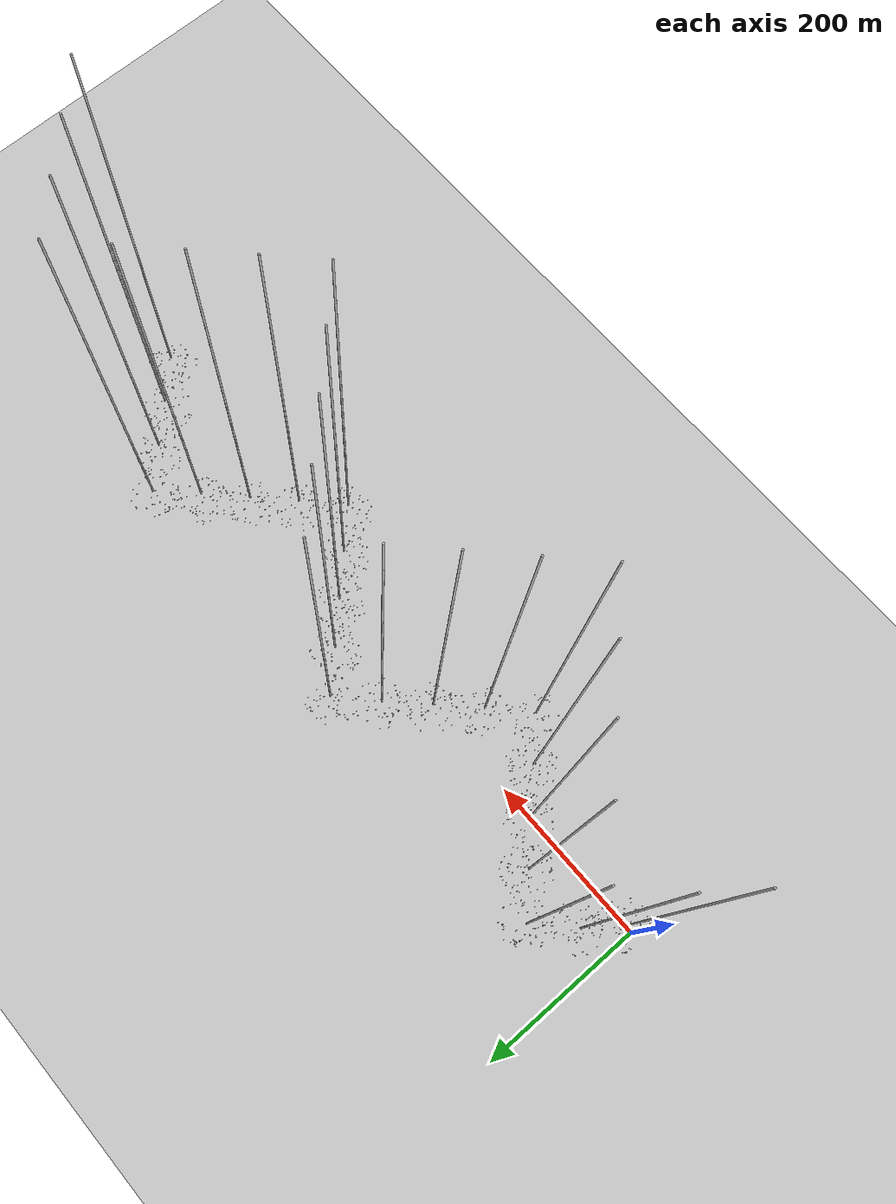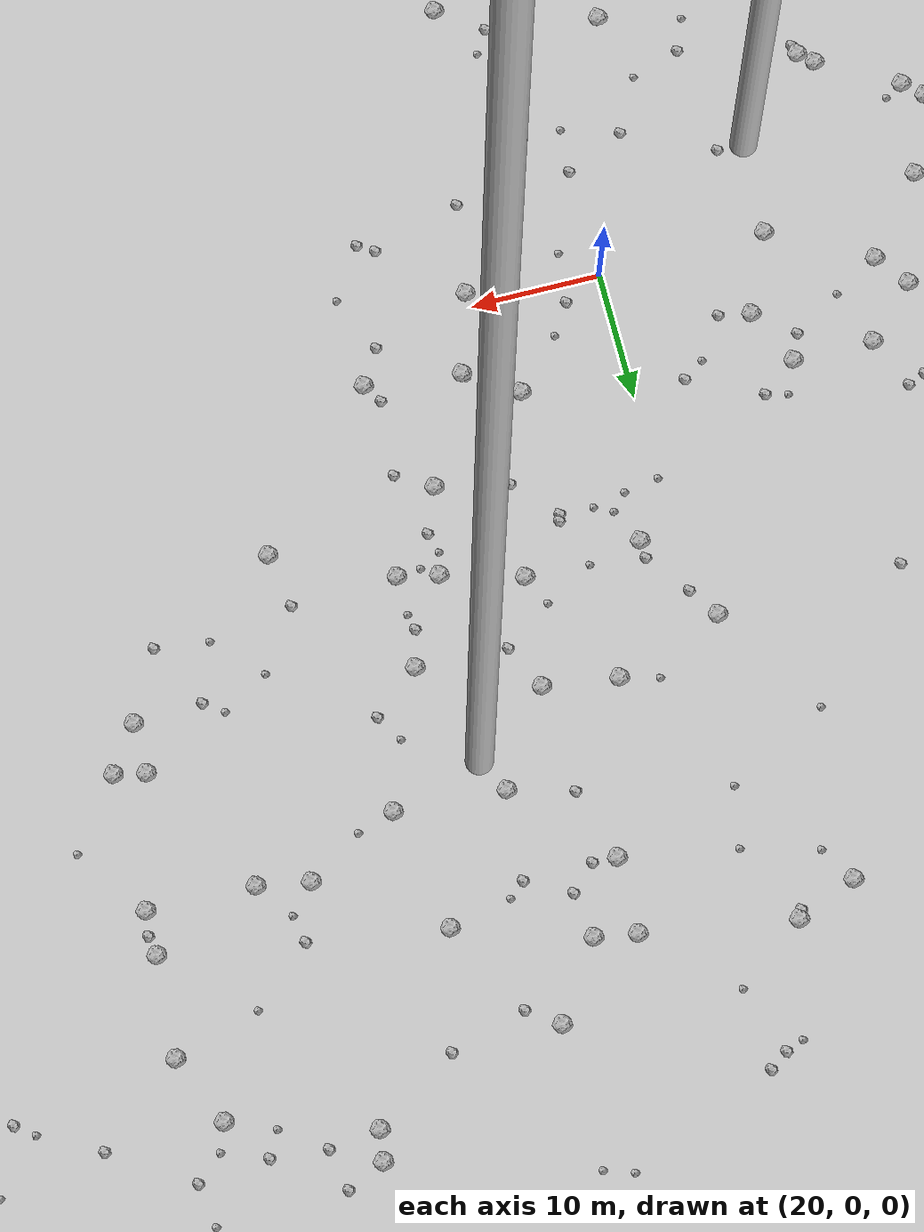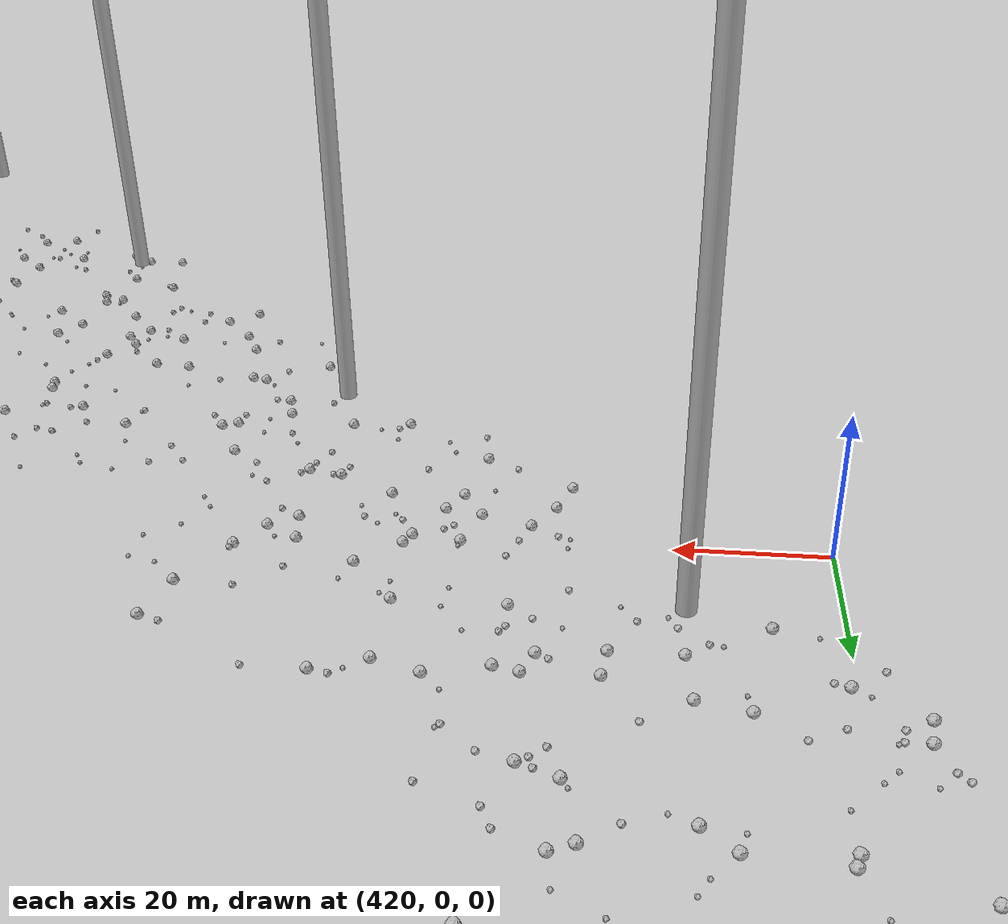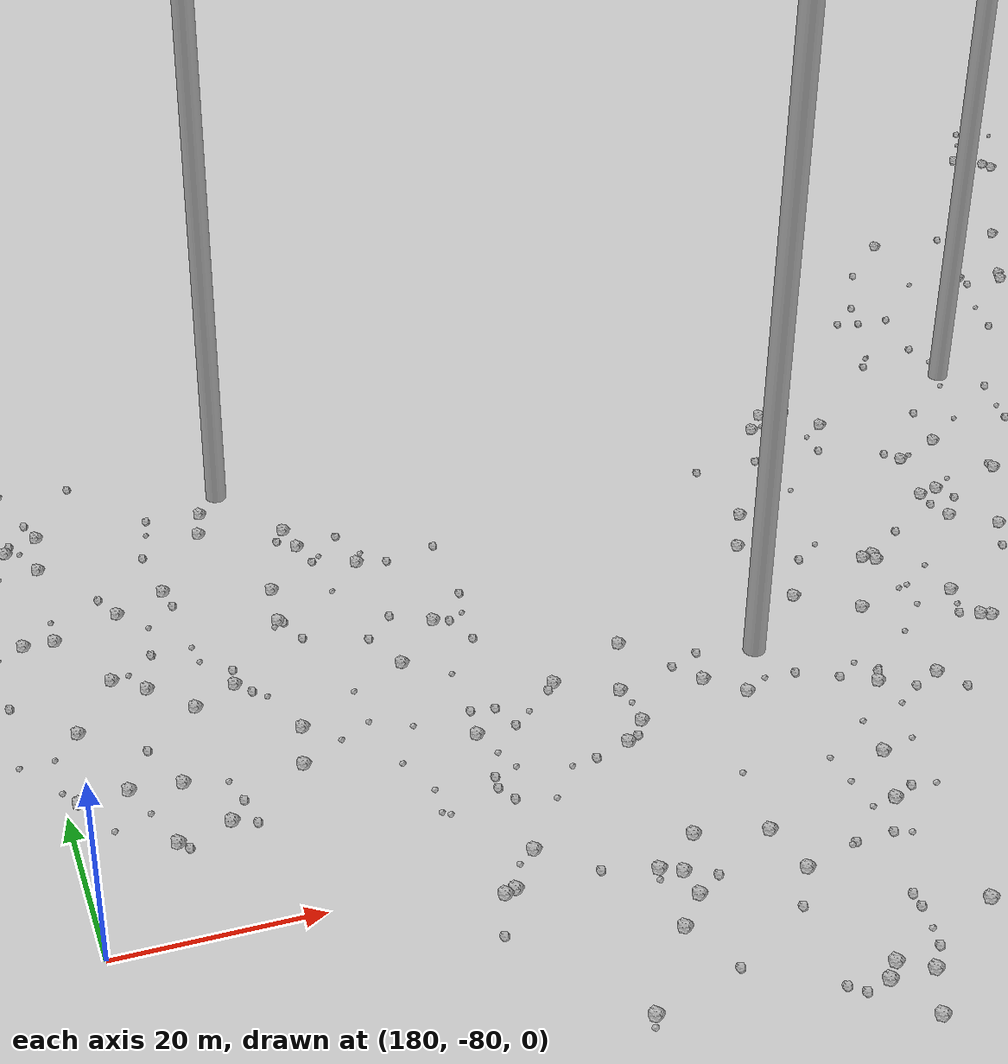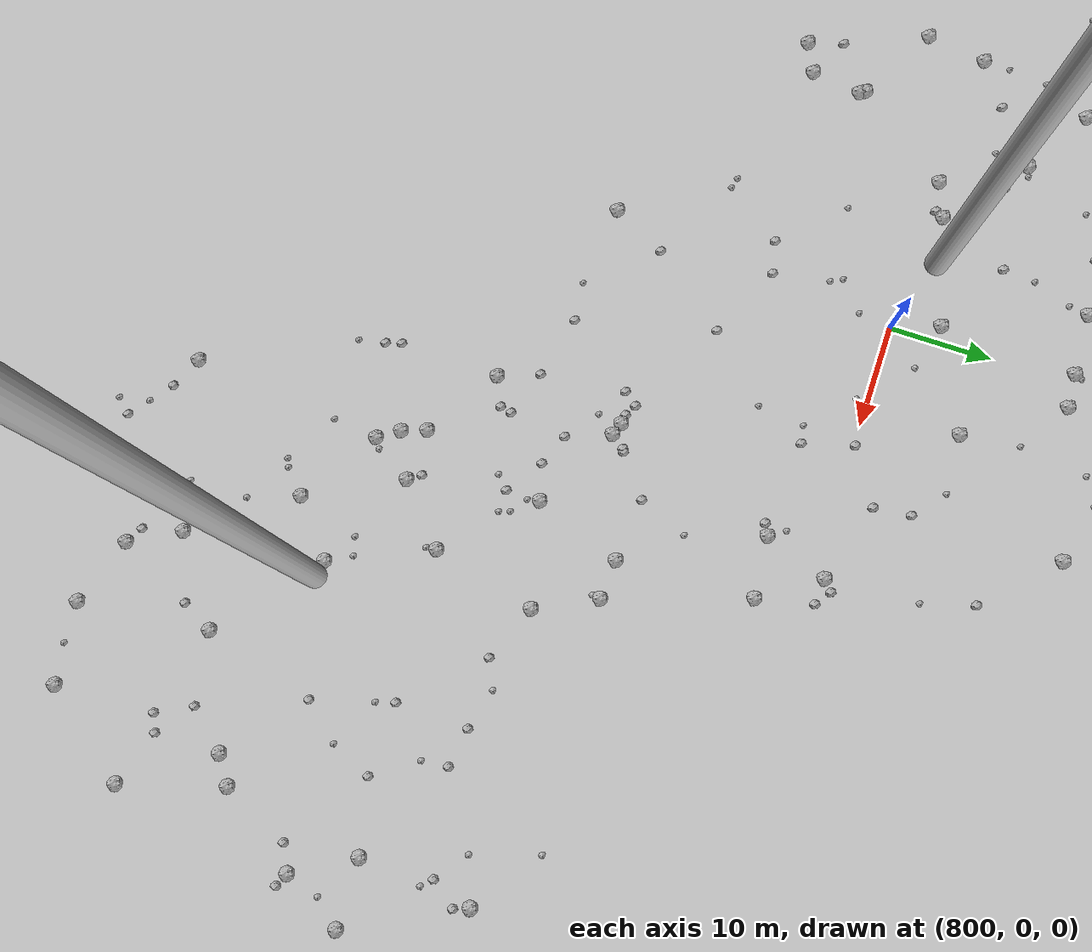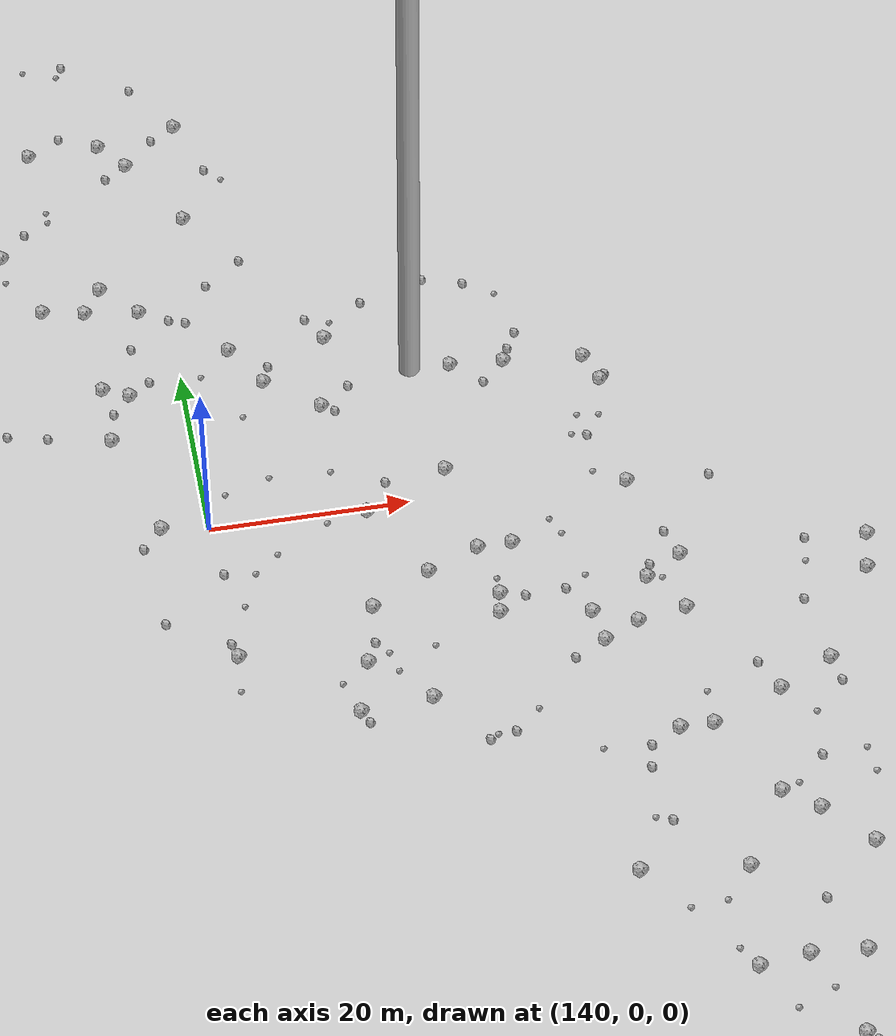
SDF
<sdf version="1.6">
 <world name="default">
  <include><uri>model://custom_ground</uri></include>
  <include><uri>model://sun</uri></include>
  <spherical_coordinates>
   <surface_model>EARTH_WGS84</surface_model>
   <latitude_deg>38.161479</latitude_deg>
   <longitude_deg>-122.454630</longitude_deg>
   <elevation>488.0</elevation>
   <heading_deg>90</heading_deg>
  </spherical_coordinates>
  <model name="rock1_0_0">
   <include><uri>model://rock1</uri><pose>-6.443277503195418 -9.487868707565788 0.5 0 0 0</pose></include>
  </model>
  <model name="rock1_0_1">
   <include><uri>model://rock1</uri><pose>22.550187904807615 21.19036130373661 0.5 0 0 0</pose></include>
  </model>
  <model name="rock1_0_2">
   <include><uri>model://rock1</uri><pose>7.0305556059217835 -0.28750387324463844 0.5 0 0 0</pose></include>
  </model>
  <model name="rock1_0_3">
   <include><uri>model://rock1</uri><pose>7.641760754076454 10.216692038546014 0.5 0 0 0</pose></include>
  </model>
  <model name="rock1_0_4">
   <include><uri>model://rock1</uri><pose>30.23309122094161 -1.0826560397617229 0.5 0 0 0</pose></include>
  </model>
  <model name="rock1_0_5">
   <include><uri>model://rock1</uri><pose>-1.7187637144472774 -22.406144028406178 0.5 0 0 0</pose></include>
  </model>
  <model name="rock1_0_6">
   <include><uri>model://rock1</uri><pose>1.4079951477513895 10.235617145945696 0.5 0 0 0</pose></include>
  </model>
  <model name="rock1_0_7">
   <include><uri>model://rock1</uri><pose>-8.902995518602284 20.622236321182733 0.5 0 0 0</pose></include>
  </model>
  <model name="rock1_0_8">
   <include><uri>model://rock1</uri><pose>39.508549570712496 4.245681624743078 0.5 0 0 0</pose></include>
  </model>
  <model name="rock1_0_9">
   <include><uri>model://rock1</uri><pose>-5.3894212409241256 -2.116709362998673 0.5 0 0 0</pose></include>
  </model>
  <model name="rock1_0_10">
   <include><uri>model://rock1</uri><pose>0.6335205582660848 -13.85178328141134 0.5 0 0 0</pose></include>
  </model>
  <model name="rock1_0_11">
   <include><uri>model://rock1</uri><pose>-7.8994113767563405 -8.149558475429263 0.5 0 0 0</pose></include>
  </model>
  <model name="rock1_0_12">
   <include><uri>model://rock1</uri><pose>-4.181651870606091 11.913827634127998 0.5 0 0 0</pose></include>
  </model>
  <model name="rock1_0_13">
   <include><uri>model://rock1</uri><pose>-11.219704810035068 -17.939012809515518 0.5 0 0 0</pose></include>
  </model>
  <model name="rock1_0_14">
   <include><uri>model://rock1</uri><pose>-12.384349242800045 -13.789519842083834 0.5 0 0 0</pose></include>
  </model>
  <model name="rock1_0_15">
   <include><uri>model://rock1</uri><pose>23.21728155504649 -12.295263806051281 0.5 0 0 0</pose></include>
  </model>
  <model name="rock1_0_16">
   <include><uri>model://rock1</uri><pose>1.4245927293472356 -25.220313886482394 0.5 0 0 0</pose></include>
  </model>
  <model name="rock1_0_17">
   <include><uri>model://rock1</uri><pose>28.144983278134205 7.646546889041026 0.5 0 0 0</pose></include>
  </model>
  <model name="rock1_0_18">
   <include><uri>model://rock1</uri><pose>32.11437152186351 5.10086176141121 0.5 0 0 0</pose></include>
  </model>
  <model name="rock1_0_19">
   <include><uri>model://rock1</uri><pose>14.702481053617383 -20.540502805543724 0.5 0 0 0</pose></include>
  </model>
  <model name="rock1_0_20">
   <include><uri>model://rock1</uri><pose>18.458557971878285 28.14566371858286 0.5 0 0 0</pose></include>
  </model>
  <model name="rock1_0_21">
   <include><uri>model://rock1</uri><pose>26.76821164574025 -24.200863007803893 0.5 0 0 0</pose></include>
  </model>
  <model name="rock1_0_22">
   <include><uri>model://rock1</uri><pose>-10.872672660922223 17.65755850956768 0.5 0 0 0</pose></include>
  </model>
  <model name="rock1_0_23">
   <include><uri>model://rock1</uri><pose>9.725443613026663 5.827948389595555 0.5 0 0 0</pose></include>
  </model>
  <model name="rock1_0_24">
   <include><uri>model://rock1</uri><pose>-0.5668998233712621 3.793885789892016 0.5 0 0 0</pose></include>
  </model>
  <model name="rock1_0_25">
   <include><uri>model://rock1</uri><pose>-0.47103784757431555 -12.868228384196051 0.5 0 0 0</pose></include>
  </model>
  <model name="rock1_0_26">
   <include><uri>model://rock1</uri><pose>-2.460116495946018 6.343293231969525 0.5 0 0 0</pose></include>
  </model>
  <model name="rock2_0_0">
   <include><uri>model://rock2</uri><pose>12.850765968298496 -28.47531916898552 0.3 0 0 0</pose></include>
  </model>
  <model name="rock2_0_1">
   <include><uri>model://rock2</uri><pose>36.019471530731906 -6.098207384405498 0.3 0 0 0</pose></include>
  </model>
  <model name="rock2_0_2">
   <include><uri>model://rock2</uri><pose>27.797516410862315 17.69431097387575 0.3 0 0 0</pose></include>
  </model>
  <model name="rock2_0_3">
   <include><uri>model://rock2</uri><pose>29.090618905798145 -8.232707097950318 0.3 0 0 0</pose></include>
  </model>
  <model name="rock2_0_4">
   <include><uri>model://rock2</uri><pose>38.546825873859945 5.725180578138122 0.3 0 0 0</pose></include>
  </model>
  <model name="rock2_0_5">
   <include><uri>model://rock2</uri><pose>-5.555884834743875 -22.12730717349487 0.3 0 0 0</pose></include>
  </model>
  <model name="rock2_0_6">
   <include><uri>model://rock2</uri><pose>20.07562160194979 -8.753678265193251 0.3 0 0 0</pose></include>
  </model>
  <model name="rock2_0_7">
   <include><uri>model://rock2</uri><pose>-0.2885765354832657 14.222355390068074 0.3 0 0 0</pose></include>
  </model>
  <model name="rock2_0_8">
   <include><uri>model://rock2</uri><pose>23.013899254310246 1.4826230786989605 0.3 0 0 0</pose></include>
  </model>
  <model name="rock2_0_9">
   <include><uri>model://rock2</uri><pose>8.660892484651097 -7.688255160640075 0.3 0 0 0</pose></include>
  </model>
  <model name="rock2_0_10">
   <include><uri>model://rock2</uri><pose>20.010362096543105 25.84250545110538 0.3 0 0 0</pose></include>
  </model>
  <model name="rock2_0_11">
   <include><uri>model://rock2</uri><pose>6.742515614180572 8.206277493050955 0.3 0 0 0</pose></include>
  </model>
  <model name="rock2_0_12">
   <include><uri>model://rock2</uri><pose>-12.402292016353588 -10.015560882795626 0.3 0 0 0</pose></include>
  </model>
  <model name="rock2_0_13">
   <include><uri>model://rock2</uri><pose>15.499037753693862 -10.883290655876127 0.3 0 0 0</pose></include>
  </model>
  <model name="rock2_0_14">
   <include><uri>model://rock2</uri><pose>0.8484165443850387 -14.65119680552032 0.3 0 0 0</pose></include>
  </model>
  <model name="rock2_0_15">
   <include><uri>model://rock2</uri><pose>9.478109685024307 -16.402811645770917 0.3 0 0 0</pose></include>
  </model>
  <model name="rock2_0_16">
   <include><uri>model://rock2</uri><pose>15.945537602363324 9.680524663623594 0.3 0 0 0</pose></include>
  </model>
  <model name="rock2_0_17">
   <include><uri>model://rock2</uri><pose>-10.05558108195006 -2.000290715890401 0.3 0 0 0</pose></include>
  </model>
  <model name="rock2_0_18">
   <include><uri>model://rock2</uri><pose>37.871622505409 1.5159388665059659 0.3 0 0 0</pose></include>
  </model>
  <model name="rock2_0_19">
   <include><uri>model://rock2</uri><pose>37.27661108081888 -6.8762030812899795 0.3 0 0 0</pose></include>
  </model>
  <model name="rock2_0_20">
   <include><uri>model://rock2</uri><pose>4.205166372611092 27.681394453289975 0.3 0 0 0</pose></include>
  </model>
  <model name="rock2_0_21">
   <include><uri>model://rock2</uri><pose>23.340825852807967 -21.76499551146255 0.3 0 0 0</pose></include>
  </model>
  <model name="rock2_0_22">
   <include><uri>model://rock2</uri><pose>-9.626479283306393 5.345593081837386 0.3 0 0 0</pose></include>
  </model>
  <model name="rock2_0_23">
   <include><uri>model://rock2</uri><pose>12.149545712732397 5.337969914483672 0.3 0 0 0</pose></include>
  </model>
  <model name="rock2_0_24">
   <include><uri>model://rock2</uri><pose>-1.6834291898651657 13.677952729172326 0.3 0 0 0</pose></include>
  </model>
  <model name="rock2_0_25">
   <include><uri>model://rock2</uri><pose>10.394149280413814 12.31699958827739 0.3 0 0 0</pose></include>
  </model>
  <model name="rock2_0_26">
   <include><uri>model://rock2</uri><pose>-11.444681618949613 11.731973524209991 0.3 0 0 0</pose></include>
  </model>
  <model name="rock3_0_0">
   <include><uri>model://rock3</uri><pose>22.637279911559055 17.171624182176416 0.2 0 0 0</pose></include>
  </model>
  <model name="rock3_0_1">
   <include><uri>model://rock3</uri><pose>24.419964978249794 -19.994066264125824 0.2 0 0 0</pose></include>
  </model>
  <model name="rock3_0_2">
   <include><uri>model://rock3</uri><pose>39.802760895843605 -2.9502760905795284 0.2 0 0 0</pose></include>
  </model>
  <model name="rock3_0_3">
   <include><uri>model://rock3</uri><pose>19.93134404280076 16.71175268600983 0.2 0 0 0</pose></include>
  </model>
  <model name="rock3_0_4">
   <include><uri>model://rock3</uri><pose>8.679637963878765 12.67915462452084 0.2 0 0 0</pose></include>
  </model>
  <model name="rock3_0_5">
   <include><uri>model://rock3</uri><pose>19.822918613462882 -12.301830412854965 0.2 0 0 0</pose></include>
  </model>
  <model name="rock3_0_6">
   <include><uri>model://rock3</uri><pose>-1.7209431648797313 -24.63777488053548 0.2 0 0 0</pose></include>
  </model>
  <model name="rock3_0_7">
   <include><uri>model://rock3</uri><pose>7.523991675669556 -27.53825745464444 0.2 0 0 0</pose></include>
  </model>
  <model name="rock3_0_8">
   <include><uri>model://rock3</uri><pose>2.944192489777869 5.833461908083244 0.2 0 0 0</pose></include>
  </model>
  <model name="rock3_0_9">
   <include><uri>model://rock3</uri><pose>24.520313718330023 3.8161886966223477 0.2 0 0 0</pose></include>
  </model>
  <model name="rock3_0_10">
   <include><uri>model://rock3</uri><pose>2.9753437813506665 -14.791211545339255 0.2 0 0 0</pose></include>
  </model>
  <model name="rock3_0_11">
   <include><uri>model://rock3</uri><pose>22.54720699541918 -2.5469912875213225 0.2 0 0 0</pose></include>
  </model>
  <model name="rock3_0_12">
   <include><uri>model://rock3</uri><pose>-18.396804983045538 5.573619653966745 0.2 0 0 0</pose></include>
  </model>
  <model name="rock3_0_13">
   <include><uri>model://rock3</uri><pose>14.27345908949966 8.491422006728605 0.2 0 0 0</pose></include>
  </model>
  <model name="rock3_0_14">
   <include><uri>model://rock3</uri><pose>-6.074974225690948 9.66834795697308 0.2 0 0 0</pose></include>
  </model>
  <model name="rock3_0_15">
   <include><uri>model://rock3</uri><pose>18.031624054003444 -23.764442685646348 0.2 0 0 0</pose></include>
  </model>
  <model name="rock3_0_16">
   <include><uri>model://rock3</uri><pose>-5.091605681558937 -8.726473459033045 0.2 0 0 0</pose></include>
  </model>
  <model name="rock3_0_17">
   <include><uri>model://rock3</uri><pose>-1.6592954916048868 -24.893690758808724 0.2 0 0 0</pose></include>
  </model>
  <model name="rock3_0_18">
   <include><uri>model://rock3</uri><pose>-10.29303190754423 19.142307689838688 0.2 0 0 0</pose></include>
  </model>
  <model name="rock3_0_19">
   <include><uri>model://rock3</uri><pose>23.805341589944398 18.44200240753925 0.2 0 0 0</pose></include>
  </model>
  <model name="rock3_0_20">
   <include><uri>model://rock3</uri><pose>13.260662389347864 -15.16646245243862 0.2 0 0 0</pose></include>
  </model>
  <model name="rock3_0_21">
   <include><uri>model://rock3</uri><pose>31.815592760152725 5.442773582142543 0.2 0 0 0</pose></include>
  </model>
  <model name="rock3_0_22">
   <include><uri>model://rock3</uri><pose>-9.202770411464748 -3.756250696555796 0.2 0 0 0</pose></include>
  </model>
  <model name="rock3_0_23">
   <include><uri>model://rock3</uri><pose>-2.7578508969093 22.766330357936866 0.2 0 0 0</pose></include>
  </model>
  <model name="rock3_0_24">
   <include><uri>model://rock3</uri><pose>-9.015934676668394 -21.09859477019648 0.2 0 0 0</pose></include>
  </model>
  <model name="rock3_0_25">
   <include><uri>model://rock3</uri><pose>8.417057467533692 -19.003588496054174 0.2 0 0 0</pose></include>
  </model>
  <model name="rock3_0_26">
   <include><uri>model://rock3</uri><pose>-10.078208189231008 12.155887606262041 0.2 0 0 0</pose></include>
  </model>
  <model name="rock1_1_0">
   <include><uri>model://rock1</uri><pose>64.73573824903482 43.13351638466799 0.5 0 0 0</pose></include>
  </model>
  <model name="rock1_1_1">
   <include><uri>model://rock1</uri><pose>33.67689557969526 49.62703487198102 0.5 0 0 0</pose></include>
  </model>
  <model name="rock1_1_2">
   <include><uri>model://rock1</uri><pose>32.51509132858183 30.326442858993744 0.5 0 0 0</pose></include>
  </model>
  <model name="rock1_1_3">
   <include><uri>model://rock1</uri><pose>65.18205801264816 50.89249709298497 0.5 0 0 0</pose></include>
  </model>
  <model name="rock1_1_4">
   <include><uri>model://rock1</uri><pose>64.72988211308201 39.714827741971874 0.5 0 0 0</pose></include>
  </model>
  <model name="rock1_1_5">
   <include><uri>model://rock1</uri><pose>52.551100558165 40.55000497652986 0.5 0 0 0</pose></include>
  </model>
  <model name="rock1_1_6">
   <include><uri>model://rock1</uri><pose>52.17077331229769 59.522711530371815 0.5 0 0 0</pose></include>
  </model>
  <model name="rock1_1_7">
   <include><uri>model://rock1</uri><pose>62.308020924563905 29.618445738978856 0.5 0 0 0</pose></include>
  </model>
  <model name="rock1_1_8">
   <include><uri>model://rock1</uri><pose>52.50802168211569 61.86181428242751 0.5 0 0 0</pose></include>
  </model>
  <model name="rock1_1_9">
   <include><uri>model://rock1</uri><pose>62.33317389496431 25.697672202371784 0.5 0 0 0</pose></include>
  </model>
  <model name="rock1_1_10">
   <include><uri>model://rock1</uri><pose>18.857810855954778 52.00415543073883 0.5 0 0 0</pose></include>
  </model>
  <model name="rock1_1_11">
   <include><uri>model://rock1</uri><pose>64.6772020639103 29.123287962937113 0.5 0 0 0</pose></include>
  </model>
  <model name="rock1_1_12">
   <include><uri>model://rock1</uri><pose>45.46558605036403 36.90769088375977 0.5 0 0 0</pose></include>
  </model>
  <model name="rock1_1_13">
   <include><uri>model://rock1</uri><pose>31.563628002844837 21.834851383854307 0.5 0 0 0</pose></include>
  </model>
  <model name="rock1_1_14">
   <include><uri>model://rock1</uri><pose>49.65823747622627 15.495211668657277 0.5 0 0 0</pose></include>
  </model>
  <model name="rock1_1_15">
   <include><uri>model://rock1</uri><pose>56.54623419302632 39.865325005400585 0.5 0 0 0</pose></include>
  </model>
  <model name="rock1_1_16">
   <include><uri>model://rock1</uri><pose>37.70649132016676 20.108627413010574 0.5 0 0 0</pose></include>
  </model>
  <model name="rock1_1_17">
   <include><uri>model://rock1</uri><pose>30.489583619727608 50.15334769346879 0.5 0 0 0</pose></include>
  </model>
  <model name="rock1_1_18">
   <include><uri>model://rock1</uri><pose>30.48029205590381 44.27665378894992 0.5 0 0 0</pose></include>
  </model>
  <model name="rock1_1_19">
   <include><uri>model://rock1</uri><pose>26.788067862120545 31.089161458673075 0.5 0 0 0</pose></include>
  </model>
  <model name="rock1_1_20">
   <include><uri>model://rock1</uri><pose>37.54077928108545 55.31028130583227 0.5 0 0 0</pose></include>
  </model>
  <model name="rock1_1_21">
   <include><uri>model://rock1</uri><pose>41.202974040507456 26.61704789420908 0.5 0 0 0</pose></include>
  </model>
  <model name="rock1_1_22">
   <include><uri>model://rock1</uri><pose>37.010430510706485 37.35415060404381 0.5 0 0 0</pose></include>
  </model>
  <model name="rock1_1_23">
   <include><uri>model://rock1</uri><pose>40.79279124148567 19.459184008736926 0.5 0 0 0</pose></include>
  </model>
  <model name="rock1_1_24">
   <include><uri>model://rock1</uri><pose>43.605096708914 46.402379779296766 0.5 0 0 0</pose></include>
  </model>
  <model name="rock1_1_25">
   <include><uri>model://rock1</uri><pose>36.34395378996767 13.323375226434457 0.5 0 0 0</pose></include>
  </model>
  <model name="rock1_1_26">
   <include><uri>model://rock1</uri><pose>14.22001544207005 50.08356431883896 0.5 0 0 0</pose></include>
  </model>
  <model name="rock2_1_0">
   <include><uri>model://rock2</uri><pose>27.964714160210296 18.199683744463858 0.3 0 0 0</pose></include>
  </model>
  <model name="rock2_1_1">
   <include><uri>model://rock2</uri><pose>34.070993432521675 21.464223042115687 0.3 0 0 0</pose></include>
  </model>
  <model name="rock2_1_2">
   <include><uri>model://rock2</uri><pose>56.052217326754615 60.024974031445325 0.3 0 0 0</pose></include>
  </model>
  <model name="rock2_1_3">
   <include><uri>model://rock2</uri><pose>22.354408722506744 61.21171138915895 0.3 0 0 0</pose></include>
  </model>
  <model name="rock2_1_4">
   <include><uri>model://rock2</uri><pose>39.0559860054352 11.68364525151993 0.3 0 0 0</pose></include>
  </model>
  <model name="rock2_1_5">
   <include><uri>model://rock2</uri><pose>40.46458870858183 23.74223154763274 0.3 0 0 0</pose></include>
  </model>
  <model name="rock2_1_6">
   <include><uri>model://rock2</uri><pose>32.1180657749301 38.68756313687556 0.3 0 0 0</pose></include>
  </model>
  <model name="rock2_1_7">
   <include><uri>model://rock2</uri><pose>34.23111020143398 46.07790258548226 0.3 0 0 0</pose></include>
  </model>
  <model name="rock2_1_8">
   <include><uri>model://rock2</uri><pose>30.77923787251389 14.476533303426166 0.3 0 0 0</pose></include>
  </model>
  <model name="rock2_1_9">
   <include><uri>model://rock2</uri><pose>37.72731551727975 16.753565273205073 0.3 0 0 0</pose></include>
  </model>
  <model name="rock2_1_10">
   <include><uri>model://rock2</uri><pose>33.20854270450846 15.811529787268249 0.3 0 0 0</pose></include>
  </model>
  <model name="rock2_1_11">
   <include><uri>model://rock2</uri><pose>34.15936608583975 26.87773265462387 0.3 0 0 0</pose></include>
  </model>
  <model name="rock2_1_12">
   <include><uri>model://rock2</uri><pose>45.76489283921471 55.36511972996325 0.3 0 0 0</pose></include>
  </model>
  <model name="rock2_1_13">
   <include><uri>model://rock2</uri><pose>32.32415011362406 44.19209148952045 0.3 0 0 0</pose></include>
  </model>
  <model name="rock2_1_14">
   <include><uri>model://rock2</uri><pose>48.93085133129753 19.729994089733232 0.3 0 0 0</pose></include>
  </model>
  <model name="rock2_1_15">
   <include><uri>model://rock2</uri><pose>57.084143713885254 25.405031886736854 0.3 0 0 0</pose></include>
  </model>
  <model name="rock2_1_16">
   <include><uri>model://rock2</uri><pose>59.58226378825983 20.42594986776081 0.3 0 0 0</pose></include>
  </model>
  <model name="rock2_1_17">
   <include><uri>model://rock2</uri><pose>39.89605880841738 53.62797700199136 0.3 0 0 0</pose></include>
  </model>
  <model name="rock2_1_18">
   <include><uri>model://rock2</uri><pose>18.493445906327846 51.35454688200562 0.3 0 0 0</pose></include>
  </model>
  <model name="rock2_1_19">
   <include><uri>model://rock2</uri><pose>44.819277912736496 29.644016388051178 0.3 0 0 0</pose></include>
  </model>
  <model name="rock2_1_20">
   <include><uri>model://rock2</uri><pose>60.35206161601706 59.63478224546994 0.3 0 0 0</pose></include>
  </model>
  <model name="rock2_1_21">
   <include><uri>model://rock2</uri><pose>37.57720644655085 44.280939282476034 0.3 0 0 0</pose></include>
  </model>
  <model name="rock2_1_22">
   <include><uri>model://rock2</uri><pose>23.774471481934203 62.237485984921605 0.3 0 0 0</pose></include>
  </model>
  <model name="rock2_1_23">
   <include><uri>model://rock2</uri><pose>64.99424680819415 41.58012145422283 0.3 0 0 0</pose></include>
  </model>
  <model name="rock2_1_24">
   <include><uri>model://rock2</uri><pose>22.479005924427767 22.583530830993094 0.3 0 0 0</pose></include>
  </model>
  <model name="rock2_1_25">
   <include><uri>model://rock2</uri><pose>54.02961439852963 44.82536599721584 0.3 0 0 0</pose></include>
  </model>
  <model name="rock2_1_26">
   <include><uri>model://rock2</uri><pose>49.28098792831314 65.50078219099794 0.3 0 0 0</pose></include>
  </model>
  <model name="rock3_1_0">
   <include><uri>model://rock3</uri><pose>20.712383873139515 41.093781872755464 0.2 0 0 0</pose></include>
  </model>
  <model name="rock3_1_1">
   <include><uri>model://rock3</uri><pose>55.41350034961863 20.87503315640007 0.2 0 0 0</pose></include>
  </model>
  <model name="rock3_1_2">
   <include><uri>model://rock3</uri><pose>25.183668652010713 17.756185361716895 0.2 0 0 0</pose></include>
  </model>
  <model name="rock3_1_3">
   <include><uri>model://rock3</uri><pose>48.31073140379499 37.7835613067533 0.2 0 0 0</pose></include>
  </model>
  <model name="rock3_1_4">
   <include><uri>model://rock3</uri><pose>37.24650140418841 18.314103456771612 0.2 0 0 0</pose></include>
  </model>
  <model name="rock3_1_5">
   <include><uri>model://rock3</uri><pose>54.43186799878031 42.6509750130025 0.2 0 0 0</pose></include>
  </model>
  <model name="rock3_1_6">
   <include><uri>model://rock3</uri><pose>26.610752770035383 22.02929280260692 0.2 0 0 0</pose></include>
  </model>
  <model name="rock3_1_7">
   <include><uri>model://rock3</uri><pose>20.940352106256885 60.63643860738023 0.2 0 0 0</pose></include>
  </model>
  <model name="rock3_1_8">
   <include><uri>model://rock3</uri><pose>38.897642924081964 19.225488779120973 0.2 0 0 0</pose></include>
  </model>
  <model name="rock3_1_9">
   <include><uri>model://rock3</uri><pose>12.918792557234353 36.86473020810401 0.2 0 0 0</pose></include>
  </model>
  <model name="rock3_1_10">
   <include><uri>model://rock3</uri><pose>23.810054407311608 31.7828843764144 0.2 0 0 0</pose></include>
  </model>
  <model name="rock3_1_11">
   <include><uri>model://rock3</uri><pose>30.40269660593183 24.16604810569775 0.2 0 0 0</pose></include>
  </model>
  <model name="rock3_1_12">
   <include><uri>model://rock3</uri><pose>52.00693327616504 24.314921109268788 0.2 0 0 0</pose></include>
  </model>
  <model name="rock3_1_13">
   <include><uri>model://rock3</uri><pose>55.57095988409736 26.425749756760368 0.2 0 0 0</pose></include>
  </model>
  <model name="rock3_1_14">
   <include><uri>model://rock3</uri><pose>32.63832632658568 15.374753358094642 0.2 0 0 0</pose></include>
  </model>
  <model name="rock3_1_15">
   <include><uri>model://rock3</uri><pose>21.59904163988182 45.78429820543355 0.2 0 0 0</pose></include>
  </model>
  <model name="rock3_1_16">
   <include><uri>model://rock3</uri><pose>38.75844734284729 45.29795919869077 0.2 0 0 0</pose></include>
  </model>
  <model name="rock3_1_17">
   <include><uri>model://rock3</uri><pose>37.39165146156025 66.30005115647414 0.2 0 0 0</pose></include>
  </model>
  <model name="rock3_1_18">
   <include><uri>model://rock3</uri><pose>59.2646127379621 57.65544875431053 0.2 0 0 0</pose></include>
  </model>
  <model name="rock3_1_19">
   <include><uri>model://rock3</uri><pose>58.5498708486203 48.85591236873781 0.2 0 0 0</pose></include>
  </model>
  <model name="rock3_1_20">
   <include><uri>model://rock3</uri><pose>15.830666898578418 47.332110458055645 0.2 0 0 0</pose></include>
  </model>
  <model name="rock3_1_21">
   <include><uri>model://rock3</uri><pose>35.20345137904924 67.02827543197535 0.2 0 0 0</pose></include>
  </model>
  <model name="rock3_1_22">
   <include><uri>model://rock3</uri><pose>68.57309194610482 34.27985795526297 0.2 0 0 0</pose></include>
  </model>
  <model name="rock3_1_23">
   <include><uri>model://rock3</uri><pose>43.5556479413423 31.646866026340188 0.2 0 0 0</pose></include>
  </model>
  <model name="rock3_1_24">
   <include><uri>model://rock3</uri><pose>40.707930729028384 22.45792760149599 0.2 0 0 0</pose></include>
  </model>
  <model name="rock3_1_25">
   <include><uri>model://rock3</uri><pose>50.168010989938885 65.65741221129217 0.2 0 0 0</pose></include>
  </model>
  <model name="rock3_1_26">
   <include><uri>model://rock3</uri><pose>24.14123644434359 55.95629329981971 0.2 0 0 0</pose></include>
  </model>
  <model name="rock1_2_0">
   <include><uri>model://rock1</uri><pose>72.94502753944855 99.39867292059635 0.5 0 0 0</pose></include>
  </model>
  <model name="rock1_2_1">
   <include><uri>model://rock1</uri><pose>51.98530772410967 81.53210213371682 0.5 0 0 0</pose></include>
  </model>
  <model name="rock1_2_2">
   <include><uri>model://rock1</uri><pose>94.9307187964134 97.9735915181665 0.5 0 0 0</pose></include>
  </model>
  <model name="rock1_2_3">
   <include><uri>model://rock1</uri><pose>62.885657006788925 56.248278275974656 0.5 0 0 0</pose></include>
  </model>
  <model name="rock1_2_4">
   <include><uri>model://rock1</uri><pose>90.4689351509362 100.51646021220789 0.5 0 0 0</pose></include>
  </model>
  <model name="rock1_2_5">
   <include><uri>model://rock1</uri><pose>66.32116298267032 65.74488176195916 0.5 0 0 0</pose></include>
  </model>
  <model name="rock1_2_6">
   <include><uri>model://rock1</uri><pose>81.6403782113806 52.64229748880926 0.5 0 0 0</pose></include>
  </model>
  <model name="rock1_2_7">
   <include><uri>model://rock1</uri><pose>102.21413142275733 72.3383843887578 0.5 0 0 0</pose></include>
  </model>
  <model name="rock1_2_8">
   <include><uri>model://rock1</uri><pose>67.81061125819058 70.89123132577511 0.5 0 0 0</pose></include>
  </model>
  <model name="rock1_2_9">
   <include><uri>model://rock1</uri><pose>62.117236779135226 87.72042687643474 0.5 0 0 0</pose></include>
  </model>
  <model name="rock1_2_10">
   <include><uri>model://rock1</uri><pose>63.788950436217405 78.39010102145284 0.5 0 0 0</pose></include>
  </model>
  <model name="rock1_2_11">
   <include><uri>model://rock1</uri><pose>95.52078918800544 67.76377320352576 0.5 0 0 0</pose></include>
  </model>
  <model name="rock1_2_12">
   <include><uri>model://rock1</uri><pose>67.86683316086818 82.89352266087357 0.5 0 0 0</pose></include>
  </model>
  <model name="rock1_2_13">
   <include><uri>model://rock1</uri><pose>77.36670029611392 68.21008054933749 0.5 0 0 0</pose></include>
  </model>
  <model name="rock1_2_14">
   <include><uri>model://rock1</uri><pose>61.73364029720016 88.07578880119621 0.5 0 0 0</pose></include>
  </model>
  <model name="rock1_2_15">
   <include><uri>model://rock1</uri><pose>90.92992183172723 54.87548898935135 0.5 0 0 0</pose></include>
  </model>
  <model name="rock1_2_16">
   <include><uri>model://rock1</uri><pose>62.39946396019616 79.42799716252625 0.5 0 0 0</pose></include>
  </model>
  <model name="rock1_2_17">
   <include><uri>model://rock1</uri><pose>54.23977564250593 77.92002625189475 0.5 0 0 0</pose></include>
  </model>
  <model name="rock1_2_18">
   <include><uri>model://rock1</uri><pose>87.36592699467259 68.98604471235647 0.5 0 0 0</pose></include>
  </model>
  <model name="rock1_2_19">
   <include><uri>model://rock1</uri><pose>71.47523778697516 101.67412627789332 0.5 0 0 0</pose></include>
  </model>
  <model name="rock1_2_20">
   <include><uri>model://rock1</uri><pose>100.76252270509933 65.86611357484418 0.5 0 0 0</pose></include>
  </model>
  <model name="rock1_2_21">
   <include><uri>model://rock1</uri><pose>58.731353724656415 68.79499401810975 0.5 0 0 0</pose></include>
  </model>
  <model name="rock1_2_22">
   <include><uri>model://rock1</uri><pose>107.61282247826836 85.208631111321 0.5 0 0 0</pose></include>
  </model>
  <model name="rock1_2_23">
   <include><uri>model://rock1</uri><pose>99.61401200637388 100.07283039411692 0.5 0 0 0</pose></include>
  </model>
  <model name="rock1_2_24">
   <include><uri>model://rock1</uri><pose>76.44998288409836 62.95330301576143 0.5 0 0 0</pose></include>
  </model>
  <model name="rock1_2_25">
   <include><uri>model://rock1</uri><pose>70.57583000872498 95.30998544828921 0.5 0 0 0</pose></include>
  </model>
  <model name="rock1_2_26">
   <include><uri>model://rock1</uri><pose>71.96330747544846 86.72595053708474 0.5 0 0 0</pose></include>
  </model>
  <model name="rock2_2_0">
   <include><uri>model://rock2</uri><pose>86.4857279432111 59.3697813769871 0.3 0 0 0</pose></include>
  </model>
  <model name="rock2_2_1">
   <include><uri>model://rock2</uri><pose>81.00978026707577 90.47617478495705 0.3 0 0 0</pose></include>
  </model>
  <model name="rock2_2_2">
   <include><uri>model://rock2</uri><pose>71.68739425284608 56.26993913276967 0.3 0 0 0</pose></include>
  </model>
  <model name="rock2_2_3">
   <include><uri>model://rock2</uri><pose>65.7197727571316 60.15552394317053 0.3 0 0 0</pose></include>
  </model>
  <model name="rock2_2_4">
   <include><uri>model://rock2</uri><pose>77.58980629318208 52.77753975444623 0.3 0 0 0</pose></include>
  </model>
  <model name="rock2_2_5">
   <include><uri>model://rock2</uri><pose>92.52051061640549 98.31945586347649 0.3 0 0 0</pose></include>
  </model>
  <model name="rock2_2_6">
   <include><uri>model://rock2</uri><pose>59.83955870572919 87.81655363645896 0.3 0 0 0</pose></include>
  </model>
  <model name="rock2_2_7">
   <include><uri>model://rock2</uri><pose>60.62425638369616 101.50207874056855 0.3 0 0 0</pose></include>
  </model>
  <model name="rock2_2_8">
   <include><uri>model://rock2</uri><pose>97.61541515068016 66.49343872244951 0.3 0 0 0</pose></include>
  </model>
  <model name="rock2_2_9">
   <include><uri>model://rock2</uri><pose>95.54114978766754 69.12760633645726 0.3 0 0 0</pose></include>
  </model>
  <model name="rock2_2_10">
   <include><uri>model://rock2</uri><pose>69.52806128080006 74.60340480990044 0.3 0 0 0</pose></include>
  </model>
  <model name="rock2_2_11">
   <include><uri>model://rock2</uri><pose>68.89793551445095 73.99564855236008 0.3 0 0 0</pose></include>
  </model>
  <model name="rock2_2_12">
   <include><uri>model://rock2</uri><pose>70.67004171495739 76.04709933433314 0.3 0 0 0</pose></include>
  </model>
  <model name="rock2_2_13">
   <include><uri>model://rock2</uri><pose>70.82835338778517 99.59541921677854 0.3 0 0 0</pose></include>
  </model>
  <model name="rock2_2_14">
   <include><uri>model://rock2</uri><pose>80.1342190548341 61.82174590015243 0.3 0 0 0</pose></include>
  </model>
  <model name="rock2_2_15">
   <include><uri>model://rock2</uri><pose>105.03861749241854 76.98581262102249 0.3 0 0 0</pose></include>
  </model>
  <model name="rock2_2_16">
   <include><uri>model://rock2</uri><pose>62.613118707328766 91.25808762538375 0.3 0 0 0</pose></include>
  </model>
  <model name="rock2_2_17">
   <include><uri>model://rock2</uri><pose>75.6970040806184 61.96332194406575 0.3 0 0 0</pose></include>
  </model>
  <model name="rock2_2_18">
   <include><uri>model://rock2</uri><pose>68.75374955385912 64.25596154178831 0.3 0 0 0</pose></include>
  </model>
  <model name="rock2_2_19">
   <include><uri>model://rock2</uri><pose>91.93409307565962 55.757061911604 0.3 0 0 0</pose></include>
  </model>
  <model name="rock2_2_20">
   <include><uri>model://rock2</uri><pose>82.32026341452453 106.96069824100447 0.3 0 0 0</pose></include>
  </model>
  <model name="rock2_2_21">
   <include><uri>model://rock2</uri><pose>84.23804492112538 100.32924905189284 0.3 0 0 0</pose></include>
  </model>
  <model name="rock2_2_22">
   <include><uri>model://rock2</uri><pose>76.25727841986327 99.70793995419844 0.3 0 0 0</pose></include>
  </model>
  <model name="rock2_2_23">
   <include><uri>model://rock2</uri><pose>55.40777602651304 63.24725872583789 0.3 0 0 0</pose></include>
  </model>
  <model name="rock2_2_24">
   <include><uri>model://rock2</uri><pose>96.66215030519021 64.86779632767586 0.3 0 0 0</pose></include>
  </model>
  <model name="rock2_2_25">
   <include><uri>model://rock2</uri><pose>80.81740619415015 91.90825628075358 0.3 0 0 0</pose></include>
  </model>
  <model name="rock2_2_26">
   <include><uri>model://rock2</uri><pose>74.33340766292051 99.34641713041326 0.3 0 0 0</pose></include>
  </model>
  <model name="rock3_2_0">
   <include><uri>model://rock3</uri><pose>71.13027651629741 83.71216932759575 0.2 0 0 0</pose></include>
  </model>
  <model name="rock3_2_1">
   <include><uri>model://rock3</uri><pose>94.62065948614863 68.56925332870742 0.2 0 0 0</pose></include>
  </model>
  <model name="rock3_2_2">
   <include><uri>model://rock3</uri><pose>69.02915986247041 102.05217761529482 0.2 0 0 0</pose></include>
  </model>
  <model name="rock3_2_3">
   <include><uri>model://rock3</uri><pose>69.83203740845364 108.14437637706973 0.2 0 0 0</pose></include>
  </model>
  <model name="rock3_2_4">
   <include><uri>model://rock3</uri><pose>70.20214382413523 105.99625042532779 0.2 0 0 0</pose></include>
  </model>
  <model name="rock3_2_5">
   <include><uri>model://rock3</uri><pose>97.62007889653819 91.92940870524846 0.2 0 0 0</pose></include>
  </model>
  <model name="rock3_2_6">
   <include><uri>model://rock3</uri><pose>70.02680187736787 92.71284157894178 0.2 0 0 0</pose></include>
  </model>
  <model name="rock3_2_7">
   <include><uri>model://rock3</uri><pose>63.01541735938717 83.8556431597371 0.2 0 0 0</pose></include>
  </model>
  <model name="rock3_2_8">
   <include><uri>model://rock3</uri><pose>63.46488132912241 80.1003609901543 0.2 0 0 0</pose></include>
  </model>
  <model name="rock3_2_9">
   <include><uri>model://rock3</uri><pose>87.87612403106873 51.647098293283875 0.2 0 0 0</pose></include>
  </model>
  <model name="rock3_2_10">
   <include><uri>model://rock3</uri><pose>107.87475333434156 69.48094259827909 0.2 0 0 0</pose></include>
  </model>
  <model name="rock3_2_11">
   <include><uri>model://rock3</uri><pose>80.37225427359797 50.36308564535491 0.2 0 0 0</pose></include>
  </model>
  <model name="rock3_2_12">
   <include><uri>model://rock3</uri><pose>92.80594695084126 76.67147731919295 0.2 0 0 0</pose></include>
  </model>
  <model name="rock3_2_13">
   <include><uri>model://rock3</uri><pose>70.10042318641214 66.93475524031285 0.2 0 0 0</pose></include>
  </model>
  <model name="rock3_2_14">
   <include><uri>model://rock3</uri><pose>75.90369935349429 103.33583735646076 0.2 0 0 0</pose></include>
  </model>
  <model name="rock3_2_15">
   <include><uri>model://rock3</uri><pose>66.24247084314935 75.41122254472238 0.2 0 0 0</pose></include>
  </model>
  <model name="rock3_2_16">
   <include><uri>model://rock3</uri><pose>79.67141390933648 57.68122800065576 0.2 0 0 0</pose></include>
  </model>
  <model name="rock3_2_17">
   <include><uri>model://rock3</uri><pose>65.18576383542134 63.47400876968865 0.2 0 0 0</pose></include>
  </model>
  <model name="rock3_2_18">
   <include><uri>model://rock3</uri><pose>62.89543000514163 87.18767562933118 0.2 0 0 0</pose></include>
  </model>
  <model name="rock3_2_19">
   <include><uri>model://rock3</uri><pose>71.80209407169724 98.46966321597061 0.2 0 0 0</pose></include>
  </model>
  <model name="rock3_2_20">
   <include><uri>model://rock3</uri><pose>102.89646177386979 71.86683959702997 0.2 0 0 0</pose></include>
  </model>
  <model name="rock3_2_21">
   <include><uri>model://rock3</uri><pose>97.84857913153921 93.9172650755545 0.2 0 0 0</pose></include>
  </model>
  <model name="rock3_2_22">
   <include><uri>model://rock3</uri><pose>76.15674166681904 53.82049897645594 0.2 0 0 0</pose></include>
  </model>
  <model name="rock3_2_23">
   <include><uri>model://rock3</uri><pose>71.0341157524574 98.28022432507422 0.2 0 0 0</pose></include>
  </model>
  <model name="rock3_2_24">
   <include><uri>model://rock3</uri><pose>109.3183887377916 84.50671120072761 0.2 0 0 0</pose></include>
  </model>
  <model name="rock3_2_25">
   <include><uri>model://rock3</uri><pose>63.65246129734054 58.309500430740464 0.2 0 0 0</pose></include>
  </model>
  <model name="rock3_2_26">
   <include><uri>model://rock3</uri><pose>89.73089992373102 76.71862660520453 0.2 0 0 0</pose></include>
  </model>
  <model name="rock1_3_0">
   <include><uri>model://rock1</uri><pose>123.9779091172006 39.271206827503505 0.5 0 0 0</pose></include>
  </model>
  <model name="rock1_3_1">
   <include><uri>model://rock1</uri><pose>138.37924434439435 50.20809744392113 0.5 0 0 0</pose></include>
  </model>
  <model name="rock1_3_2">
   <include><uri>model://rock1</uri><pose>106.29495253717015 50.009755053579966 0.5 0 0 0</pose></include>
  </model>
  <model name="rock1_3_3">
   <include><uri>model://rock1</uri><pose>103.0255149378044 19.568252282586492 0.5 0 0 0</pose></include>
  </model>
  <model name="rock1_3_4">
   <include><uri>model://rock1</uri><pose>133.4337642754292 33.058861458872535 0.5 0 0 0</pose></include>
  </model>
  <model name="rock1_3_5">
   <include><uri>model://rock1</uri><pose>136.9894521257042 29.27187718194968 0.5 0 0 0</pose></include>
  </model>
  <model name="rock1_3_6">
   <include><uri>model://rock1</uri><pose>134.61929527214272 18.25206011587854 0.5 0 0 0</pose></include>
  </model>
  <model name="rock1_3_7">
   <include><uri>model://rock1</uri><pose>114.84604915863949 58.14370717606728 0.5 0 0 0</pose></include>
  </model>
  <model name="rock1_3_8">
   <include><uri>model://rock1</uri><pose>143.30438336589924 41.47993025876998 0.5 0 0 0</pose></include>
  </model>
  <model name="rock1_3_9">
   <include><uri>model://rock1</uri><pose>104.50814340401111 18.51847508544258 0.5 0 0 0</pose></include>
  </model>
  <model name="rock1_3_10">
   <include><uri>model://rock1</uri><pose>120.87592678059777 44.467827729555225 0.5 0 0 0</pose></include>
  </model>
  <model name="rock1_3_11">
   <include><uri>model://rock1</uri><pose>116.89069420820594 63.92049103837271 0.5 0 0 0</pose></include>
  </model>
  <model name="rock1_3_12">
   <include><uri>model://rock1</uri><pose>118.61244873306813 20.45541090618308 0.5 0 0 0</pose></include>
  </model>
  <model name="rock1_3_13">
   <include><uri>model://rock1</uri><pose>144.18300701404772 54.99135673383646 0.5 0 0 0</pose></include>
  </model>
  <model name="rock1_3_14">
   <include><uri>model://rock1</uri><pose>102.85559407009657 22.729719402025122 0.5 0 0 0</pose></include>
  </model>
  <model name="rock1_3_15">
   <include><uri>model://rock1</uri><pose>135.8182001401443 53.47982495080551 0.5 0 0 0</pose></include>
  </model>
  <model name="rock1_3_16">
   <include><uri>model://rock1</uri><pose>132.0889948442457 12.693050084009702 0.5 0 0 0</pose></include>
  </model>
  <model name="rock1_3_17">
   <include><uri>model://rock1</uri><pose>112.89260649173268 49.92554242640023 0.5 0 0 0</pose></include>
  </model>
  <model name="rock1_3_18">
   <include><uri>model://rock1</uri><pose>110.52340812719665 62.686667511338584 0.5 0 0 0</pose></include>
  </model>
  <model name="rock1_3_19">
   <include><uri>model://rock1</uri><pose>123.28260333703449 67.45411379649376 0.5 0 0 0</pose></include>
  </model>
  <model name="rock1_3_20">
   <include><uri>model://rock1</uri><pose>112.89280396403319 43.42639735695467 0.5 0 0 0</pose></include>
  </model>
  <model name="rock1_3_21">
   <include><uri>model://rock1</uri><pose>131.5233375362946 30.092731714909583 0.5 0 0 0</pose></include>
  </model>
  <model name="rock1_3_22">
   <include><uri>model://rock1</uri><pose>113.68018254538048 16.42115677103817 0.5 0 0 0</pose></include>
  </model>
  <model name="rock1_3_23">
   <include><uri>model://rock1</uri><pose>132.0203719143527 19.48826132256908 0.5 0 0 0</pose></include>
  </model>
  <model name="rock1_3_24">
   <include><uri>model://rock1</uri><pose>128.42590072590423 53.3258167850296 0.5 0 0 0</pose></include>
  </model>
  <model name="rock1_3_25">
   <include><uri>model://rock1</uri><pose>127.26715529884302 30.99086393416527 0.5 0 0 0</pose></include>
  </model>
  <model name="rock1_3_26">
   <include><uri>model://rock1</uri><pose>114.53671521837347 52.44246534529018 0.5 0 0 0</pose></include>
  </model>
  <model name="rock2_3_0">
   <include><uri>model://rock2</uri><pose>108.27702646048387 61.288839571626276 0.3 0 0 0</pose></include>
  </model>
  <model name="rock2_3_1">
   <include><uri>model://rock2</uri><pose>97.38764073883262 45.11966449609853 0.3 0 0 0</pose></include>
  </model>
  <model name="rock2_3_2">
   <include><uri>model://rock2</uri><pose>133.3629603223707 66.21052657832072 0.3 0 0 0</pose></include>
  </model>
  <model name="rock2_3_3">
   <include><uri>model://rock2</uri><pose>140.17610043378815 61.42611057593383 0.3 0 0 0</pose></include>
  </model>
  <model name="rock2_3_4">
   <include><uri>model://rock2</uri><pose>107.46390868521455 28.398113543660454 0.3 0 0 0</pose></include>
  </model>
  <model name="rock2_3_5">
   <include><uri>model://rock2</uri><pose>98.55613932800136 34.37886286570028 0.3 0 0 0</pose></include>
  </model>
  <model name="rock2_3_6">
   <include><uri>model://rock2</uri><pose>135.5356554345001 24.472113606618393 0.3 0 0 0</pose></include>
  </model>
  <model name="rock2_3_7">
   <include><uri>model://rock2</uri><pose>141.48648950965273 27.154605827259648 0.3 0 0 0</pose></include>
  </model>
  <model name="rock2_3_8">
   <include><uri>model://rock2</uri><pose>121.83441396888944 15.120878598478427 0.3 0 0 0</pose></include>
  </model>
  <model name="rock2_3_9">
   <include><uri>model://rock2</uri><pose>135.9862511062954 48.738576190610665 0.3 0 0 0</pose></include>
  </model>
  <model name="rock2_3_10">
   <include><uri>model://rock2</uri><pose>115.78022551857117 21.828560515402422 0.3 0 0 0</pose></include>
  </model>
  <model name="rock2_3_11">
   <include><uri>model://rock2</uri><pose>148.1330305136901 34.66901556786397 0.3 0 0 0</pose></include>
  </model>
  <model name="rock2_3_12">
   <include><uri>model://rock2</uri><pose>113.92196167294935 68.85595750170518 0.3 0 0 0</pose></include>
  </model>
  <model name="rock2_3_13">
   <include><uri>model://rock2</uri><pose>136.78532689659198 19.781357824513368 0.3 0 0 0</pose></include>
  </model>
  <model name="rock2_3_14">
   <include><uri>model://rock2</uri><pose>139.8358418513595 27.750748536018005 0.3 0 0 0</pose></include>
  </model>
  <model name="rock2_3_15">
   <include><uri>model://rock2</uri><pose>132.69004891455901 16.17756882219478 0.3 0 0 0</pose></include>
  </model>
  <model name="rock2_3_16">
   <include><uri>model://rock2</uri><pose>116.84486227610988 43.75324908561505 0.3 0 0 0</pose></include>
  </model>
  <model name="rock2_3_17">
   <include><uri>model://rock2</uri><pose>141.48522438561005 53.53088084296813 0.3 0 0 0</pose></include>
  </model>
  <model name="rock2_3_18">
   <include><uri>model://rock2</uri><pose>125.78424664392784 14.155007137202071 0.3 0 0 0</pose></include>
  </model>
  <model name="rock2_3_19">
   <include><uri>model://rock2</uri><pose>146.4305967005163 48.2769021756956 0.3 0 0 0</pose></include>
  </model>
  <model name="rock2_3_20">
   <include><uri>model://rock2</uri><pose>113.62594774904426 11.049637093646982 0.3 0 0 0</pose></include>
  </model>
  <model name="rock2_3_21">
   <include><uri>model://rock2</uri><pose>131.7976514901428 55.485442301759335 0.3 0 0 0</pose></include>
  </model>
  <model name="rock2_3_22">
   <include><uri>model://rock2</uri><pose>103.14225610454547 22.278181716770405 0.3 0 0 0</pose></include>
  </model>
  <model name="rock2_3_23">
   <include><uri>model://rock2</uri><pose>144.2293683028054 31.78910722560029 0.3 0 0 0</pose></include>
  </model>
  <model name="rock2_3_24">
   <include><uri>model://rock2</uri><pose>100.50236503043398 52.022057781659846 0.3 0 0 0</pose></include>
  </model>
  <model name="rock2_3_25">
   <include><uri>model://rock2</uri><pose>111.57157205959234 41.41040351891607 0.3 0 0 0</pose></include>
  </model>
  <model name="rock2_3_26">
   <include><uri>model://rock2</uri><pose>126.64732824499964 42.23380850856374 0.3 0 0 0</pose></include>
  </model>
  <model name="rock3_3_0">
   <include><uri>model://rock3</uri><pose>95.52090470461553 25.91209288455743 0.2 0 0 0</pose></include>
  </model>
  <model name="rock3_3_1">
   <include><uri>model://rock3</uri><pose>104.37054028934548 53.44879610447801 0.2 0 0 0</pose></include>
  </model>
  <model name="rock3_3_2">
   <include><uri>model://rock3</uri><pose>129.2502261894336 45.0063634150145 0.2 0 0 0</pose></include>
  </model>
  <model name="rock3_3_3">
   <include><uri>model://rock3</uri><pose>121.34893475388384 30.32665926111673 0.2 0 0 0</pose></include>
  </model>
  <model name="rock3_3_4">
   <include><uri>model://rock3</uri><pose>106.30391465199297 45.506437429668466 0.2 0 0 0</pose></include>
  </model>
  <model name="rock3_3_5">
   <include><uri>model://rock3</uri><pose>90.92615177940314 41.42041580259986 0.2 0 0 0</pose></include>
  </model>
  <model name="rock3_3_6">
   <include><uri>model://rock3</uri><pose>105.4575513243629 47.31285961018048 0.2 0 0 0</pose></include>
  </model>
  <model name="rock3_3_7">
   <include><uri>model://rock3</uri><pose>94.35913375534204 25.56020702337186 0.2 0 0 0</pose></include>
  </model>
  <model name="rock3_3_8">
   <include><uri>model://rock3</uri><pose>108.73877857430418 48.24435701303767 0.2 0 0 0</pose></include>
  </model>
  <model name="rock3_3_9">
   <include><uri>model://rock3</uri><pose>132.66810625818422 64.86950337894604 0.2 0 0 0</pose></include>
  </model>
  <model name="rock3_3_10">
   <include><uri>model://rock3</uri><pose>102.45857506509262 22.116052501022132 0.2 0 0 0</pose></include>
  </model>
  <model name="rock3_3_11">
   <include><uri>model://rock3</uri><pose>113.75405665995375 30.997834465409163 0.2 0 0 0</pose></include>
  </model>
  <model name="rock3_3_12">
   <include><uri>model://rock3</uri><pose>129.2389082459625 43.65035170255072 0.2 0 0 0</pose></include>
  </model>
  <model name="rock3_3_13">
   <include><uri>model://rock3</uri><pose>148.0027657310768 46.637177933975316 0.2 0 0 0</pose></include>
  </model>
  <model name="rock3_3_14">
   <include><uri>model://rock3</uri><pose>116.83802202509493 11.071292916207145 0.2 0 0 0</pose></include>
  </model>
  <model name="rock3_3_15">
   <include><uri>model://rock3</uri><pose>108.59953793863308 40.41251135508567 0.2 0 0 0</pose></include>
  </model>
  <model name="rock3_3_16">
   <include><uri>model://rock3</uri><pose>125.07542198902104 65.38930343443971 0.2 0 0 0</pose></include>
  </model>
  <model name="rock3_3_17">
   <include><uri>model://rock3</uri><pose>117.26040641481886 60.87908947074106 0.2 0 0 0</pose></include>
  </model>
  <model name="rock3_3_18">
   <include><uri>model://rock3</uri><pose>98.41525357908694 50.18218369150268 0.2 0 0 0</pose></include>
  </model>
  <model name="rock3_3_19">
   <include><uri>model://rock3</uri><pose>98.912428333856 48.03308246815916 0.2 0 0 0</pose></include>
  </model>
  <model name="rock3_3_20">
   <include><uri>model://rock3</uri><pose>112.88323308528388 40.45347811420761 0.2 0 0 0</pose></include>
  </model>
  <model name="rock3_3_21">
   <include><uri>model://rock3</uri><pose>116.31642541847563 42.75044413680502 0.2 0 0 0</pose></include>
  </model>
  <model name="rock3_3_22">
   <include><uri>model://rock3</uri><pose>112.58157467769209 11.434793016208335 0.2 0 0 0</pose></include>
  </model>
  <model name="rock3_3_23">
   <include><uri>model://rock3</uri><pose>129.20328010759252 66.1900931311568 0.2 0 0 0</pose></include>
  </model>
  <model name="rock3_3_24">
   <include><uri>model://rock3</uri><pose>121.80624273062419 36.850418684903374 0.2 0 0 0</pose></include>
  </model>
  <model name="rock3_3_25">
   <include><uri>model://rock3</uri><pose>119.45773004703173 64.75669319083856 0.2 0 0 0</pose></include>
  </model>
  <model name="rock3_3_26">
   <include><uri>model://rock3</uri><pose>123.98571230756215 35.909298099194494 0.2 0 0 0</pose></include>
  </model>
  <model name="rock1_4_0">
   <include><uri>model://rock1</uri><pose>184.71937218171172 -11.43692363529263 0.5 0 0 0</pose></include>
  </model>
  <model name="rock1_4_1">
   <include><uri>model://rock1</uri><pose>148.14836679679104 17.684640406426425 0.5 0 0 0</pose></include>
  </model>
  <model name="rock1_4_2">
   <include><uri>model://rock1</uri><pose>166.5630072665513 -13.079276418080276 0.5 0 0 0</pose></include>
  </model>
  <model name="rock1_4_3">
   <include><uri>model://rock1</uri><pose>140.56834922653667 -16.158866072498483 0.5 0 0 0</pose></include>
  </model>
  <model name="rock1_4_4">
   <include><uri>model://rock1</uri><pose>168.91071787296883 -7.137942485076255 0.5 0 0 0</pose></include>
  </model>
  <model name="rock1_4_5">
   <include><uri>model://rock1</uri><pose>174.89400930639476 -16.817843921239472 0.5 0 0 0</pose></include>
  </model>
  <model name="rock1_4_6">
   <include><uri>model://rock1</uri><pose>152.63541614075245 -18.97747056050652 0.5 0 0 0</pose></include>
  </model>
  <model name="rock1_4_7">
   <include><uri>model://rock1</uri><pose>145.29365056669974 22.498672437877623 0.5 0 0 0</pose></include>
  </model>
  <model name="rock1_4_8">
   <include><uri>model://rock1</uri><pose>175.44288637745743 -20.36355261090216 0.5 0 0 0</pose></include>
  </model>
  <model name="rock1_4_9">
   <include><uri>model://rock1</uri><pose>180.98657384970176 -13.661822282428403 0.5 0 0 0</pose></include>
  </model>
  <model name="rock1_4_10">
   <include><uri>model://rock1</uri><pose>165.48063055884876 -7.136984117840925 0.5 0 0 0</pose></include>
  </model>
  <model name="rock1_4_11">
   <include><uri>model://rock1</uri><pose>155.13577216665604 22.442489114119454 0.5 0 0 0</pose></include>
  </model>
  <model name="rock1_4_12">
   <include><uri>model://rock1</uri><pose>166.15826284284765 -15.322449395754834 0.5 0 0 0</pose></include>
  </model>
  <model name="rock1_4_13">
   <include><uri>model://rock1</uri><pose>155.6898528324413 -0.7520256396828486 0.5 0 0 0</pose></include>
  </model>
  <model name="rock1_4_14">
   <include><uri>model://rock1</uri><pose>164.17049573108068 3.1894222953283133 0.5 0 0 0</pose></include>
  </model>
  <model name="rock1_4_15">
   <include><uri>model://rock1</uri><pose>135.42149149534436 0.6705530813060321 0.5 0 0 0</pose></include>
  </model>
  <model name="rock1_4_16">
   <include><uri>model://rock1</uri><pose>158.02272643480867 -24.12296321911017 0.5 0 0 0</pose></include>
  </model>
  <model name="rock1_4_17">
   <include><uri>model://rock1</uri><pose>150.9934369263861 -24.563707882462186 0.5 0 0 0</pose></include>
  </model>
  <model name="rock1_4_18">
   <include><uri>model://rock1</uri><pose>160.2475247718266 -9.19374458919702 0.5 0 0 0</pose></include>
  </model>
  <model name="rock1_4_19">
   <include><uri>model://rock1</uri><pose>181.5736555263539 -1.4863561609047515 0.5 0 0 0</pose></include>
  </model>
  <model name="rock1_4_20">
   <include><uri>model://rock1</uri><pose>167.12595949109334 16.587744518566844 0.5 0 0 0</pose></include>
  </model>
  <model name="rock1_4_21">
   <include><uri>model://rock1</uri><pose>154.20569799973822 -12.522556110720767 0.5 0 0 0</pose></include>
  </model>
  <model name="rock1_4_22">
   <include><uri>model://rock1</uri><pose>183.89886762327959 -17.949325484788456 0.5 0 0 0</pose></include>
  </model>
  <model name="rock1_4_23">
   <include><uri>model://rock1</uri><pose>153.4164302906874 13.497761531913824 0.5 0 0 0</pose></include>
  </model>
  <model name="rock1_4_24">
   <include><uri>model://rock1</uri><pose>180.63099220064464 15.352190946679578 0.5 0 0 0</pose></include>
  </model>
  <model name="rock1_4_25">
   <include><uri>model://rock1</uri><pose>172.56150771840635 16.17404543910672 0.5 0 0 0</pose></include>
  </model>
  <model name="rock1_4_26">
   <include><uri>model://rock1</uri><pose>181.71690391804822 12.014889700642811 0.5 0 0 0</pose></include>
  </model>
  <model name="rock2_4_0">
   <include><uri>model://rock2</uri><pose>159.5608978548677 26.654744361003274 0.3 0 0 0</pose></include>
  </model>
  <model name="rock2_4_1">
   <include><uri>model://rock2</uri><pose>153.53734373882415 25.34655612420547 0.3 0 0 0</pose></include>
  </model>
  <model name="rock2_4_2">
   <include><uri>model://rock2</uri><pose>134.2268121161367 -10.952626449911971 0.3 0 0 0</pose></include>
  </model>
  <model name="rock2_4_3">
   <include><uri>model://rock2</uri><pose>133.35818518565412 -1.4953043359957796 0.3 0 0 0</pose></include>
  </model>
  <model name="rock2_4_4">
   <include><uri>model://rock2</uri><pose>181.53502679946294 -12.098988187889944 0.3 0 0 0</pose></include>
  </model>
  <model name="rock2_4_5">
   <include><uri>model://rock2</uri><pose>182.2997752515967 12.734898774759444 0.3 0 0 0</pose></include>
  </model>
  <model name="rock2_4_6">
   <include><uri>model://rock2</uri><pose>140.0921640319749 -14.449597649349977 0.3 0 0 0</pose></include>
  </model>
  <model name="rock2_4_7">
   <include><uri>model://rock2</uri><pose>140.61169356478135 -5.931658162905787 0.3 0 0 0</pose></include>
  </model>
  <model name="rock2_4_8">
   <include><uri>model://rock2</uri><pose>183.77478591312118 -8.322843649198678 0.3 0 0 0</pose></include>
  </model>
  <model name="rock2_4_9">
   <include><uri>model://rock2</uri><pose>189.74203621007968 -2.000173430003123 0.3 0 0 0</pose></include>
  </model>
  <model name="rock2_4_10">
   <include><uri>model://rock2</uri><pose>172.93052881051946 -13.52308831540562 0.3 0 0 0</pose></include>
  </model>
  <model name="rock2_4_11">
   <include><uri>model://rock2</uri><pose>153.663100802888 -16.712678080962576 0.3 0 0 0</pose></include>
  </model>
  <model name="rock2_4_12">
   <include><uri>model://rock2</uri><pose>166.35898298889114 28.67836374918818 0.3 0 0 0</pose></include>
  </model>
  <model name="rock2_4_13">
   <include><uri>model://rock2</uri><pose>173.23560943825242 17.810763127729963 0.3 0 0 0</pose></include>
  </model>
  <model name="rock2_4_14">
   <include><uri>model://rock2</uri><pose>148.872771652947 19.71501977251266 0.3 0 0 0</pose></include>
  </model>
  <model name="rock2_4_15">
   <include><uri>model://rock2</uri><pose>164.9490878331893 -29.316567497542486 0.3 0 0 0</pose></include>
  </model>
  <model name="rock2_4_16">
   <include><uri>model://rock2</uri><pose>170.03122751186532 13.864355954301146 0.3 0 0 0</pose></include>
  </model>
  <model name="rock2_4_17">
   <include><uri>model://rock2</uri><pose>172.18429727409284 -21.875443124451788 0.3 0 0 0</pose></include>
  </model>
  <model name="rock2_4_18">
   <include><uri>model://rock2</uri><pose>170.4216601348277 27.430129834363207 0.3 0 0 0</pose></include>
  </model>
  <model name="rock2_4_19">
   <include><uri>model://rock2</uri><pose>156.4530962774487 15.782460176285348 0.3 0 0 0</pose></include>
  </model>
  <model name="rock2_4_20">
   <include><uri>model://rock2</uri><pose>162.36729094002877 -29.83130429608407 0.3 0 0 0</pose></include>
  </model>
  <model name="rock2_4_21">
   <include><uri>model://rock2</uri><pose>154.62367325621256 12.743919389714797 0.3 0 0 0</pose></include>
  </model>
  <model name="rock2_4_22">
   <include><uri>model://rock2</uri><pose>168.9276613439473 -13.647309096777896 0.3 0 0 0</pose></include>
  </model>
  <model name="rock2_4_23">
   <include><uri>model://rock2</uri><pose>178.91616789787957 5.124326677552887 0.3 0 0 0</pose></include>
  </model>
  <model name="rock2_4_24">
   <include><uri>model://rock2</uri><pose>174.37637350959147 19.823445145454087 0.3 0 0 0</pose></include>
  </model>
  <model name="rock2_4_25">
   <include><uri>model://rock2</uri><pose>158.0001920716701 2.6656714322354844 0.3 0 0 0</pose></include>
  </model>
  <model name="rock2_4_26">
   <include><uri>model://rock2</uri><pose>151.58420828773052 -25.881094311357785 0.3 0 0 0</pose></include>
  </model>
  <model name="rock3_4_0">
   <include><uri>model://rock3</uri><pose>155.994844792807 24.542513637283378 0.2 0 0 0</pose></include>
  </model>
  <model name="rock3_4_1">
   <include><uri>model://rock3</uri><pose>146.1271896499089 -4.4133396476302735 0.2 0 0 0</pose></include>
  </model>
  <model name="rock3_4_2">
   <include><uri>model://rock3</uri><pose>177.4291481500345 5.491415707941968 0.2 0 0 0</pose></include>
  </model>
  <model name="rock3_4_3">
   <include><uri>model://rock3</uri><pose>151.52837705120774 -1.4179334391324936 0.2 0 0 0</pose></include>
  </model>
  <model name="rock3_4_4">
   <include><uri>model://rock3</uri><pose>173.38922123555525 25.462770061995833 0.2 0 0 0</pose></include>
  </model>
  <model name="rock3_4_5">
   <include><uri>model://rock3</uri><pose>167.56706741880328 -27.106740664019963 0.2 0 0 0</pose></include>
  </model>
  <model name="rock3_4_6">
   <include><uri>model://rock3</uri><pose>145.41708499678913 13.581657707892106 0.2 0 0 0</pose></include>
  </model>
  <model name="rock3_4_7">
   <include><uri>model://rock3</uri><pose>143.66934464052207 -6.406235658584102 0.2 0 0 0</pose></include>
  </model>
  <model name="rock3_4_8">
   <include><uri>model://rock3</uri><pose>173.90122129863613 -6.726906756488788 0.2 0 0 0</pose></include>
  </model>
  <model name="rock3_4_9">
   <include><uri>model://rock3</uri><pose>149.8073547466725 -20.998213931113128 0.2 0 0 0</pose></include>
  </model>
  <model name="rock3_4_10">
   <include><uri>model://rock3</uri><pose>163.21460494928243 -29.37054646059795 0.2 0 0 0</pose></include>
  </model>
  <model name="rock3_4_11">
   <include><uri>model://rock3</uri><pose>152.90393633775466 4.962676738290796 0.2 0 0 0</pose></include>
  </model>
  <model name="rock3_4_12">
   <include><uri>model://rock3</uri><pose>175.12358361407476 -12.211434763316042 0.2 0 0 0</pose></include>
  </model>
  <model name="rock3_4_13">
   <include><uri>model://rock3</uri><pose>180.62978317889167 7.572461378643155 0.2 0 0 0</pose></include>
  </model>
  <model name="rock3_4_14">
   <include><uri>model://rock3</uri><pose>178.45766320021824 7.888813792416514 0.2 0 0 0</pose></include>
  </model>
  <model name="rock3_4_15">
   <include><uri>model://rock3</uri><pose>142.16929408607803 3.89479000050936 0.2 0 0 0</pose></include>
  </model>
  <model name="rock3_4_16">
   <include><uri>model://rock3</uri><pose>140.16551841654422 -20.14558911693784 0.2 0 0 0</pose></include>
  </model>
  <model name="rock3_4_17">
   <include><uri>model://rock3</uri><pose>166.60052442716864 -11.12268033388385 0.2 0 0 0</pose></include>
  </model>
  <model name="rock3_4_18">
   <include><uri>model://rock3</uri><pose>142.0137790978835 19.52213618519827 0.2 0 0 0</pose></include>
  </model>
  <model name="rock3_4_19">
   <include><uri>model://rock3</uri><pose>146.77967041526702 5.30179623589401 0.2 0 0 0</pose></include>
  </model>
  <model name="rock3_4_20">
   <include><uri>model://rock3</uri><pose>159.30894076574765 -18.041524009693003 0.2 0 0 0</pose></include>
  </model>
  <model name="rock3_4_21">
   <include><uri>model://rock3</uri><pose>173.06851846522622 -4.776003042645016 0.2 0 0 0</pose></include>
  </model>
  <model name="rock3_4_22">
   <include><uri>model://rock3</uri><pose>178.53085326942377 0.40459548310401416 0.2 0 0 0</pose></include>
  </model>
  <model name="rock3_4_23">
   <include><uri>model://rock3</uri><pose>154.78882381395655 -18.139962016416177 0.2 0 0 0</pose></include>
  </model>
  <model name="rock3_4_24">
   <include><uri>model://rock3</uri><pose>182.4408379077819 -13.859380646923633 0.2 0 0 0</pose></include>
  </model>
  <model name="rock3_4_25">
   <include><uri>model://rock3</uri><pose>142.0307044014587 -10.19965987092381 0.2 0 0 0</pose></include>
  </model>
  <model name="rock3_4_26">
   <include><uri>model://rock3</uri><pose>155.32877577793968 -20.409576318264527 0.2 0 0 0</pose></include>
  </model>
  <model name="rock1_5_0">
   <include><uri>model://rock1</uri><pose>217.05281386711783 -46.6634796042272 0.5 0 0 0</pose></include>
  </model>
  <model name="rock1_5_1">
   <include><uri>model://rock1</uri><pose>196.13430341020546 -26.26592605428514 0.5 0 0 0</pose></include>
  </model>
  <model name="rock1_5_2">
   <include><uri>model://rock1</uri><pose>204.513142597113 -53.880971218043896 0.5 0 0 0</pose></include>
  </model>
  <model name="rock1_5_3">
   <include><uri>model://rock1</uri><pose>206.7111749705636 -35.39507620268666 0.5 0 0 0</pose></include>
  </model>
  <model name="rock1_5_4">
   <include><uri>model://rock1</uri><pose>191.0530313265676 -42.947201817491894 0.5 0 0 0</pose></include>
  </model>
  <model name="rock1_5_5">
   <include><uri>model://rock1</uri><pose>180.19543237068038 -31.74292429339492 0.5 0 0 0</pose></include>
  </model>
  <model name="rock1_5_6">
   <include><uri>model://rock1</uri><pose>199.7451078929692 -44.9181879757985 0.5 0 0 0</pose></include>
  </model>
  <model name="rock1_5_7">
   <include><uri>model://rock1</uri><pose>191.43733209439765 -58.705814608796416 0.5 0 0 0</pose></include>
  </model>
  <model name="rock1_5_8">
   <include><uri>model://rock1</uri><pose>203.18829425070837 -59.53867193031302 0.5 0 0 0</pose></include>
  </model>
  <model name="rock1_5_9">
   <include><uri>model://rock1</uri><pose>217.70158466603542 -27.201676072726208 0.5 0 0 0</pose></include>
  </model>
  <model name="rock1_5_10">
   <include><uri>model://rock1</uri><pose>187.89415189624356 -40.458572491772856 0.5 0 0 0</pose></include>
  </model>
  <model name="rock1_5_11">
   <include><uri>model://rock1</uri><pose>183.46673814138492 -31.809553910892177 0.5 0 0 0</pose></include>
  </model>
  <model name="rock1_5_12">
   <include><uri>model://rock1</uri><pose>202.28222247581073 -16.255639879844487 0.5 0 0 0</pose></include>
  </model>
  <model name="rock1_5_13">
   <include><uri>model://rock1</uri><pose>189.15368763672214 -67.11223938764657 0.5 0 0 0</pose></include>
  </model>
  <model name="rock1_5_14">
   <include><uri>model://rock1</uri><pose>207.44594046483 -29.57488898697614 0.5 0 0 0</pose></include>
  </model>
  <model name="rock1_5_15">
   <include><uri>model://rock1</uri><pose>186.24286159666605 -58.2009407854854 0.5 0 0 0</pose></include>
  </model>
  <model name="rock1_5_16">
   <include><uri>model://rock1</uri><pose>211.56372647339265 -18.452694842456914 0.5 0 0 0</pose></include>
  </model>
  <model name="rock1_5_17">
   <include><uri>model://rock1</uri><pose>173.04379068572126 -46.777920528827444 0.5 0 0 0</pose></include>
  </model>
  <model name="rock1_5_18">
   <include><uri>model://rock1</uri><pose>179.02442232273899 -18.695245657101637 0.5 0 0 0</pose></include>
  </model>
  <model name="rock1_5_19">
   <include><uri>model://rock1</uri><pose>212.22476217203305 -22.117039574314745 0.5 0 0 0</pose></include>
  </model>
  <model name="rock1_5_20">
   <include><uri>model://rock1</uri><pose>222.41682575397368 -40.38191218002033 0.5 0 0 0</pose></include>
  </model>
  <model name="rock1_5_21">
   <include><uri>model://rock1</uri><pose>203.2988550729364 -12.236971402307859 0.5 0 0 0</pose></include>
  </model>
  <model name="rock1_5_22">
   <include><uri>model://rock1</uri><pose>181.4170867538155 -58.685447743470064 0.5 0 0 0</pose></include>
  </model>
  <model name="rock1_5_23">
   <include><uri>model://rock1</uri><pose>195.10875694865737 -47.4180777652957 0.5 0 0 0</pose></include>
  </model>
  <model name="rock1_5_24">
   <include><uri>model://rock1</uri><pose>183.103491939887 -48.06272041075359 0.5 0 0 0</pose></include>
  </model>
  <model name="rock1_5_25">
   <include><uri>model://rock1</uri><pose>190.60971229458323 -28.95404822014357 0.5 0 0 0</pose></include>
  </model>
  <model name="rock1_5_26">
   <include><uri>model://rock1</uri><pose>194.62620611337152 -65.61666770065729 0.5 0 0 0</pose></include>
  </model>
  <model name="rock2_5_0">
   <include><uri>model://rock2</uri><pose>200.08955040148533 -42.23334841845594 0.3 0 0 0</pose></include>
  </model>
  <model name="rock2_5_1">
   <include><uri>model://rock2</uri><pose>210.2928995991379 -20.228533587472057 0.3 0 0 0</pose></include>
  </model>
  <model name="rock2_5_2">
   <include><uri>model://rock2</uri><pose>225.41408771950424 -44.53220232384116 0.3 0 0 0</pose></include>
  </model>
  <model name="rock2_5_3">
   <include><uri>model://rock2</uri><pose>220.9095115045916 -27.79055053788064 0.3 0 0 0</pose></include>
  </model>
  <model name="rock2_5_4">
   <include><uri>model://rock2</uri><pose>197.14818889285542 -11.57704570365938 0.3 0 0 0</pose></include>
  </model>
  <model name="rock2_5_5">
   <include><uri>model://rock2</uri><pose>177.13682111705853 -33.17129204055254 0.3 0 0 0</pose></include>
  </model>
  <model name="rock2_5_6">
   <include><uri>model://rock2</uri><pose>196.55783145912645 -28.970989209693705 0.3 0 0 0</pose></include>
  </model>
  <model name="rock2_5_7">
   <include><uri>model://rock2</uri><pose>218.18676614501163 -37.97765690353425 0.3 0 0 0</pose></include>
  </model>
  <model name="rock2_5_8">
   <include><uri>model://rock2</uri><pose>226.63587910628394 -36.16991247830354 0.3 0 0 0</pose></include>
  </model>
  <model name="rock2_5_9">
   <include><uri>model://rock2</uri><pose>201.15178006607692 -46.39246550386329 0.3 0 0 0</pose></include>
  </model>
  <model name="rock2_5_10">
   <include><uri>model://rock2</uri><pose>214.95953763739757 -41.30660824362123 0.3 0 0 0</pose></include>
  </model>
  <model name="rock2_5_11">
   <include><uri>model://rock2</uri><pose>216.8692191059238 -21.23895634876463 0.3 0 0 0</pose></include>
  </model>
  <model name="rock2_5_12">
   <include><uri>model://rock2</uri><pose>195.32042946266222 -18.8920828904794 0.3 0 0 0</pose></include>
  </model>
  <model name="rock2_5_13">
   <include><uri>model://rock2</uri><pose>213.02967326301425 -25.340454427453253 0.3 0 0 0</pose></include>
  </model>
  <model name="rock2_5_14">
   <include><uri>model://rock2</uri><pose>207.19016685550577 -35.64248277295211 0.3 0 0 0</pose></include>
  </model>
  <model name="rock2_5_15">
   <include><uri>model://rock2</uri><pose>196.40337161592416 -62.80579056349025 0.3 0 0 0</pose></include>
  </model>
  <model name="rock2_5_16">
   <include><uri>model://rock2</uri><pose>189.11986229144645 -52.61372085666702 0.3 0 0 0</pose></include>
  </model>
  <model name="rock2_5_17">
   <include><uri>model://rock2</uri><pose>221.23524546281044 -56.35539115443849 0.3 0 0 0</pose></include>
  </model>
  <model name="rock2_5_18">
   <include><uri>model://rock2</uri><pose>224.04810881169558 -40.74876691550536 0.3 0 0 0</pose></include>
  </model>
  <model name="rock2_5_19">
   <include><uri>model://rock2</uri><pose>190.0247561736766 -67.95723220995336 0.3 0 0 0</pose></include>
  </model>
  <model name="rock2_5_20">
   <include><uri>model://rock2</uri><pose>192.59511692159919 -37.07755917179351 0.3 0 0 0</pose></include>
  </model>
  <model name="rock2_5_21">
   <include><uri>model://rock2</uri><pose>208.36086750639717 -39.000818412602314 0.3 0 0 0</pose></include>
  </model>
  <model name="rock2_5_22">
   <include><uri>model://rock2</uri><pose>177.22593350660338 -41.78891177709316 0.3 0 0 0</pose></include>
  </model>
  <model name="rock2_5_23">
   <include><uri>model://rock2</uri><pose>226.70906533010645 -26.466475970234534 0.3 0 0 0</pose></include>
  </model>
  <model name="rock2_5_24">
   <include><uri>model://rock2</uri><pose>176.5760533323406 -35.62012264493012 0.3 0 0 0</pose></include>
  </model>
  <model name="rock2_5_25">
   <include><uri>model://rock2</uri><pose>196.8904310375886 -66.38262856061783 0.3 0 0 0</pose></include>
  </model>
  <model name="rock2_5_26">
   <include><uri>model://rock2</uri><pose>189.14263978372242 -25.490548278451556 0.3 0 0 0</pose></include>
  </model>
  <model name="rock3_5_0">
   <include><uri>model://rock3</uri><pose>196.6042759751292 -14.348229942005666 0.2 0 0 0</pose></include>
  </model>
  <model name="rock3_5_1">
   <include><uri>model://rock3</uri><pose>195.64951993069994 -59.60086986479908 0.2 0 0 0</pose></include>
  </model>
  <model name="rock3_5_2">
   <include><uri>model://rock3</uri><pose>180.23221237913685 -51.24777041465045 0.2 0 0 0</pose></include>
  </model>
  <model name="rock3_5_3">
   <include><uri>model://rock3</uri><pose>215.09381917962472 -56.83039879397273 0.2 0 0 0</pose></include>
  </model>
  <model name="rock3_5_4">
   <include><uri>model://rock3</uri><pose>213.66683635135888 -31.502379058060967 0.2 0 0 0</pose></include>
  </model>
  <model name="rock3_5_5">
   <include><uri>model://rock3</uri><pose>202.45130959713538 -47.610024275856816 0.2 0 0 0</pose></include>
  </model>
  <model name="rock3_5_6">
   <include><uri>model://rock3</uri><pose>211.0620345564828 -54.83630637292248 0.2 0 0 0</pose></include>
  </model>
  <model name="rock3_5_7">
   <include><uri>model://rock3</uri><pose>218.58305201050308 -25.275875898885253 0.2 0 0 0</pose></include>
  </model>
  <model name="rock3_5_8">
   <include><uri>model://rock3</uri><pose>207.7144171912677 -56.736548079188566 0.2 0 0 0</pose></include>
  </model>
  <model name="rock3_5_9">
   <include><uri>model://rock3</uri><pose>221.43679761804788 -49.78123162379273 0.2 0 0 0</pose></include>
  </model>
  <model name="rock3_5_10">
   <include><uri>model://rock3</uri><pose>214.04595415293758 -24.40740812249289 0.2 0 0 0</pose></include>
  </model>
  <model name="rock3_5_11">
   <include><uri>model://rock3</uri><pose>189.7112078156162 -39.78062582929563 0.2 0 0 0</pose></include>
  </model>
  <model name="rock3_5_12">
   <include><uri>model://rock3</uri><pose>225.78928161954568 -39.70674361752226 0.2 0 0 0</pose></include>
  </model>
  <model name="rock3_5_13">
   <include><uri>model://rock3</uri><pose>183.83698713073093 -63.47200965121473 0.2 0 0 0</pose></include>
  </model>
  <model name="rock3_5_14">
   <include><uri>model://rock3</uri><pose>193.32959248837653 -32.112683860571664 0.2 0 0 0</pose></include>
  </model>
  <model name="rock3_5_15">
   <include><uri>model://rock3</uri><pose>208.46999635776822 -39.22485505634824 0.2 0 0 0</pose></include>
  </model>
  <model name="rock3_5_16">
   <include><uri>model://rock3</uri><pose>172.5886905865268 -32.7830010120425 0.2 0 0 0</pose></include>
  </model>
  <model name="rock3_5_17">
   <include><uri>model://rock3</uri><pose>187.5695631738609 -61.97401896218928 0.2 0 0 0</pose></include>
  </model>
  <model name="rock3_5_18">
   <include><uri>model://rock3</uri><pose>211.03521062062228 -49.53856093703445 0.2 0 0 0</pose></include>
  </model>
  <model name="rock3_5_19">
   <include><uri>model://rock3</uri><pose>176.7297928910036 -51.43924219117044 0.2 0 0 0</pose></include>
  </model>
  <model name="rock3_5_20">
   <include><uri>model://rock3</uri><pose>206.08810823863686 -36.124905461953304 0.2 0 0 0</pose></include>
  </model>
  <model name="rock3_5_21">
   <include><uri>model://rock3</uri><pose>183.6261108506252 -28.002388327468417 0.2 0 0 0</pose></include>
  </model>
  <model name="rock3_5_22">
   <include><uri>model://rock3</uri><pose>175.71799589048504 -41.21695539182234 0.2 0 0 0</pose></include>
  </model>
  <model name="rock3_5_23">
   <include><uri>model://rock3</uri><pose>197.17342676333303 -39.72017422089957 0.2 0 0 0</pose></include>
  </model>
  <model name="rock3_5_24">
   <include><uri>model://rock3</uri><pose>212.3882653541856 -62.15189123143078 0.2 0 0 0</pose></include>
  </model>
  <model name="rock3_5_25">
   <include><uri>model://rock3</uri><pose>180.1021433777899 -56.481626140766714 0.2 0 0 0</pose></include>
  </model>
  <model name="rock3_5_26">
   <include><uri>model://rock3</uri><pose>196.93177133462493 -36.97566067510447 0.2 0 0 0</pose></include>
  </model>
  <model name="rock1_6_0">
   <include><uri>model://rock1</uri><pose>216.88045131902828 -82.72419393170651 0.5 0 0 0</pose></include>
  </model>
  <model name="rock1_6_1">
   <include><uri>model://rock1</uri><pose>220.24424503895622 -78.20309942626977 0.5 0 0 0</pose></include>
  </model>
  <model name="rock1_6_2">
   <include><uri>model://rock1</uri><pose>242.18803133226947 -82.373277706404 0.5 0 0 0</pose></include>
  </model>
  <model name="rock1_6_3">
   <include><uri>model://rock1</uri><pose>246.02864748808514 -108.59925046127793 0.5 0 0 0</pose></include>
  </model>
  <model name="rock1_6_4">
   <include><uri>model://rock1</uri><pose>239.58822997684732 -50.472001436645414 0.5 0 0 0</pose></include>
  </model>
  <model name="rock1_6_5">
   <include><uri>model://rock1</uri><pose>215.77478841175474 -83.0863981556669 0.5 0 0 0</pose></include>
  </model>
  <model name="rock1_6_6">
   <include><uri>model://rock1</uri><pose>243.2398505768524 -88.24802147560398 0.5 0 0 0</pose></include>
  </model>
  <model name="rock1_6_7">
   <include><uri>model://rock1</uri><pose>230.25949249753347 -84.22043192180249 0.5 0 0 0</pose></include>
  </model>
  <model name="rock1_6_8">
   <include><uri>model://rock1</uri><pose>245.60224294529044 -58.852468676281276 0.5 0 0 0</pose></include>
  </model>
  <model name="rock1_6_9">
   <include><uri>model://rock1</uri><pose>262.5330707608439 -64.66706628211178 0.5 0 0 0</pose></include>
  </model>
  <model name="rock1_6_10">
   <include><uri>model://rock1</uri><pose>243.77445720930626 -103.46708081286148 0.5 0 0 0</pose></include>
  </model>
  <model name="rock1_6_11">
   <include><uri>model://rock1</uri><pose>255.55975256757964 -81.84923298272022 0.5 0 0 0</pose></include>
  </model>
  <model name="rock1_6_12">
   <include><uri>model://rock1</uri><pose>257.726143386238 -75.11722202812857 0.5 0 0 0</pose></include>
  </model>
  <model name="rock1_6_13">
   <include><uri>model://rock1</uri><pose>249.08803427624193 -62.10915476818367 0.5 0 0 0</pose></include>
  </model>
  <model name="rock1_6_14">
   <include><uri>model://rock1</uri><pose>245.25598004195552 -101.68124989430916 0.5 0 0 0</pose></include>
  </model>
  <model name="rock1_6_15">
   <include><uri>model://rock1</uri><pose>248.16897360640095 -103.49974943571351 0.5 0 0 0</pose></include>
  </model>
  <model name="rock1_6_16">
   <include><uri>model://rock1</uri><pose>236.78580143522288 -58.05334669761089 0.5 0 0 0</pose></include>
  </model>
  <model name="rock1_6_17">
   <include><uri>model://rock1</uri><pose>232.40910460217617 -88.47042016519023 0.5 0 0 0</pose></include>
  </model>
  <model name="rock1_6_18">
   <include><uri>model://rock1</uri><pose>220.673191886666 -60.32882275787238 0.5 0 0 0</pose></include>
  </model>
  <model name="rock1_6_19">
   <include><uri>model://rock1</uri><pose>234.51984914793255 -66.02458175878485 0.5 0 0 0</pose></include>
  </model>
  <model name="rock1_6_20">
   <include><uri>model://rock1</uri><pose>222.967679260851 -101.16681548096297 0.5 0 0 0</pose></include>
  </model>
  <model name="rock1_6_21">
   <include><uri>model://rock1</uri><pose>230.78069948331583 -54.74003113027076 0.5 0 0 0</pose></include>
  </model>
  <model name="rock1_6_22">
   <include><uri>model://rock1</uri><pose>257.19175835397687 -97.04141784712954 0.5 0 0 0</pose></include>
  </model>
  <model name="rock1_6_23">
   <include><uri>model://rock1</uri><pose>229.49447642237365 -92.0157538115465 0.5 0 0 0</pose></include>
  </model>
  <model name="rock1_6_24">
   <include><uri>model://rock1</uri><pose>232.26586085074123 -85.21083449813798 0.5 0 0 0</pose></include>
  </model>
  <model name="rock1_6_25">
   <include><uri>model://rock1</uri><pose>235.15530795774688 -80.7344546087524 0.5 0 0 0</pose></include>
  </model>
  <model name="rock1_6_26">
   <include><uri>model://rock1</uri><pose>237.02601078068201 -63.27918597236446 0.5 0 0 0</pose></include>
  </model>
  <model name="rock2_6_0">
   <include><uri>model://rock2</uri><pose>225.11097099728045 -82.60321235508249 0.3 0 0 0</pose></include>
  </model>
  <model name="rock2_6_1">
   <include><uri>model://rock2</uri><pose>243.38954482695033 -55.70294634490432 0.3 0 0 0</pose></include>
  </model>
  <model name="rock2_6_2">
   <include><uri>model://rock2</uri><pose>241.21394679667532 -104.05750075904123 0.3 0 0 0</pose></include>
  </model>
  <model name="rock2_6_3">
   <include><uri>model://rock2</uri><pose>259.1468140719335 -62.5712456021406 0.3 0 0 0</pose></include>
  </model>
  <model name="rock2_6_4">
   <include><uri>model://rock2</uri><pose>249.12343041753786 -86.24131897622328 0.3 0 0 0</pose></include>
  </model>
  <model name="rock2_6_5">
   <include><uri>model://rock2</uri><pose>262.54062391624467 -94.67580063075432 0.3 0 0 0</pose></include>
  </model>
  <model name="rock2_6_6">
   <include><uri>model://rock2</uri><pose>253.1115612766971 -86.0166149914862 0.3 0 0 0</pose></include>
  </model>
  <model name="rock2_6_7">
   <include><uri>model://rock2</uri><pose>221.01391236613856 -70.61535531278422 0.3 0 0 0</pose></include>
  </model>
  <model name="rock2_6_8">
   <include><uri>model://rock2</uri><pose>250.77250081966704 -94.20379547130557 0.3 0 0 0</pose></include>
  </model>
  <model name="rock2_6_9">
   <include><uri>model://rock2</uri><pose>219.9897652351239 -68.59702390510449 0.3 0 0 0</pose></include>
  </model>
  <model name="rock2_6_10">
   <include><uri>model://rock2</uri><pose>224.84628155433273 -59.87123510078794 0.3 0 0 0</pose></include>
  </model>
  <model name="rock2_6_11">
   <include><uri>model://rock2</uri><pose>250.75013899688713 -95.89487853917772 0.3 0 0 0</pose></include>
  </model>
  <model name="rock2_6_12">
   <include><uri>model://rock2</uri><pose>230.62577510924493 -67.24070682718295 0.3 0 0 0</pose></include>
  </model>
  <model name="rock2_6_13">
   <include><uri>model://rock2</uri><pose>249.8843003594947 -100.89444449255268 0.3 0 0 0</pose></include>
  </model>
  <model name="rock2_6_14">
   <include><uri>model://rock2</uri><pose>229.8589127581438 -55.51179118995228 0.3 0 0 0</pose></include>
  </model>
  <model name="rock2_6_15">
   <include><uri>model://rock2</uri><pose>223.74966884298826 -56.67518571181656 0.3 0 0 0</pose></include>
  </model>
  <model name="rock2_6_16">
   <include><uri>model://rock2</uri><pose>239.8799492573759 -102.91472787307042 0.3 0 0 0</pose></include>
  </model>
  <model name="rock2_6_17">
   <include><uri>model://rock2</uri><pose>255.08861483502253 -60.551583202881375 0.3 0 0 0</pose></include>
  </model>
  <model name="rock2_6_18">
   <include><uri>model://rock2</uri><pose>257.8876172445571 -80.43635956290541 0.3 0 0 0</pose></include>
  </model>
  <model name="rock2_6_19">
   <include><uri>model://rock2</uri><pose>235.12649966912764 -86.44355269550232 0.3 0 0 0</pose></include>
  </model>
  <model name="rock2_6_20">
   <include><uri>model://rock2</uri><pose>220.25082262641007 -66.94659501675767 0.3 0 0 0</pose></include>
  </model>
  <model name="rock2_6_21">
   <include><uri>model://rock2</uri><pose>235.81179593217632 -65.1791446642865 0.3 0 0 0</pose></include>
  </model>
  <model name="rock2_6_22">
   <include><uri>model://rock2</uri><pose>255.32602545133128 -81.62236580964912 0.3 0 0 0</pose></include>
  </model>
  <model name="rock2_6_23">
   <include><uri>model://rock2</uri><pose>232.08810831544426 -98.0317018992268 0.3 0 0 0</pose></include>
  </model>
  <model name="rock2_6_24">
   <include><uri>model://rock2</uri><pose>246.72900208685266 -54.23462596478308 0.3 0 0 0</pose></include>
  </model>
  <model name="rock2_6_25">
   <include><uri>model://rock2</uri><pose>213.9162449300135 -88.03052999690163 0.3 0 0 0</pose></include>
  </model>
  <model name="rock2_6_26">
   <include><uri>model://rock2</uri><pose>240.62453499498542 -92.6609836142596 0.3 0 0 0</pose></include>
  </model>
  <model name="rock3_6_0">
   <include><uri>model://rock3</uri><pose>261.6794808118135 -60.82285131440779 0.2 0 0 0</pose></include>
  </model>
  <model name="rock3_6_1">
   <include><uri>model://rock3</uri><pose>263.7543063243984 -62.304453607355356 0.2 0 0 0</pose></include>
  </model>
  <model name="rock3_6_2">
   <include><uri>model://rock3</uri><pose>261.4808199251863 -73.8670866753423 0.2 0 0 0</pose></include>
  </model>
  <model name="rock3_6_3">
   <include><uri>model://rock3</uri><pose>258.0985781986123 -69.96286814359823 0.2 0 0 0</pose></include>
  </model>
  <model name="rock3_6_4">
   <include><uri>model://rock3</uri><pose>250.36856029806177 -98.72623749362047 0.2 0 0 0</pose></include>
  </model>
  <model name="rock3_6_5">
   <include><uri>model://rock3</uri><pose>221.7516780819692 -63.42674638747984 0.2 0 0 0</pose></include>
  </model>
  <model name="rock3_6_6">
   <include><uri>model://rock3</uri><pose>214.16745806525384 -66.922629672667 0.2 0 0 0</pose></include>
  </model>
  <model name="rock3_6_7">
   <include><uri>model://rock3</uri><pose>222.39779841131713 -102.30911282521215 0.2 0 0 0</pose></include>
  </model>
  <model name="rock3_6_8">
   <include><uri>model://rock3</uri><pose>260.42079086560295 -80.81251686029262 0.2 0 0 0</pose></include>
  </model>
  <model name="rock3_6_9">
   <include><uri>model://rock3</uri><pose>224.90833256082522 -71.65454555411142 0.2 0 0 0</pose></include>
  </model>
  <model name="rock3_6_10">
   <include><uri>model://rock3</uri><pose>252.36605348369488 -74.22561048631657 0.2 0 0 0</pose></include>
  </model>
  <model name="rock3_6_11">
   <include><uri>model://rock3</uri><pose>229.81681447318343 -85.40420690719652 0.2 0 0 0</pose></include>
  </model>
  <model name="rock3_6_12">
   <include><uri>model://rock3</uri><pose>213.81104585316544 -70.29962746753445 0.2 0 0 0</pose></include>
  </model>
  <model name="rock3_6_13">
   <include><uri>model://rock3</uri><pose>263.21017528356316 -68.4878563171601 0.2 0 0 0</pose></include>
  </model>
  <model name="rock3_6_14">
   <include><uri>model://rock3</uri><pose>252.6951568249967 -78.09443287112316 0.2 0 0 0</pose></include>
  </model>
  <model name="rock3_6_15">
   <include><uri>model://rock3</uri><pose>253.01387908356224 -82.12207588512425 0.2 0 0 0</pose></include>
  </model>
  <model name="rock3_6_16">
   <include><uri>model://rock3</uri><pose>254.81411110348017 -86.54906609832406 0.2 0 0 0</pose></include>
  </model>
  <model name="rock3_6_17">
   <include><uri>model://rock3</uri><pose>243.30179162953 -73.68456672823086 0.2 0 0 0</pose></include>
  </model>
  <model name="rock3_6_18">
   <include><uri>model://rock3</uri><pose>248.64479600555646 -86.47287077704195 0.2 0 0 0</pose></include>
  </model>
  <model name="rock3_6_19">
   <include><uri>model://rock3</uri><pose>226.9078741325413 -58.12589907027522 0.2 0 0 0</pose></include>
  </model>
  <model name="rock3_6_20">
   <include><uri>model://rock3</uri><pose>237.2442054044169 -59.98762322616523 0.2 0 0 0</pose></include>
  </model>
  <model name="rock3_6_21">
   <include><uri>model://rock3</uri><pose>214.5069595722298 -70.8324478147342 0.2 0 0 0</pose></include>
  </model>
  <model name="rock3_6_22">
   <include><uri>model://rock3</uri><pose>227.9682155509561 -67.62955006685041 0.2 0 0 0</pose></include>
  </model>
  <model name="rock3_6_23">
   <include><uri>model://rock3</uri><pose>218.38019947466248 -79.47230447870106 0.2 0 0 0</pose></include>
  </model>
  <model name="rock3_6_24">
   <include><uri>model://rock3</uri><pose>251.78208241338172 -60.353300527295126 0.2 0 0 0</pose></include>
  </model>
  <model name="rock3_6_25">
   <include><uri>model://rock3</uri><pose>222.7336302533469 -66.02785999092634 0.2 0 0 0</pose></include>
  </model>
  <model name="rock3_6_26">
   <include><uri>model://rock3</uri><pose>235.01632288174187 -65.34820196585771 0.2 0 0 0</pose></include>
  </model>
  <model name="rock1_7_0">
   <include><uri>model://rock1</uri><pose>266.8922623968922 -29.462375921853955 0.5 0 0 0</pose></include>
  </model>
  <model name="rock1_7_1">
   <include><uri>model://rock1</uri><pose>295.36990092666264 -65.14286741017034 0.5 0 0 0</pose></include>
  </model>
  <model name="rock1_7_2">
   <include><uri>model://rock1</uri><pose>294.90517117296275 -31.014506649639443 0.5 0 0 0</pose></include>
  </model>
  <model name="rock1_7_3">
   <include><uri>model://rock1</uri><pose>272.71525860864773 -43.393935177170505 0.5 0 0 0</pose></include>
  </model>
  <model name="rock1_7_4">
   <include><uri>model://rock1</uri><pose>291.09136481127746 -23.272716778597967 0.5 0 0 0</pose></include>
  </model>
  <model name="rock1_7_5">
   <include><uri>model://rock1</uri><pose>286.15398885116525 -33.176215329091406 0.5 0 0 0</pose></include>
  </model>
  <model name="rock1_7_6">
   <include><uri>model://rock1</uri><pose>277.6407955496105 -52.24400245833153 0.5 0 0 0</pose></include>
  </model>
  <model name="rock1_7_7">
   <include><uri>model://rock1</uri><pose>281.5272543834245 -66.14517147663243 0.5 0 0 0</pose></include>
  </model>
  <model name="rock1_7_8">
   <include><uri>model://rock1</uri><pose>284.8164296004328 -38.77119966855497 0.5 0 0 0</pose></include>
  </model>
  <model name="rock1_7_9">
   <include><uri>model://rock1</uri><pose>309.338623171091 -33.832237859713956 0.5 0 0 0</pose></include>
  </model>
  <model name="rock1_7_10">
   <include><uri>model://rock1</uri><pose>259.13010734136446 -37.277977460225934 0.5 0 0 0</pose></include>
  </model>
  <model name="rock1_7_11">
   <include><uri>model://rock1</uri><pose>283.8045043573695 -33.82208949453245 0.5 0 0 0</pose></include>
  </model>
  <model name="rock1_7_12">
   <include><uri>model://rock1</uri><pose>273.61509376130493 -11.39574379366777 0.5 0 0 0</pose></include>
  </model>
  <model name="rock1_7_13">
   <include><uri>model://rock1</uri><pose>285.32920540196807 -26.026990001653047 0.5 0 0 0</pose></include>
  </model>
  <model name="rock1_7_14">
   <include><uri>model://rock1</uri><pose>266.9265187929259 -52.286323673886514 0.5 0 0 0</pose></include>
  </model>
  <model name="rock1_7_15">
   <include><uri>model://rock1</uri><pose>269.0036246579812 -65.11008754621201 0.5 0 0 0</pose></include>
  </model>
  <model name="rock1_7_16">
   <include><uri>model://rock1</uri><pose>289.3720858393014 -42.006634127163295 0.5 0 0 0</pose></include>
  </model>
  <model name="rock1_7_17">
   <include><uri>model://rock1</uri><pose>303.09306260913417 -31.027054385087332 0.5 0 0 0</pose></include>
  </model>
  <model name="rock1_7_18">
   <include><uri>model://rock1</uri><pose>271.32010764194666 -14.245969509868175 0.5 0 0 0</pose></include>
  </model>
  <model name="rock1_7_19">
   <include><uri>model://rock1</uri><pose>262.02427821665816 -31.43521781975072 0.5 0 0 0</pose></include>
  </model>
  <model name="rock1_7_20">
   <include><uri>model://rock1</uri><pose>271.39136260629215 -43.6206166261264 0.5 0 0 0</pose></include>
  </model>
  <model name="rock1_7_21">
   <include><uri>model://rock1</uri><pose>278.4952089567186 -57.2901626317955 0.5 0 0 0</pose></include>
  </model>
  <model name="rock1_7_22">
   <include><uri>model://rock1</uri><pose>260.8720680813701 -48.1195253332922 0.5 0 0 0</pose></include>
  </model>
  <model name="rock1_7_23">
   <include><uri>model://rock1</uri><pose>279.6821358275107 -15.75167273616509 0.5 0 0 0</pose></include>
  </model>
  <model name="rock1_7_24">
   <include><uri>model://rock1</uri><pose>271.225208867104 -20.542529821788236 0.5 0 0 0</pose></include>
  </model>
  <model name="rock1_7_25">
   <include><uri>model://rock1</uri><pose>272.6710793966405 -44.45228798412098 0.5 0 0 0</pose></include>
  </model>
  <model name="rock1_7_26">
   <include><uri>model://rock1</uri><pose>279.4963265275499 -57.80705311856468 0.5 0 0 0</pose></include>
  </model>
  <model name="rock2_7_0">
   <include><uri>model://rock2</uri><pose>265.94883930411964 -66.35910504182351 0.3 0 0 0</pose></include>
  </model>
  <model name="rock2_7_1">
   <include><uri>model://rock2</uri><pose>276.9243460663489 -20.9890017523295 0.3 0 0 0</pose></include>
  </model>
  <model name="rock2_7_2">
   <include><uri>model://rock2</uri><pose>285.9003472481889 -68.8943024176501 0.3 0 0 0</pose></include>
  </model>
  <model name="rock2_7_3">
   <include><uri>model://rock2</uri><pose>287.5001039343824 -45.96222033346173 0.3 0 0 0</pose></include>
  </model>
  <model name="rock2_7_4">
   <include><uri>model://rock2</uri><pose>264.50313394771945 -41.648617576665 0.3 0 0 0</pose></include>
  </model>
  <model name="rock2_7_5">
   <include><uri>model://rock2</uri><pose>299.7757444026867 -44.40873974204612 0.3 0 0 0</pose></include>
  </model>
  <model name="rock2_7_6">
   <include><uri>model://rock2</uri><pose>280.6342349029266 -69.14426016309775 0.3 0 0 0</pose></include>
  </model>
  <model name="rock2_7_7">
   <include><uri>model://rock2</uri><pose>261.0376339379247 -21.125111894086032 0.3 0 0 0</pose></include>
  </model>
  <model name="rock2_7_8">
   <include><uri>model://rock2</uri><pose>263.303289809612 -62.92363164059814 0.3 0 0 0</pose></include>
  </model>
  <model name="rock2_7_9">
   <include><uri>model://rock2</uri><pose>294.79534623888986 -29.909348709523762 0.3 0 0 0</pose></include>
  </model>
  <model name="rock2_7_10">
   <include><uri>model://rock2</uri><pose>307.2030877979496 -37.47238181731654 0.3 0 0 0</pose></include>
  </model>
  <model name="rock2_7_11">
   <include><uri>model://rock2</uri><pose>286.88825279112297 -56.580440601517026 0.3 0 0 0</pose></include>
  </model>
  <model name="rock2_7_12">
   <include><uri>model://rock2</uri><pose>276.4366003698275 -56.19673526476794 0.3 0 0 0</pose></include>
  </model>
  <model name="rock2_7_13">
   <include><uri>model://rock2</uri><pose>267.34647421902304 -28.341682239986106 0.3 0 0 0</pose></include>
  </model>
  <model name="rock2_7_14">
   <include><uri>model://rock2</uri><pose>275.0466356741394 -10.612466101582754 0.3 0 0 0</pose></include>
  </model>
  <model name="rock2_7_15">
   <include><uri>model://rock2</uri><pose>283.93854105891876 -35.84099921774096 0.3 0 0 0</pose></include>
  </model>
  <model name="rock2_7_16">
   <include><uri>model://rock2</uri><pose>277.12403564788065 -11.196978949544345 0.3 0 0 0</pose></include>
  </model>
  <model name="rock2_7_17">
   <include><uri>model://rock2</uri><pose>301.2091827835139 -48.095894264145 0.3 0 0 0</pose></include>
  </model>
  <model name="rock2_7_18">
   <include><uri>model://rock2</uri><pose>288.11742326316283 -67.60555367850725 0.3 0 0 0</pose></include>
  </model>
  <model name="rock2_7_19">
   <include><uri>model://rock2</uri><pose>302.20986844402637 -45.57871514939163 0.3 0 0 0</pose></include>
  </model>
  <model name="rock2_7_20">
   <include><uri>model://rock2</uri><pose>284.0246672364203 -24.135363304661148 0.3 0 0 0</pose></include>
  </model>
  <model name="rock2_7_21">
   <include><uri>model://rock2</uri><pose>289.1133304686608 -58.15771291591135 0.3 0 0 0</pose></include>
  </model>
  <model name="rock2_7_22">
   <include><uri>model://rock2</uri><pose>292.0556063382142 -16.387389930206865 0.3 0 0 0</pose></include>
  </model>
  <model name="rock2_7_23">
   <include><uri>model://rock2</uri><pose>268.66536275379707 -20.85702052826801 0.3 0 0 0</pose></include>
  </model>
  <model name="rock2_7_24">
   <include><uri>model://rock2</uri><pose>277.38404502935964 -39.767719650308806 0.3 0 0 0</pose></include>
  </model>
  <model name="rock2_7_25">
   <include><uri>model://rock2</uri><pose>270.88744013081845 -68.00605088887622 0.3 0 0 0</pose></include>
  </model>
  <model name="rock2_7_26">
   <include><uri>model://rock2</uri><pose>287.2684482182013 -35.33628693286905 0.3 0 0 0</pose></include>
  </model>
  <model name="rock3_7_0">
   <include><uri>model://rock3</uri><pose>269.3655091760405 -57.3580195095267 0.2 0 0 0</pose></include>
  </model>
  <model name="rock3_7_1">
   <include><uri>model://rock3</uri><pose>292.1144756536613 -54.445322638412094 0.2 0 0 0</pose></include>
  </model>
  <model name="rock3_7_2">
   <include><uri>model://rock3</uri><pose>273.6650059387114 -49.65374691304639 0.2 0 0 0</pose></include>
  </model>
  <model name="rock3_7_3">
   <include><uri>model://rock3</uri><pose>297.4115614977074 -60.931482338710644 0.2 0 0 0</pose></include>
  </model>
  <model name="rock3_7_4">
   <include><uri>model://rock3</uri><pose>296.2360854141893 -18.99765235916469 0.2 0 0 0</pose></include>
  </model>
  <model name="rock3_7_5">
   <include><uri>model://rock3</uri><pose>277.0889264773918 -17.505221284052098 0.2 0 0 0</pose></include>
  </model>
  <model name="rock3_7_6">
   <include><uri>model://rock3</uri><pose>297.6872968797752 -33.511045041997654 0.2 0 0 0</pose></include>
  </model>
  <model name="rock3_7_7">
   <include><uri>model://rock3</uri><pose>286.83200318250647 -25.092877435651936 0.2 0 0 0</pose></include>
  </model>
  <model name="rock3_7_8">
   <include><uri>model://rock3</uri><pose>277.13344279818784 -54.56434787428081 0.2 0 0 0</pose></include>
  </model>
  <model name="rock3_7_9">
   <include><uri>model://rock3</uri><pose>296.0954152261169 -44.27051375880194 0.2 0 0 0</pose></include>
  </model>
  <model name="rock3_7_10">
   <include><uri>model://rock3</uri><pose>269.99380560729026 -28.036364817478244 0.2 0 0 0</pose></include>
  </model>
  <model name="rock3_7_11">
   <include><uri>model://rock3</uri><pose>272.5382102415277 -49.96736668433908 0.2 0 0 0</pose></include>
  </model>
  <model name="rock3_7_12">
   <include><uri>model://rock3</uri><pose>288.6231439845969 -31.260184726497293 0.2 0 0 0</pose></include>
  </model>
  <model name="rock3_7_13">
   <include><uri>model://rock3</uri><pose>291.9692458152023 -48.25826561654958 0.2 0 0 0</pose></include>
  </model>
  <model name="rock3_7_14">
   <include><uri>model://rock3</uri><pose>303.97362871243723 -41.87682725398827 0.2 0 0 0</pose></include>
  </model>
  <model name="rock3_7_15">
   <include><uri>model://rock3</uri><pose>303.55019283346815 -54.154890068255405 0.2 0 0 0</pose></include>
  </model>
  <model name="rock3_7_16">
   <include><uri>model://rock3</uri><pose>274.61902306693196 -13.308198973141842 0.2 0 0 0</pose></include>
  </model>
  <model name="rock3_7_17">
   <include><uri>model://rock3</uri><pose>294.36323899234526 -56.51790400420848 0.2 0 0 0</pose></include>
  </model>
  <model name="rock3_7_18">
   <include><uri>model://rock3</uri><pose>289.63900357133 -62.28534368606161 0.2 0 0 0</pose></include>
  </model>
  <model name="rock3_7_19">
   <include><uri>model://rock3</uri><pose>277.33717885868845 -46.85420806959852 0.2 0 0 0</pose></include>
  </model>
  <model name="rock3_7_20">
   <include><uri>model://rock3</uri><pose>296.34695947399666 -60.762464437300565 0.2 0 0 0</pose></include>
  </model>
  <model name="rock3_7_21">
   <include><uri>model://rock3</uri><pose>281.1679738143328 -65.51640008149616 0.2 0 0 0</pose></include>
  </model>
  <model name="rock3_7_22">
   <include><uri>model://rock3</uri><pose>290.7720730843595 -49.91389174702725 0.2 0 0 0</pose></include>
  </model>
  <model name="rock3_7_23">
   <include><uri>model://rock3</uri><pose>272.92790872041826 -13.405951824247296 0.2 0 0 0</pose></include>
  </model>
  <model name="rock3_7_24">
   <include><uri>model://rock3</uri><pose>296.88638771691495 -61.18801616527628 0.2 0 0 0</pose></include>
  </model>
  <model name="rock3_7_25">
   <include><uri>model://rock3</uri><pose>272.99686116307566 -53.29631379372011 0.2 0 0 0</pose></include>
  </model>
  <model name="rock3_7_26">
   <include><uri>model://rock3</uri><pose>267.6345927793737 -39.28997402717589 0.2 0 0 0</pose></include>
  </model>
  <model name="rock1_8_0">
   <include><uri>model://rock1</uri><pose>321.46492217498815 14.303741445037573 0.5 0 0 0</pose></include>
  </model>
  <model name="rock1_8_1">
   <include><uri>model://rock1</uri><pose>334.3576251089242 -21.17992426241104 0.5 0 0 0</pose></include>
  </model>
  <model name="rock1_8_2">
   <include><uri>model://rock1</uri><pose>327.0665290407113 25.837623105168966 0.5 0 0 0</pose></include>
  </model>
  <model name="rock1_8_3">
   <include><uri>model://rock1</uri><pose>344.3973919541261 16.858581386138887 0.5 0 0 0</pose></include>
  </model>
  <model name="rock1_8_4">
   <include><uri>model://rock1</uri><pose>313.97678093878875 -29.192295370339796 0.5 0 0 0</pose></include>
  </model>
  <model name="rock1_8_5">
   <include><uri>model://rock1</uri><pose>320.82930990445647 5.910102869147622 0.5 0 0 0</pose></include>
  </model>
  <model name="rock1_8_6">
   <include><uri>model://rock1</uri><pose>327.08467575078134 -22.616800704105408 0.5 0 0 0</pose></include>
  </model>
  <model name="rock1_8_7">
   <include><uri>model://rock1</uri><pose>303.8817373479941 -21.241333667818296 0.5 0 0 0</pose></include>
  </model>
  <model name="rock1_8_8">
   <include><uri>model://rock1</uri><pose>307.2450817257206 -18.466796160953283 0.5 0 0 0</pose></include>
  </model>
  <model name="rock1_8_9">
   <include><uri>model://rock1</uri><pose>317.59261109304356 -25.13150865020279 0.5 0 0 0</pose></include>
  </model>
  <model name="rock1_8_10">
   <include><uri>model://rock1</uri><pose>346.0675103969252 8.900019798099876 0.5 0 0 0</pose></include>
  </model>
  <model name="rock1_8_11">
   <include><uri>model://rock1</uri><pose>309.101936737079 27.10730800257398 0.5 0 0 0</pose></include>
  </model>
  <model name="rock1_8_12">
   <include><uri>model://rock1</uri><pose>343.47004928906455 -17.227156825801124 0.5 0 0 0</pose></include>
  </model>
  <model name="rock1_8_13">
   <include><uri>model://rock1</uri><pose>316.556394929095 -22.652084813327004 0.5 0 0 0</pose></include>
  </model>
  <model name="rock1_8_14">
   <include><uri>model://rock1</uri><pose>328.342136748692 9.111423994307607 0.5 0 0 0</pose></include>
  </model>
  <model name="rock1_8_15">
   <include><uri>model://rock1</uri><pose>319.3436123055812 -26.62130970585412 0.5 0 0 0</pose></include>
  </model>
  <model name="rock1_8_16">
   <include><uri>model://rock1</uri><pose>331.57062019695377 6.068116632932998 0.5 0 0 0</pose></include>
  </model>
  <model name="rock1_8_17">
   <include><uri>model://rock1</uri><pose>319.21374027538684 -25.11783192444942 0.5 0 0 0</pose></include>
  </model>
  <model name="rock1_8_18">
   <include><uri>model://rock1</uri><pose>315.4887929464102 14.650025003797793 0.5 0 0 0</pose></include>
  </model>
  <model name="rock1_8_19">
   <include><uri>model://rock1</uri><pose>330.93058128315124 23.717944347068894 0.5 0 0 0</pose></include>
  </model>
  <model name="rock1_8_20">
   <include><uri>model://rock1</uri><pose>314.0653030394446 -22.71684921825274 0.5 0 0 0</pose></include>
  </model>
  <model name="rock1_8_21">
   <include><uri>model://rock1</uri><pose>317.46832634653384 -16.981235238234518 0.5 0 0 0</pose></include>
  </model>
  <model name="rock1_8_22">
   <include><uri>model://rock1</uri><pose>319.572769494073 -23.95807785659443 0.5 0 0 0</pose></include>
  </model>
  <model name="rock1_8_23">
   <include><uri>model://rock1</uri><pose>313.87090213031087 -6.597342929515918 0.5 0 0 0</pose></include>
  </model>
  <model name="rock1_8_24">
   <include><uri>model://rock1</uri><pose>320.90679117998707 12.858109502769096 0.5 0 0 0</pose></include>
  </model>
  <model name="rock1_8_25">
   <include><uri>model://rock1</uri><pose>334.20076592449925 19.737530816615745 0.5 0 0 0</pose></include>
  </model>
  <model name="rock1_8_26">
   <include><uri>model://rock1</uri><pose>321.32571148499534 -4.607420898616478 0.5 0 0 0</pose></include>
  </model>
  <model name="rock2_8_0">
   <include><uri>model://rock2</uri><pose>327.8360673263886 -15.37364302750694 0.3 0 0 0</pose></include>
  </model>
  <model name="rock2_8_1">
   <include><uri>model://rock2</uri><pose>339.8588983928893 3.387914826834283 0.3 0 0 0</pose></include>
  </model>
  <model name="rock2_8_2">
   <include><uri>model://rock2</uri><pose>302.3066733746524 -20.73717293117175 0.3 0 0 0</pose></include>
  </model>
  <model name="rock2_8_3">
   <include><uri>model://rock2</uri><pose>296.29363983471217 7.037658136767163 0.3 0 0 0</pose></include>
  </model>
  <model name="rock2_8_4">
   <include><uri>model://rock2</uri><pose>297.4182226313404 11.280479824968971 0.3 0 0 0</pose></include>
  </model>
  <model name="rock2_8_5">
   <include><uri>model://rock2</uri><pose>315.81013264002644 12.951404135303143 0.3 0 0 0</pose></include>
  </model>
  <model name="rock2_8_6">
   <include><uri>model://rock2</uri><pose>291.54303245070435 -3.834177632219223 0.3 0 0 0</pose></include>
  </model>
  <model name="rock2_8_7">
   <include><uri>model://rock2</uri><pose>321.5247024589413 9.020508294865706 0.3 0 0 0</pose></include>
  </model>
  <model name="rock2_8_8">
   <include><uri>model://rock2</uri><pose>302.0139455474657 19.993160971390672 0.3 0 0 0</pose></include>
  </model>
  <model name="rock2_8_9">
   <include><uri>model://rock2</uri><pose>331.4394236641871 26.70349263330185 0.3 0 0 0</pose></include>
  </model>
  <model name="rock2_8_10">
   <include><uri>model://rock2</uri><pose>344.9611288637909 6.746008105763842 0.3 0 0 0</pose></include>
  </model>
  <model name="rock2_8_11">
   <include><uri>model://rock2</uri><pose>310.1566663872621 -20.075660806229344 0.3 0 0 0</pose></include>
  </model>
  <model name="rock2_8_12">
   <include><uri>model://rock2</uri><pose>326.3847396984717 -3.92560955823091 0.3 0 0 0</pose></include>
  </model>
  <model name="rock2_8_13">
   <include><uri>model://rock2</uri><pose>312.44104464899726 1.1743770046826363 0.3 0 0 0</pose></include>
  </model>
  <model name="rock2_8_14">
   <include><uri>model://rock2</uri><pose>332.65892104074754 -13.40912647767954 0.3 0 0 0</pose></include>
  </model>
  <model name="rock2_8_15">
   <include><uri>model://rock2</uri><pose>303.8380652124129 -12.981132724778778 0.3 0 0 0</pose></include>
  </model>
  <model name="rock2_8_16">
   <include><uri>model://rock2</uri><pose>339.2297856742667 2.4569408583433585 0.3 0 0 0</pose></include>
  </model>
  <model name="rock2_8_17">
   <include><uri>model://rock2</uri><pose>321.2360314182986 -19.34906022885216 0.3 0 0 0</pose></include>
  </model>
  <model name="rock2_8_18">
   <include><uri>model://rock2</uri><pose>293.6508834823616 7.734147021130646 0.3 0 0 0</pose></include>
  </model>
  <model name="rock2_8_19">
   <include><uri>model://rock2</uri><pose>323.31875162789646 -14.840497471354308 0.3 0 0 0</pose></include>
  </model>
  <model name="rock2_8_20">
   <include><uri>model://rock2</uri><pose>318.6231666975994 26.647720489123422 0.3 0 0 0</pose></include>
  </model>
  <model name="rock2_8_21">
   <include><uri>model://rock2</uri><pose>332.3993431694225 -9.019029234347336 0.3 0 0 0</pose></include>
  </model>
  <model name="rock2_8_22">
   <include><uri>model://rock2</uri><pose>300.2920946233448 6.893375630950324 0.3 0 0 0</pose></include>
  </model>
  <model name="rock2_8_23">
   <include><uri>model://rock2</uri><pose>299.3216556613415 -1.4380623335528746 0.3 0 0 0</pose></include>
  </model>
  <model name="rock2_8_24">
   <include><uri>model://rock2</uri><pose>335.0687430550166 -11.19175602711352 0.3 0 0 0</pose></include>
  </model>
  <model name="rock2_8_25">
   <include><uri>model://rock2</uri><pose>337.26251795108976 -17.78969145385015 0.3 0 0 0</pose></include>
  </model>
  <model name="rock2_8_26">
   <include><uri>model://rock2</uri><pose>319.5802610656145 -3.35618548080555 0.3 0 0 0</pose></include>
  </model>
  <model name="rock3_8_0">
   <include><uri>model://rock3</uri><pose>316.92497210891474 -24.016177437046338 0.2 0 0 0</pose></include>
  </model>
  <model name="rock3_8_1">
   <include><uri>model://rock3</uri><pose>339.0229721217602 -6.696952927968848 0.2 0 0 0</pose></include>
  </model>
  <model name="rock3_8_2">
   <include><uri>model://rock3</uri><pose>334.6185046601073 -8.122611568109207 0.2 0 0 0</pose></include>
  </model>
  <model name="rock3_8_3">
   <include><uri>model://rock3</uri><pose>347.602431766267 1.3168925955347746 0.2 0 0 0</pose></include>
  </model>
  <model name="rock3_8_4">
   <include><uri>model://rock3</uri><pose>298.5846505215075 -11.172607911958043 0.2 0 0 0</pose></include>
  </model>
  <model name="rock3_8_5">
   <include><uri>model://rock3</uri><pose>339.18588790378465 -3.803048095372578 0.2 0 0 0</pose></include>
  </model>
  <model name="rock3_8_6">
   <include><uri>model://rock3</uri><pose>302.85012237236117 -17.745884931891958 0.2 0 0 0</pose></include>
  </model>
  <model name="rock3_8_7">
   <include><uri>model://rock3</uri><pose>327.9627036332131 -6.154265491806928 0.2 0 0 0</pose></include>
  </model>
  <model name="rock3_8_8">
   <include><uri>model://rock3</uri><pose>328.5781627859068 -6.683025493346378 0.2 0 0 0</pose></include>
  </model>
  <model name="rock3_8_9">
   <include><uri>model://rock3</uri><pose>337.9552648376485 7.02196875007013 0.2 0 0 0</pose></include>
  </model>
  <model name="rock3_8_10">
   <include><uri>model://rock3</uri><pose>331.1449291412435 20.361694513873694 0.2 0 0 0</pose></include>
  </model>
  <model name="rock3_8_11">
   <include><uri>model://rock3</uri><pose>343.1516506308262 -15.738943116096923 0.2 0 0 0</pose></include>
  </model>
  <model name="rock3_8_12">
   <include><uri>model://rock3</uri><pose>306.5832807732467 -17.123539511539924 0.2 0 0 0</pose></include>
  </model>
  <model name="rock3_8_13">
   <include><uri>model://rock3</uri><pose>336.6129562466472 -10.674207391926757 0.2 0 0 0</pose></include>
  </model>
  <model name="rock3_8_14">
   <include><uri>model://rock3</uri><pose>337.08108147446075 -21.245045027629175 0.2 0 0 0</pose></include>
  </model>
  <model name="rock3_8_15">
   <include><uri>model://rock3</uri><pose>346.62386503696234 -1.2592072988595788 0.2 0 0 0</pose></include>
  </model>
  <model name="rock3_8_16">
   <include><uri>model://rock3</uri><pose>308.258133441258 15.302026594878534 0.2 0 0 0</pose></include>
  </model>
  <model name="rock3_8_17">
   <include><uri>model://rock3</uri><pose>300.2717053139385 -5.057836884533117 0.2 0 0 0</pose></include>
  </model>
  <model name="rock3_8_18">
   <include><uri>model://rock3</uri><pose>293.1540559915384 -1.6319588450043767 0.2 0 0 0</pose></include>
  </model>
  <model name="rock3_8_19">
   <include><uri>model://rock3</uri><pose>337.80644842990745 -7.147354903188308 0.2 0 0 0</pose></include>
  </model>
  <model name="rock3_8_20">
   <include><uri>model://rock3</uri><pose>324.8360755481806 -1.5816357319645178 0.2 0 0 0</pose></include>
  </model>
  <model name="rock3_8_21">
   <include><uri>model://rock3</uri><pose>335.3644499274002 -19.335381310741816 0.2 0 0 0</pose></include>
  </model>
  <model name="rock3_8_22">
   <include><uri>model://rock3</uri><pose>323.89654775378676 -11.1793183775583 0.2 0 0 0</pose></include>
  </model>
  <model name="rock3_8_23">
   <include><uri>model://rock3</uri><pose>313.54300011571644 6.5567061835928016 0.2 0 0 0</pose></include>
  </model>
  <model name="rock3_8_24">
   <include><uri>model://rock3</uri><pose>292.9145730530255 -1.8315238238762603 0.2 0 0 0</pose></include>
  </model>
  <model name="rock3_8_25">
   <include><uri>model://rock3</uri><pose>324.1632455202411 12.347638738928467 0.2 0 0 0</pose></include>
  </model>
  <model name="rock3_8_26">
   <include><uri>model://rock3</uri><pose>318.1635803114695 -7.857900249184027 0.2 0 0 0</pose></include>
  </model>
  <model name="rock1_9_0">
   <include><uri>model://rock1</uri><pose>359.39400364938956 48.69992472092959 0.5 0 0 0</pose></include>
  </model>
  <model name="rock1_9_1">
   <include><uri>model://rock1</uri><pose>383.2539452923028 53.801168137194054 0.5 0 0 0</pose></include>
  </model>
  <model name="rock1_9_2">
   <include><uri>model://rock1</uri><pose>355.8184329594249 64.44541951166437 0.5 0 0 0</pose></include>
  </model>
  <model name="rock1_9_3">
   <include><uri>model://rock1</uri><pose>365.13009082389937 56.922146404693386 0.5 0 0 0</pose></include>
  </model>
  <model name="rock1_9_4">
   <include><uri>model://rock1</uri><pose>361.8882685751707 38.08243103612189 0.5 0 0 0</pose></include>
  </model>
  <model name="rock1_9_5">
   <include><uri>model://rock1</uri><pose>357.2053110432843 15.822942873120498 0.5 0 0 0</pose></include>
  </model>
  <model name="rock1_9_6">
   <include><uri>model://rock1</uri><pose>374.3722380538036 39.324360860857745 0.5 0 0 0</pose></include>
  </model>
  <model name="rock1_9_7">
   <include><uri>model://rock1</uri><pose>366.5679554231767 14.820125762091397 0.5 0 0 0</pose></include>
  </model>
  <model name="rock1_9_8">
   <include><uri>model://rock1</uri><pose>349.7954979545808 44.34174076175642 0.5 0 0 0</pose></include>
  </model>
  <model name="rock1_9_9">
   <include><uri>model://rock1</uri><pose>365.48731290973444 26.918405284551806 0.5 0 0 0</pose></include>
  </model>
  <model name="rock1_9_10">
   <include><uri>model://rock1</uri><pose>348.89584184043974 22.778505244466377 0.5 0 0 0</pose></include>
  </model>
  <model name="rock1_9_11">
   <include><uri>model://rock1</uri><pose>338.5767530834045 46.48257079201937 0.5 0 0 0</pose></include>
  </model>
  <model name="rock1_9_12">
   <include><uri>model://rock1</uri><pose>345.48334346352794 44.54537582650145 0.5 0 0 0</pose></include>
  </model>
  <model name="rock1_9_13">
   <include><uri>model://rock1</uri><pose>348.2044619351284 49.025729172082634 0.5 0 0 0</pose></include>
  </model>
  <model name="rock1_9_14">
   <include><uri>model://rock1</uri><pose>337.90246305635566 47.90816025136999 0.5 0 0 0</pose></include>
  </model>
  <model name="rock1_9_15">
   <include><uri>model://rock1</uri><pose>349.40857203991044 24.282961037313164 0.5 0 0 0</pose></include>
  </model>
  <model name="rock1_9_16">
   <include><uri>model://rock1</uri><pose>334.3755373856942 50.30786223573222 0.5 0 0 0</pose></include>
  </model>
  <model name="rock1_9_17">
   <include><uri>model://rock1</uri><pose>344.8839276917953 37.99723202880152 0.5 0 0 0</pose></include>
  </model>
  <model name="rock1_9_18">
   <include><uri>model://rock1</uri><pose>381.0687609643735 18.964168353879188 0.5 0 0 0</pose></include>
  </model>
  <model name="rock1_9_19">
   <include><uri>model://rock1</uri><pose>374.8996239030186 51.79646128423706 0.5 0 0 0</pose></include>
  </model>
  <model name="rock1_9_20">
   <include><uri>model://rock1</uri><pose>357.51677020657655 19.95191360568524 0.5 0 0 0</pose></include>
  </model>
  <model name="rock1_9_21">
   <include><uri>model://rock1</uri><pose>367.16215166845274 68.95388718253074 0.5 0 0 0</pose></include>
  </model>
  <model name="rock1_9_22">
   <include><uri>model://rock1</uri><pose>342.1868399299063 38.21668615789554 0.5 0 0 0</pose></include>
  </model>
  <model name="rock1_9_23">
   <include><uri>model://rock1</uri><pose>382.51718372987204 57.64210001653848 0.5 0 0 0</pose></include>
  </model>
  <model name="rock1_9_24">
   <include><uri>model://rock1</uri><pose>361.51509625497647 18.021458490985438 0.5 0 0 0</pose></include>
  </model>
  <model name="rock1_9_25">
   <include><uri>model://rock1</uri><pose>342.101801441144 30.87192277024468 0.5 0 0 0</pose></include>
  </model>
  <model name="rock1_9_26">
   <include><uri>model://rock1</uri><pose>378.11986592752004 41.937655753703794 0.5 0 0 0</pose></include>
  </model>
  <model name="rock2_9_0">
   <include><uri>model://rock2</uri><pose>367.4019631927508 53.02666589407079 0.3 0 0 0</pose></include>
  </model>
  <model name="rock2_9_1">
   <include><uri>model://rock2</uri><pose>342.1050362351848 29.39021332127425 0.3 0 0 0</pose></include>
  </model>
  <model name="rock2_9_2">
   <include><uri>model://rock2</uri><pose>351.3101924477058 51.69533398990722 0.3 0 0 0</pose></include>
  </model>
  <model name="rock2_9_3">
   <include><uri>model://rock2</uri><pose>339.3724131945306 20.22387471991709 0.3 0 0 0</pose></include>
  </model>
  <model name="rock2_9_4">
   <include><uri>model://rock2</uri><pose>353.5606329950838 48.740516467376786 0.3 0 0 0</pose></include>
  </model>
  <model name="rock2_9_5">
   <include><uri>model://rock2</uri><pose>338.8192020124507 19.15727805187423 0.3 0 0 0</pose></include>
  </model>
  <model name="rock2_9_6">
   <include><uri>model://rock2</uri><pose>363.4354631714753 60.4626620378601 0.3 0 0 0</pose></include>
  </model>
  <model name="rock2_9_7">
   <include><uri>model://rock2</uri><pose>387.15201668489476 35.90692475746258 0.3 0 0 0</pose></include>
  </model>
  <model name="rock2_9_8">
   <include><uri>model://rock2</uri><pose>344.1950576706623 31.738295602783783 0.3 0 0 0</pose></include>
  </model>
  <model name="rock2_9_9">
   <include><uri>model://rock2</uri><pose>343.5448116463058 37.96403059784927 0.3 0 0 0</pose></include>
  </model>
  <model name="rock2_9_10">
   <include><uri>model://rock2</uri><pose>350.91386872573685 36.17137526137989 0.3 0 0 0</pose></include>
  </model>
  <model name="rock2_9_11">
   <include><uri>model://rock2</uri><pose>373.2637971109219 29.360776859726847 0.3 0 0 0</pose></include>
  </model>
  <model name="rock2_9_12">
   <include><uri>model://rock2</uri><pose>358.6524102434712 27.091068268220205 0.3 0 0 0</pose></include>
  </model>
  <model name="rock2_9_13">
   <include><uri>model://rock2</uri><pose>344.8094364268191 31.947928047516708 0.3 0 0 0</pose></include>
  </model>
  <model name="rock2_9_14">
   <include><uri>model://rock2</uri><pose>370.3685228079876 42.63281472373597 0.3 0 0 0</pose></include>
  </model>
  <model name="rock2_9_15">
   <include><uri>model://rock2</uri><pose>339.84818546762955 59.70931122959423 0.3 0 0 0</pose></include>
  </model>
  <model name="rock2_9_16">
   <include><uri>model://rock2</uri><pose>389.23661333826453 42.69766865860807 0.3 0 0 0</pose></include>
  </model>
  <model name="rock2_9_17">
   <include><uri>model://rock2</uri><pose>363.4162638521166 29.0407381703095 0.3 0 0 0</pose></include>
  </model>
  <model name="rock2_9_18">
   <include><uri>model://rock2</uri><pose>355.1772660419085 10.808281370374663 0.3 0 0 0</pose></include>
  </model>
  <model name="rock2_9_19">
   <include><uri>model://rock2</uri><pose>380.6572754895832 26.257895036492343 0.3 0 0 0</pose></include>
  </model>
  <model name="rock2_9_20">
   <include><uri>model://rock2</uri><pose>387.076774547247 30.428433689898483 0.3 0 0 0</pose></include>
  </model>
  <model name="rock2_9_21">
   <include><uri>model://rock2</uri><pose>364.9785718687523 37.5609122729218 0.3 0 0 0</pose></include>
  </model>
  <model name="rock2_9_22">
   <include><uri>model://rock2</uri><pose>374.37838934910627 19.666912229586423 0.3 0 0 0</pose></include>
  </model>
  <model name="rock2_9_23">
   <include><uri>model://rock2</uri><pose>338.6360625636854 32.69507403816165 0.3 0 0 0</pose></include>
  </model>
  <model name="rock2_9_24">
   <include><uri>model://rock2</uri><pose>352.8336181702907 19.60065139506593 0.3 0 0 0</pose></include>
  </model>
  <model name="rock2_9_25">
   <include><uri>model://rock2</uri><pose>341.31744688438846 39.285481522149226 0.3 0 0 0</pose></include>
  </model>
  <model name="rock2_9_26">
   <include><uri>model://rock2</uri><pose>369.8691016881333 62.73504109533742 0.3 0 0 0</pose></include>
  </model>
  <model name="rock3_9_0">
   <include><uri>model://rock3</uri><pose>344.5840028125694 57.91793502487092 0.2 0 0 0</pose></include>
  </model>
  <model name="rock3_9_1">
   <include><uri>model://rock3</uri><pose>345.0680041361505 19.749139678553227 0.2 0 0 0</pose></include>
  </model>
  <model name="rock3_9_2">
   <include><uri>model://rock3</uri><pose>381.14438899595075 31.281245285929636 0.2 0 0 0</pose></include>
  </model>
  <model name="rock3_9_3">
   <include><uri>model://rock3</uri><pose>377.11886183668065 32.531058269375464 0.2 0 0 0</pose></include>
  </model>
  <model name="rock3_9_4">
   <include><uri>model://rock3</uri><pose>349.86435245365385 13.342356006314153 0.2 0 0 0</pose></include>
  </model>
  <model name="rock3_9_5">
   <include><uri>model://rock3</uri><pose>353.54975836412234 61.160090281368554 0.2 0 0 0</pose></include>
  </model>
  <model name="rock3_9_6">
   <include><uri>model://rock3</uri><pose>381.7266182840651 44.88289636478954 0.2 0 0 0</pose></include>
  </model>
  <model name="rock3_9_7">
   <include><uri>model://rock3</uri><pose>372.15013444585765 66.4367241028429 0.2 0 0 0</pose></include>
  </model>
  <model name="rock3_9_8">
   <include><uri>model://rock3</uri><pose>338.0044495006379 56.14482236834195 0.2 0 0 0</pose></include>
  </model>
  <model name="rock3_9_9">
   <include><uri>model://rock3</uri><pose>367.96907380577755 43.52111152698196 0.2 0 0 0</pose></include>
  </model>
  <model name="rock3_9_10">
   <include><uri>model://rock3</uri><pose>382.96347750171765 46.97518541946202 0.2 0 0 0</pose></include>
  </model>
  <model name="rock3_9_11">
   <include><uri>model://rock3</uri><pose>334.73248018537873 51.78638103258701 0.2 0 0 0</pose></include>
  </model>
  <model name="rock3_9_12">
   <include><uri>model://rock3</uri><pose>374.3864706596734 35.210157957314124 0.2 0 0 0</pose></include>
  </model>
  <model name="rock3_9_13">
   <include><uri>model://rock3</uri><pose>333.9847181409912 27.642486494679943 0.2 0 0 0</pose></include>
  </model>
  <model name="rock3_9_14">
   <include><uri>model://rock3</uri><pose>340.5929037499548 27.506162485533444 0.2 0 0 0</pose></include>
  </model>
  <model name="rock3_9_15">
   <include><uri>model://rock3</uri><pose>344.0767229265349 14.615358569201282 0.2 0 0 0</pose></include>
  </model>
  <model name="rock3_9_16">
   <include><uri>model://rock3</uri><pose>355.6286928684993 19.896768330246054 0.2 0 0 0</pose></include>
  </model>
  <model name="rock3_9_17">
   <include><uri>model://rock3</uri><pose>339.59167788928556 34.21338568645696 0.2 0 0 0</pose></include>
  </model>
  <model name="rock3_9_18">
   <include><uri>model://rock3</uri><pose>339.72996840465834 55.04734277186151 0.2 0 0 0</pose></include>
  </model>
  <model name="rock3_9_19">
   <include><uri>model://rock3</uri><pose>350.8867791631351 14.168315715509262 0.2 0 0 0</pose></include>
  </model>
  <model name="rock3_9_20">
   <include><uri>model://rock3</uri><pose>348.2679225082323 14.082866459178302 0.2 0 0 0</pose></include>
  </model>
  <model name="rock3_9_21">
   <include><uri>model://rock3</uri><pose>344.1989389932641 33.80394775703102 0.2 0 0 0</pose></include>
  </model>
  <model name="rock3_9_22">
   <include><uri>model://rock3</uri><pose>337.2024734279169 30.92557775245749 0.2 0 0 0</pose></include>
  </model>
  <model name="rock3_9_23">
   <include><uri>model://rock3</uri><pose>381.1063143223499 49.72492141009445 0.2 0 0 0</pose></include>
  </model>
  <model name="rock3_9_24">
   <include><uri>model://rock3</uri><pose>347.7240707040044 47.77814312434508 0.2 0 0 0</pose></include>
  </model>
  <model name="rock3_9_25">
   <include><uri>model://rock3</uri><pose>343.7389285392932 15.227099688921342 0.2 0 0 0</pose></include>
  </model>
  <model name="rock3_9_26">
   <include><uri>model://rock3</uri><pose>351.27882885391057 47.697504232608445 0.2 0 0 0</pose></include>
  </model>
  <model name="rock1_10_0">
   <include><uri>model://rock1</uri><pose>389.3306350447317 97.13891462778817 0.5 0 0 0</pose></include>
  </model>
  <model name="rock1_10_1">
   <include><uri>model://rock1</uri><pose>414.7260324801761 104.96047943286555 0.5 0 0 0</pose></include>
  </model>
  <model name="rock1_10_2">
   <include><uri>model://rock1</uri><pose>419.6327380018329 84.88020479767273 0.5 0 0 0</pose></include>
  </model>
  <model name="rock1_10_3">
   <include><uri>model://rock1</uri><pose>384.35546092567495 61.13355578069652 0.5 0 0 0</pose></include>
  </model>
  <model name="rock1_10_4">
   <include><uri>model://rock1</uri><pose>408.27581077118117 83.59568964584722 0.5 0 0 0</pose></include>
  </model>
  <model name="rock1_10_5">
   <include><uri>model://rock1</uri><pose>409.8648929554278 92.6711534854301 0.5 0 0 0</pose></include>
  </model>
  <model name="rock1_10_6">
   <include><uri>model://rock1</uri><pose>405.3969414117492 105.38537846165733 0.5 0 0 0</pose></include>
  </model>
  <model name="rock1_10_7">
   <include><uri>model://rock1</uri><pose>415.7656711392081 64.30476681258993 0.5 0 0 0</pose></include>
  </model>
  <model name="rock1_10_8">
   <include><uri>model://rock1</uri><pose>419.7938181081391 59.15229629476128 0.5 0 0 0</pose></include>
  </model>
  <model name="rock1_10_9">
   <include><uri>model://rock1</uri><pose>419.08344525323344 97.56119185256979 0.5 0 0 0</pose></include>
  </model>
  <model name="rock1_10_10">
   <include><uri>model://rock1</uri><pose>386.5420147868806 82.43132665181534 0.5 0 0 0</pose></include>
  </model>
  <model name="rock1_10_11">
   <include><uri>model://rock1</uri><pose>409.77117379068426 72.59843295971082 0.5 0 0 0</pose></include>
  </model>
  <model name="rock1_10_12">
   <include><uri>model://rock1</uri><pose>403.91682017050954 65.5127473158286 0.5 0 0 0</pose></include>
  </model>
  <model name="rock1_10_13">
   <include><uri>model://rock1</uri><pose>418.31069579966385 72.88159345677323 0.5 0 0 0</pose></include>
  </model>
  <model name="rock1_10_14">
   <include><uri>model://rock1</uri><pose>391.0191644867185 84.06349541822578 0.5 0 0 0</pose></include>
  </model>
  <model name="rock1_10_15">
   <include><uri>model://rock1</uri><pose>411.41338586522096 54.46412035214342 0.5 0 0 0</pose></include>
  </model>
  <model name="rock1_10_16">
   <include><uri>model://rock1</uri><pose>397.7305469409594 57.56189952060479 0.5 0 0 0</pose></include>
  </model>
  <model name="rock1_10_17">
   <include><uri>model://rock1</uri><pose>400.3734766062167 70.84493274708828 0.5 0 0 0</pose></include>
  </model>
  <model name="rock1_10_18">
   <include><uri>model://rock1</uri><pose>371.8716746725595 80.47444442160365 0.5 0 0 0</pose></include>
  </model>
  <model name="rock1_10_19">
   <include><uri>model://rock1</uri><pose>407.7942860741721 103.01765499974658 0.5 0 0 0</pose></include>
  </model>
  <model name="rock1_10_20">
   <include><uri>model://rock1</uri><pose>370.8295710855449 79.98693618651794 0.5 0 0 0</pose></include>
  </model>
  <model name="rock1_10_21">
   <include><uri>model://rock1</uri><pose>396.1943967362287 86.54259008996752 0.5 0 0 0</pose></include>
  </model>
  <model name="rock1_10_22">
   <include><uri>model://rock1</uri><pose>391.4567045021932 101.69487936671032 0.5 0 0 0</pose></include>
  </model>
  <model name="rock1_10_23">
   <include><uri>model://rock1</uri><pose>404.10370542595916 74.85098571903713 0.5 0 0 0</pose></include>
  </model>
  <model name="rock1_10_24">
   <include><uri>model://rock1</uri><pose>382.725286121021 84.43516401448241 0.5 0 0 0</pose></include>
  </model>
  <model name="rock1_10_25">
   <include><uri>model://rock1</uri><pose>371.5839631238663 71.28989497406957 0.5 0 0 0</pose></include>
  </model>
  <model name="rock1_10_26">
   <include><uri>model://rock1</uri><pose>374.9840010508847 80.79641386883158 0.5 0 0 0</pose></include>
  </model>
  <model name="rock2_10_0">
   <include><uri>model://rock2</uri><pose>391.3128400398774 68.79017750278983 0.3 0 0 0</pose></include>
  </model>
  <model name="rock2_10_1">
   <include><uri>model://rock2</uri><pose>380.9912669219706 83.30009681949146 0.3 0 0 0</pose></include>
  </model>
  <model name="rock2_10_2">
   <include><uri>model://rock2</uri><pose>391.31757128403683 78.27282478979305 0.3 0 0 0</pose></include>
  </model>
  <model name="rock2_10_3">
   <include><uri>model://rock2</uri><pose>398.8760149810567 57.67022252653265 0.3 0 0 0</pose></include>
  </model>
  <model name="rock2_10_4">
   <include><uri>model://rock2</uri><pose>408.6323605526385 88.559178905555 0.3 0 0 0</pose></include>
  </model>
  <model name="rock2_10_5">
   <include><uri>model://rock2</uri><pose>409.86031206528 106.59543594919754 0.3 0 0 0</pose></include>
  </model>
  <model name="rock2_10_6">
   <include><uri>model://rock2</uri><pose>408.1473868368206 62.02405492589726 0.3 0 0 0</pose></include>
  </model>
  <model name="rock2_10_7">
   <include><uri>model://rock2</uri><pose>394.91280254800705 105.32651756670757 0.3 0 0 0</pose></include>
  </model>
  <model name="rock2_10_8">
   <include><uri>model://rock2</uri><pose>388.3167686375019 86.61505715484229 0.3 0 0 0</pose></include>
  </model>
  <model name="rock2_10_9">
   <include><uri>model://rock2</uri><pose>381.2408389944181 76.83442911820529 0.3 0 0 0</pose></include>
  </model>
  <model name="rock2_10_10">
   <include><uri>model://rock2</uri><pose>393.56510424091016 73.4672694181611 0.3 0 0 0</pose></include>
  </model>
  <model name="rock2_10_11">
   <include><uri>model://rock2</uri><pose>409.02779461615006 59.03017586198806 0.3 0 0 0</pose></include>
  </model>
  <model name="rock2_10_12">
   <include><uri>model://rock2</uri><pose>406.16247093759966 86.4181410207018 0.3 0 0 0</pose></include>
  </model>
  <model name="rock2_10_13">
   <include><uri>model://rock2</uri><pose>397.36044483833416 78.4906439951229 0.3 0 0 0</pose></include>
  </model>
  <model name="rock2_10_14">
   <include><uri>model://rock2</uri><pose>425.47347648223854 80.42327103346207 0.3 0 0 0</pose></include>
  </model>
  <model name="rock2_10_15">
   <include><uri>model://rock2</uri><pose>389.1759860875149 95.44486946257501 0.3 0 0 0</pose></include>
  </model>
  <model name="rock2_10_16">
   <include><uri>model://rock2</uri><pose>395.26431507046175 68.20754403067522 0.3 0 0 0</pose></include>
  </model>
  <model name="rock2_10_17">
   <include><uri>model://rock2</uri><pose>412.1045279511772 86.00134982774932 0.3 0 0 0</pose></include>
  </model>
  <model name="rock2_10_18">
   <include><uri>model://rock2</uri><pose>404.0575270041681 94.70151614020165 0.3 0 0 0</pose></include>
  </model>
  <model name="rock2_10_19">
   <include><uri>model://rock2</uri><pose>377.4280211672813 79.36257512276659 0.3 0 0 0</pose></include>
  </model>
  <model name="rock2_10_20">
   <include><uri>model://rock2</uri><pose>381.56883356138707 87.38829300916012 0.3 0 0 0</pose></include>
  </model>
  <model name="rock2_10_21">
   <include><uri>model://rock2</uri><pose>403.8465134510666 104.36715869424133 0.3 0 0 0</pose></include>
  </model>
  <model name="rock2_10_22">
   <include><uri>model://rock2</uri><pose>406.385198136511 97.48087057870997 0.3 0 0 0</pose></include>
  </model>
  <model name="rock2_10_23">
   <include><uri>model://rock2</uri><pose>408.18088410908484 103.80999795098457 0.3 0 0 0</pose></include>
  </model>
  <model name="rock2_10_24">
   <include><uri>model://rock2</uri><pose>400.47366435796715 65.08832782766264 0.3 0 0 0</pose></include>
  </model>
  <model name="rock2_10_25">
   <include><uri>model://rock2</uri><pose>412.501709778691 94.75846518200113 0.3 0 0 0</pose></include>
  </model>
  <model name="rock2_10_26">
   <include><uri>model://rock2</uri><pose>409.7534665093989 102.9734577403896 0.3 0 0 0</pose></include>
  </model>
  <model name="rock3_10_0">
   <include><uri>model://rock3</uri><pose>384.09674110750257 57.71127295054823 0.2 0 0 0</pose></include>
  </model>
  <model name="rock3_10_1">
   <include><uri>model://rock3</uri><pose>405.87566450107295 98.90775761782965 0.2 0 0 0</pose></include>
  </model>
  <model name="rock3_10_2">
   <include><uri>model://rock3</uri><pose>392.15496670406765 106.41810029325066 0.2 0 0 0</pose></include>
  </model>
  <model name="rock3_10_3">
   <include><uri>model://rock3</uri><pose>412.4186550877949 90.94938704729543 0.2 0 0 0</pose></include>
  </model>
  <model name="rock3_10_4">
   <include><uri>model://rock3</uri><pose>412.9599281982047 97.05532088252633 0.2 0 0 0</pose></include>
  </model>
  <model name="rock3_10_5">
   <include><uri>model://rock3</uri><pose>377.7651535634364 69.80984870416549 0.2 0 0 0</pose></include>
  </model>
  <model name="rock3_10_6">
   <include><uri>model://rock3</uri><pose>411.18117187847315 98.58989395256408 0.2 0 0 0</pose></include>
  </model>
  <model name="rock3_10_7">
   <include><uri>model://rock3</uri><pose>384.9511494760964 84.73791487799974 0.2 0 0 0</pose></include>
  </model>
  <model name="rock3_10_8">
   <include><uri>model://rock3</uri><pose>415.4039926601386 60.677686270719065 0.2 0 0 0</pose></include>
  </model>
  <model name="rock3_10_9">
   <include><uri>model://rock3</uri><pose>412.97783248381927 91.99941059025616 0.2 0 0 0</pose></include>
  </model>
  <model name="rock3_10_10">
   <include><uri>model://rock3</uri><pose>424.6201064349413 90.83663051072048 0.2 0 0 0</pose></include>
  </model>
  <model name="rock3_10_11">
   <include><uri>model://rock3</uri><pose>393.31431519240493 56.153375953632704 0.2 0 0 0</pose></include>
  </model>
  <model name="rock3_10_12">
   <include><uri>model://rock3</uri><pose>386.388394096445 56.57592287635706 0.2 0 0 0</pose></include>
  </model>
  <model name="rock3_10_13">
   <include><uri>model://rock3</uri><pose>405.4031073024531 103.75534404203657 0.2 0 0 0</pose></include>
  </model>
  <model name="rock3_10_14">
   <include><uri>model://rock3</uri><pose>414.2744198670862 64.3349317743842 0.2 0 0 0</pose></include>
  </model>
  <model name="rock3_10_15">
   <include><uri>model://rock3</uri><pose>416.1402996360663 64.69796527855851 0.2 0 0 0</pose></include>
  </model>
  <model name="rock3_10_16">
   <include><uri>model://rock3</uri><pose>424.1892237430287 91.77271676322161 0.2 0 0 0</pose></include>
  </model>
  <model name="rock3_10_17">
   <include><uri>model://rock3</uri><pose>399.0237964924904 74.40320887946555 0.2 0 0 0</pose></include>
  </model>
  <model name="rock3_10_18">
   <include><uri>model://rock3</uri><pose>386.1466050481941 90.1112988193448 0.2 0 0 0</pose></include>
  </model>
  <model name="rock3_10_19">
   <include><uri>model://rock3</uri><pose>400.73530432516833 73.52920572076945 0.2 0 0 0</pose></include>
  </model>
  <model name="rock3_10_20">
   <include><uri>model://rock3</uri><pose>394.81057113953096 73.7026873257957 0.2 0 0 0</pose></include>
  </model>
  <model name="rock3_10_21">
   <include><uri>model://rock3</uri><pose>410.3347652268705 73.26515434599425 0.2 0 0 0</pose></include>
  </model>
  <model name="rock3_10_22">
   <include><uri>model://rock3</uri><pose>413.64893698290246 77.85465741310061 0.2 0 0 0</pose></include>
  </model>
  <model name="rock3_10_23">
   <include><uri>model://rock3</uri><pose>380.6213215703512 82.43754473766091 0.2 0 0 0</pose></include>
  </model>
  <model name="rock3_10_24">
   <include><uri>model://rock3</uri><pose>396.51150787548977 102.31098980329003 0.2 0 0 0</pose></include>
  </model>
  <model name="rock3_10_25">
   <include><uri>model://rock3</uri><pose>396.27526268610285 92.93812343479505 0.2 0 0 0</pose></include>
  </model>
  <model name="rock3_10_26">
   <include><uri>model://rock3</uri><pose>382.87252059843195 102.32598095497369 0.2 0 0 0</pose></include>
  </model>
  <model name="rock1_11_0">
   <include><uri>model://rock1</uri><pose>428.69454692732893 15.874997975412162 0.5 0 0 0</pose></include>
  </model>
  <model name="rock1_11_1">
   <include><uri>model://rock1</uri><pose>451.2330072596382 42.11700780268205 0.5 0 0 0</pose></include>
  </model>
  <model name="rock1_11_2">
   <include><uri>model://rock1</uri><pose>437.68437410289243 63.711482726135685 0.5 0 0 0</pose></include>
  </model>
  <model name="rock1_11_3">
   <include><uri>model://rock1</uri><pose>417.7901629831119 59.14871514867749 0.5 0 0 0</pose></include>
  </model>
  <model name="rock1_11_4">
   <include><uri>model://rock1</uri><pose>456.84936914263 26.142450256536236 0.5 0 0 0</pose></include>
  </model>
  <model name="rock1_11_5">
   <include><uri>model://rock1</uri><pose>458.97250219913815 62.29599171119068 0.5 0 0 0</pose></include>
  </model>
  <model name="rock1_11_6">
   <include><uri>model://rock1</uri><pose>447.94585090257357 25.967857285626202 0.5 0 0 0</pose></include>
  </model>
  <model name="rock1_11_7">
   <include><uri>model://rock1</uri><pose>459.16762975370654 60.7550013798455 0.5 0 0 0</pose></include>
  </model>
  <model name="rock1_11_8">
   <include><uri>model://rock1</uri><pose>455.98736077680627 40.17634313121765 0.5 0 0 0</pose></include>
  </model>
  <model name="rock1_11_9">
   <include><uri>model://rock1</uri><pose>413.69533070566973 33.83754605551421 0.5 0 0 0</pose></include>
  </model>
  <model name="rock1_11_10">
   <include><uri>model://rock1</uri><pose>434.0405907844619 50.37543816567569 0.5 0 0 0</pose></include>
  </model>
  <model name="rock1_11_11">
   <include><uri>model://rock1</uri><pose>460.0102699099158 25.292111525939525 0.5 0 0 0</pose></include>
  </model>
  <model name="rock1_11_12">
   <include><uri>model://rock1</uri><pose>437.7345726843154 47.293275328217575 0.5 0 0 0</pose></include>
  </model>
  <model name="rock1_11_13">
   <include><uri>model://rock1</uri><pose>451.8511091571095 51.649855064643376 0.5 0 0 0</pose></include>
  </model>
  <model name="rock1_11_14">
   <include><uri>model://rock1</uri><pose>413.0455068694042 30.204236087438805 0.5 0 0 0</pose></include>
  </model>
  <model name="rock1_11_15">
   <include><uri>model://rock1</uri><pose>452.3726302330171 64.08079774997451 0.5 0 0 0</pose></include>
  </model>
  <model name="rock1_11_16">
   <include><uri>model://rock1</uri><pose>455.45424961411186 22.69703870750654 0.5 0 0 0</pose></include>
  </model>
  <model name="rock1_11_17">
   <include><uri>model://rock1</uri><pose>439.39517115309894 62.25310077905394 0.5 0 0 0</pose></include>
  </model>
  <model name="rock1_11_18">
   <include><uri>model://rock1</uri><pose>420.94896953697327 25.614689015639343 0.5 0 0 0</pose></include>
  </model>
  <model name="rock1_11_19">
   <include><uri>model://rock1</uri><pose>447.4210988843041 21.605645660534876 0.5 0 0 0</pose></include>
  </model>
  <model name="rock1_11_20">
   <include><uri>model://rock1</uri><pose>449.159538093308 50.46720756906947 0.5 0 0 0</pose></include>
  </model>
  <model name="rock1_11_21">
   <include><uri>model://rock1</uri><pose>448.99931814095396 63.40749096906891 0.5 0 0 0</pose></include>
  </model>
  <model name="rock1_11_22">
   <include><uri>model://rock1</uri><pose>431.6990174461331 30.651584071649857 0.5 0 0 0</pose></include>
  </model>
  <model name="rock1_11_23">
   <include><uri>model://rock1</uri><pose>423.5206454565585 51.177093393755186 0.5 0 0 0</pose></include>
  </model>
  <model name="rock1_11_24">
   <include><uri>model://rock1</uri><pose>423.0016579599191 49.552426600329234 0.5 0 0 0</pose></include>
  </model>
  <model name="rock1_11_25">
   <include><uri>model://rock1</uri><pose>438.7305769576643 21.595897726717666 0.5 0 0 0</pose></include>
  </model>
  <model name="rock1_11_26">
   <include><uri>model://rock1</uri><pose>437.9098363184752 29.195185304831718 0.5 0 0 0</pose></include>
  </model>
  <model name="rock2_11_0">
   <include><uri>model://rock2</uri><pose>435.9053348075352 19.320593467480123 0.3 0 0 0</pose></include>
  </model>
  <model name="rock2_11_1">
   <include><uri>model://rock2</uri><pose>410.85774354195206 38.94577201662884 0.3 0 0 0</pose></include>
  </model>
  <model name="rock2_11_2">
   <include><uri>model://rock2</uri><pose>416.09313975918496 31.844888343530336 0.3 0 0 0</pose></include>
  </model>
  <model name="rock2_11_3">
   <include><uri>model://rock2</uri><pose>460.09337222962733 38.82385387312492 0.3 0 0 0</pose></include>
  </model>
  <model name="rock2_11_4">
   <include><uri>model://rock2</uri><pose>464.23924361483165 35.15568544805109 0.3 0 0 0</pose></include>
  </model>
  <model name="rock2_11_5">
   <include><uri>model://rock2</uri><pose>441.4631946856295 69.62474994370862 0.3 0 0 0</pose></include>
  </model>
  <model name="rock2_11_6">
   <include><uri>model://rock2</uri><pose>433.38006839838863 60.834477575740436 0.3 0 0 0</pose></include>
  </model>
  <model name="rock2_11_7">
   <include><uri>model://rock2</uri><pose>422.1316054164552 32.23132687851722 0.3 0 0 0</pose></include>
  </model>
  <model name="rock2_11_8">
   <include><uri>model://rock2</uri><pose>422.6541861840522 24.899151026496256 0.3 0 0 0</pose></include>
  </model>
  <model name="rock2_11_9">
   <include><uri>model://rock2</uri><pose>444.1545640464652 15.690591086467444 0.3 0 0 0</pose></include>
  </model>
  <model name="rock2_11_10">
   <include><uri>model://rock2</uri><pose>416.54113320985425 33.695585253079685 0.3 0 0 0</pose></include>
  </model>
  <model name="rock2_11_11">
   <include><uri>model://rock2</uri><pose>416.72501828686217 22.446572754983343 0.3 0 0 0</pose></include>
  </model>
  <model name="rock2_11_12">
   <include><uri>model://rock2</uri><pose>443.58590708500395 32.951465596021215 0.3 0 0 0</pose></include>
  </model>
  <model name="rock2_11_13">
   <include><uri>model://rock2</uri><pose>457.2939424800155 49.2005639448168 0.3 0 0 0</pose></include>
  </model>
  <model name="rock2_11_14">
   <include><uri>model://rock2</uri><pose>426.30493170894823 34.329785426789066 0.3 0 0 0</pose></include>
  </model>
  <model name="rock2_11_15">
   <include><uri>model://rock2</uri><pose>454.6259598544702 39.23937801561489 0.3 0 0 0</pose></include>
  </model>
  <model name="rock2_11_16">
   <include><uri>model://rock2</uri><pose>412.0132827809821 37.736806623673274 0.3 0 0 0</pose></include>
  </model>
  <model name="rock2_11_17">
   <include><uri>model://rock2</uri><pose>439.4673925937568 16.566659473141613 0.3 0 0 0</pose></include>
  </model>
  <model name="rock2_11_18">
   <include><uri>model://rock2</uri><pose>459.934343264204 18.96121466061871 0.3 0 0 0</pose></include>
  </model>
  <model name="rock2_11_19">
   <include><uri>model://rock2</uri><pose>456.2765888829193 16.26328822931797 0.3 0 0 0</pose></include>
  </model>
  <model name="rock2_11_20">
   <include><uri>model://rock2</uri><pose>450.6390345638985 66.11779895948119 0.3 0 0 0</pose></include>
  </model>
  <model name="rock2_11_21">
   <include><uri>model://rock2</uri><pose>452.88713268035343 37.62262260674153 0.3 0 0 0</pose></include>
  </model>
  <model name="rock2_11_22">
   <include><uri>model://rock2</uri><pose>445.03698235129303 47.50343326556251 0.3 0 0 0</pose></include>
  </model>
  <model name="rock2_11_23">
   <include><uri>model://rock2</uri><pose>458.62617683996297 46.42863410991887 0.3 0 0 0</pose></include>
  </model>
  <model name="rock2_11_24">
   <include><uri>model://rock2</uri><pose>465.6553853671028 43.69907837977704 0.3 0 0 0</pose></include>
  </model>
  <model name="rock2_11_25">
   <include><uri>model://rock2</uri><pose>453.86349444892835 23.43674195927469 0.3 0 0 0</pose></include>
  </model>
  <model name="rock2_11_26">
   <include><uri>model://rock2</uri><pose>454.068445848817 40.78261428025562 0.3 0 0 0</pose></include>
  </model>
  <model name="rock3_11_0">
   <include><uri>model://rock3</uri><pose>465.1695019512628 29.54328388322629 0.2 0 0 0</pose></include>
  </model>
  <model name="rock3_11_1">
   <include><uri>model://rock3</uri><pose>440.61946785163406 45.74490754663208 0.2 0 0 0</pose></include>
  </model>
  <model name="rock3_11_2">
   <include><uri>model://rock3</uri><pose>419.3789202682134 39.715947070001675 0.2 0 0 0</pose></include>
  </model>
  <model name="rock3_11_3">
   <include><uri>model://rock3</uri><pose>440.5114315580406 14.487742764927635 0.2 0 0 0</pose></include>
  </model>
  <model name="rock3_11_4">
   <include><uri>model://rock3</uri><pose>417.0892460232657 33.92698645274045 0.2 0 0 0</pose></include>
  </model>
  <model name="rock3_11_5">
   <include><uri>model://rock3</uri><pose>423.33204752316396 16.944163853327822 0.2 0 0 0</pose></include>
  </model>
  <model name="rock3_11_6">
   <include><uri>model://rock3</uri><pose>423.1745579381877 64.20124974355872 0.2 0 0 0</pose></include>
  </model>
  <model name="rock3_11_7">
   <include><uri>model://rock3</uri><pose>417.6650983196452 57.7522552958044 0.2 0 0 0</pose></include>
  </model>
  <model name="rock3_11_8">
   <include><uri>model://rock3</uri><pose>463.1232556953543 57.645961442579704 0.2 0 0 0</pose></include>
  </model>
  <model name="rock3_11_9">
   <include><uri>model://rock3</uri><pose>452.6713691103026 17.557508505081756 0.2 0 0 0</pose></include>
  </model>
  <model name="rock3_11_10">
   <include><uri>model://rock3</uri><pose>417.6717021214385 37.93572511670109 0.2 0 0 0</pose></include>
  </model>
  <model name="rock3_11_11">
   <include><uri>model://rock3</uri><pose>446.0001707660044 58.682761943292334 0.2 0 0 0</pose></include>
  </model>
  <model name="rock3_11_12">
   <include><uri>model://rock3</uri><pose>446.09667332974794 12.906014098498261 0.2 0 0 0</pose></include>
  </model>
  <model name="rock3_11_13">
   <include><uri>model://rock3</uri><pose>436.78750930411894 53.395144692585454 0.2 0 0 0</pose></include>
  </model>
  <model name="rock3_11_14">
   <include><uri>model://rock3</uri><pose>450.3650205392119 43.16170840876493 0.2 0 0 0</pose></include>
  </model>
  <model name="rock3_11_15">
   <include><uri>model://rock3</uri><pose>434.2875267153662 19.41079954358253 0.2 0 0 0</pose></include>
  </model>
  <model name="rock3_11_16">
   <include><uri>model://rock3</uri><pose>437.9749228465838 55.52653561122769 0.2 0 0 0</pose></include>
  </model>
  <model name="rock3_11_17">
   <include><uri>model://rock3</uri><pose>418.6721579550862 57.65781948099411 0.2 0 0 0</pose></include>
  </model>
  <model name="rock3_11_18">
   <include><uri>model://rock3</uri><pose>433.16320434150674 47.59110381835836 0.2 0 0 0</pose></include>
  </model>
  <model name="rock3_11_19">
   <include><uri>model://rock3</uri><pose>464.75077772868633 35.565908464050025 0.2 0 0 0</pose></include>
  </model>
  <model name="rock3_11_20">
   <include><uri>model://rock3</uri><pose>432.0865071243419 27.741066611968225 0.2 0 0 0</pose></include>
  </model>
  <model name="rock3_11_21">
   <include><uri>model://rock3</uri><pose>451.09470653902656 55.920469123057664 0.2 0 0 0</pose></include>
  </model>
  <model name="rock3_11_22">
   <include><uri>model://rock3</uri><pose>418.8400956608734 26.700133193421298 0.2 0 0 0</pose></include>
  </model>
  <model name="rock3_11_23">
   <include><uri>model://rock3</uri><pose>414.0527807948744 39.918975900549626 0.2 0 0 0</pose></include>
  </model>
  <model name="rock3_11_24">
   <include><uri>model://rock3</uri><pose>421.26611995889766 56.6928155075004 0.2 0 0 0</pose></include>
  </model>
  <model name="rock3_11_25">
   <include><uri>model://rock3</uri><pose>441.87853229491975 68.54048554978506 0.2 0 0 0</pose></include>
  </model>
  <model name="rock3_11_26">
   <include><uri>model://rock3</uri><pose>423.103408342174 43.69366927618478 0.2 0 0 0</pose></include>
  </model>
  <model name="rock1_12_0">
   <include><uri>model://rock1</uri><pose>485.53872565165886 -14.14507352905823 0.5 0 0 0</pose></include>
  </model>
  <model name="rock1_12_1">
   <include><uri>model://rock1</uri><pose>453.4330827911713 -13.26673299196774 0.5 0 0 0</pose></include>
  </model>
  <model name="rock1_12_2">
   <include><uri>model://rock1</uri><pose>458.1643666268995 -3.4101180133514966 0.5 0 0 0</pose></include>
  </model>
  <model name="rock1_12_3">
   <include><uri>model://rock1</uri><pose>486.8545883779277 -28.689339543075462 0.5 0 0 0</pose></include>
  </model>
  <model name="rock1_12_4">
   <include><uri>model://rock1</uri><pose>455.2569133214089 -8.095357874067854 0.5 0 0 0</pose></include>
  </model>
  <model name="rock1_12_5">
   <include><uri>model://rock1</uri><pose>465.73115267207095 -20.248136649059134 0.5 0 0 0</pose></include>
  </model>
  <model name="rock1_12_6">
   <include><uri>model://rock1</uri><pose>473.47916846773524 13.902524175262158 0.5 0 0 0</pose></include>
  </model>
  <model name="rock1_12_7">
   <include><uri>model://rock1</uri><pose>495.53725960703974 3.9309886489541412 0.5 0 0 0</pose></include>
  </model>
  <model name="rock1_12_8">
   <include><uri>model://rock1</uri><pose>492.34464709999463 -0.7238311526291668 0.5 0 0 0</pose></include>
  </model>
  <model name="rock1_12_9">
   <include><uri>model://rock1</uri><pose>478.4781708530835 -29.489003625474083 0.5 0 0 0</pose></include>
  </model>
  <model name="rock1_12_10">
   <include><uri>model://rock1</uri><pose>473.67228732983966 25.18510192203398 0.5 0 0 0</pose></include>
  </model>
  <model name="rock1_12_11">
   <include><uri>model://rock1</uri><pose>487.8832554501391 1.9688374696893547 0.5 0 0 0</pose></include>
  </model>
  <model name="rock1_12_12">
   <include><uri>model://rock1</uri><pose>502.31973876455913 19.58892878520198 0.5 0 0 0</pose></include>
  </model>
  <model name="rock1_12_13">
   <include><uri>model://rock1</uri><pose>474.1308097818429 1.8239902524700078 0.5 0 0 0</pose></include>
  </model>
  <model name="rock1_12_14">
   <include><uri>model://rock1</uri><pose>500.43943334654995 12.442036244683969 0.5 0 0 0</pose></include>
  </model>
  <model name="rock1_12_15">
   <include><uri>model://rock1</uri><pose>464.8759199350057 -5.539524013844886 0.5 0 0 0</pose></include>
  </model>
  <model name="rock1_12_16">
   <include><uri>model://rock1</uri><pose>469.8132846403892 -6.651108688336144 0.5 0 0 0</pose></include>
  </model>
  <model name="rock1_12_17">
   <include><uri>model://rock1</uri><pose>467.67413173494623 27.16505763803312 0.5 0 0 0</pose></include>
  </model>
  <model name="rock1_12_18">
   <include><uri>model://rock1</uri><pose>473.22975351672676 -0.12828623307485287 0.5 0 0 0</pose></include>
  </model>
  <model name="rock1_12_19">
   <include><uri>model://rock1</uri><pose>467.8134312142676 -10.34499398471026 0.5 0 0 0</pose></include>
  </model>
  <model name="rock1_12_20">
   <include><uri>model://rock1</uri><pose>459.4341524981965 13.96491216799128 0.5 0 0 0</pose></include>
  </model>
  <model name="rock1_12_21">
   <include><uri>model://rock1</uri><pose>490.2246319548809 -15.189533090165376 0.5 0 0 0</pose></include>
  </model>
  <model name="rock1_12_22">
   <include><uri>model://rock1</uri><pose>488.7284888625177 -3.1334221696246054 0.5 0 0 0</pose></include>
  </model>
  <model name="rock1_12_23">
   <include><uri>model://rock1</uri><pose>466.9177698008842 0.7477975073688086 0.5 0 0 0</pose></include>
  </model>
  <model name="rock1_12_24">
   <include><uri>model://rock1</uri><pose>477.6458081278647 -9.916535582424459 0.5 0 0 0</pose></include>
  </model>
  <model name="rock1_12_25">
   <include><uri>model://rock1</uri><pose>480.2345590659596 27.616280256114422 0.5 0 0 0</pose></include>
  </model>
  <model name="rock1_12_26">
   <include><uri>model://rock1</uri><pose>479.46423782642705 6.62449312562083 0.5 0 0 0</pose></include>
  </model>
  <model name="rock2_12_0">
   <include><uri>model://rock2</uri><pose>488.2524666522609 -20.355981051232597 0.3 0 0 0</pose></include>
  </model>
  <model name="rock2_12_1">
   <include><uri>model://rock2</uri><pose>452.42113841679173 10.229465035483656 0.3 0 0 0</pose></include>
  </model>
  <model name="rock2_12_2">
   <include><uri>model://rock2</uri><pose>454.53130915250415 -1.3429579108272591 0.3 0 0 0</pose></include>
  </model>
  <model name="rock2_12_3">
   <include><uri>model://rock2</uri><pose>479.87218388517005 -28.13114712675436 0.3 0 0 0</pose></include>
  </model>
  <model name="rock2_12_4">
   <include><uri>model://rock2</uri><pose>489.7435380129247 -17.194223879968042 0.3 0 0 0</pose></include>
  </model>
  <model name="rock2_12_5">
   <include><uri>model://rock2</uri><pose>487.9232468034962 8.28240917626676 0.3 0 0 0</pose></include>
  </model>
  <model name="rock2_12_6">
   <include><uri>model://rock2</uri><pose>475.0520079697794 -3.540677148506731 0.3 0 0 0</pose></include>
  </model>
  <model name="rock2_12_7">
   <include><uri>model://rock2</uri><pose>487.82058157088085 27.504567022405837 0.3 0 0 0</pose></include>
  </model>
  <model name="rock2_12_8">
   <include><uri>model://rock2</uri><pose>460.76645424834305 3.560506725451333 0.3 0 0 0</pose></include>
  </model>
  <model name="rock2_12_9">
   <include><uri>model://rock2</uri><pose>468.18991829651293 -2.841531338358905 0.3 0 0 0</pose></include>
  </model>
  <model name="rock2_12_10">
   <include><uri>model://rock2</uri><pose>491.2421847826742 -14.320270552562715 0.3 0 0 0</pose></include>
  </model>
  <model name="rock2_12_11">
   <include><uri>model://rock2</uri><pose>499.5347703503952 20.45636671468241 0.3 0 0 0</pose></include>
  </model>
  <model name="rock2_12_12">
   <include><uri>model://rock2</uri><pose>469.36928410250727 -1.8265382087088788 0.3 0 0 0</pose></include>
  </model>
  <model name="rock2_12_13">
   <include><uri>model://rock2</uri><pose>473.76316427931545 -16.760810235412208 0.3 0 0 0</pose></include>
  </model>
  <model name="rock2_12_14">
   <include><uri>model://rock2</uri><pose>495.80415654622584 4.653043088377366 0.3 0 0 0</pose></include>
  </model>
  <model name="rock2_12_15">
   <include><uri>model://rock2</uri><pose>461.2586914766219 -17.84757467249964 0.3 0 0 0</pose></include>
  </model>
  <model name="rock2_12_16">
   <include><uri>model://rock2</uri><pose>480.1979956352792 -3.9567533352143016 0.3 0 0 0</pose></include>
  </model>
  <model name="rock2_12_17">
   <include><uri>model://rock2</uri><pose>459.2551028728956 17.878571470582173 0.3 0 0 0</pose></include>
  </model>
  <model name="rock2_12_18">
   <include><uri>model://rock2</uri><pose>498.14843846946894 -16.542627498200996 0.3 0 0 0</pose></include>
  </model>
  <model name="rock2_12_19">
   <include><uri>model://rock2</uri><pose>491.4687575506533 -4.940511078773785 0.3 0 0 0</pose></include>
  </model>
  <model name="rock2_12_20">
   <include><uri>model://rock2</uri><pose>466.6988865402284 -26.52295233567216 0.3 0 0 0</pose></include>
  </model>
  <model name="rock2_12_21">
   <include><uri>model://rock2</uri><pose>495.4004662201153 -11.676754193376865 0.3 0 0 0</pose></include>
  </model>
  <model name="rock2_12_22">
   <include><uri>model://rock2</uri><pose>492.99944673088623 12.681143477119335 0.3 0 0 0</pose></include>
  </model>
  <model name="rock2_12_23">
   <include><uri>model://rock2</uri><pose>459.4564687942968 0.0034841957982756355 0.3 0 0 0</pose></include>
  </model>
  <model name="rock2_12_24">
   <include><uri>model://rock2</uri><pose>477.79566610724686 28.070149091069894 0.3 0 0 0</pose></include>
  </model>
  <model name="rock2_12_25">
   <include><uri>model://rock2</uri><pose>484.7831395282733 -16.402731596308847 0.3 0 0 0</pose></include>
  </model>
  <model name="rock2_12_26">
   <include><uri>model://rock2</uri><pose>486.66568914321635 -14.333076370878882 0.3 0 0 0</pose></include>
  </model>
  <model name="rock3_12_0">
   <include><uri>model://rock3</uri><pose>497.8096785888555 -13.211971920644103 0.2 0 0 0</pose></include>
  </model>
  <model name="rock3_12_1">
   <include><uri>model://rock3</uri><pose>503.59690475821446 -0.192418254728711 0.2 0 0 0</pose></include>
  </model>
  <model name="rock3_12_2">
   <include><uri>model://rock3</uri><pose>467.2722028355482 14.639419318972571 0.2 0 0 0</pose></include>
  </model>
  <model name="rock3_12_3">
   <include><uri>model://rock3</uri><pose>507.79264268016556 7.6178978840159886 0.2 0 0 0</pose></include>
  </model>
  <model name="rock3_12_4">
   <include><uri>model://rock3</uri><pose>464.1763626414081 18.99218077504331 0.2 0 0 0</pose></include>
  </model>
  <model name="rock3_12_5">
   <include><uri>model://rock3</uri><pose>502.6687405848677 -7.061433339393169 0.2 0 0 0</pose></include>
  </model>
  <model name="rock3_12_6">
   <include><uri>model://rock3</uri><pose>507.6384171923846 2.7405755672592775 0.2 0 0 0</pose></include>
  </model>
  <model name="rock3_12_7">
   <include><uri>model://rock3</uri><pose>476.2037573225048 -5.053878492733276 0.2 0 0 0</pose></include>
  </model>
  <model name="rock3_12_8">
   <include><uri>model://rock3</uri><pose>481.1342503544222 -6.779083011460244 0.2 0 0 0</pose></include>
  </model>
  <model name="rock3_12_9">
   <include><uri>model://rock3</uri><pose>470.60983748700136 -22.087877556690167 0.2 0 0 0</pose></include>
  </model>
  <model name="rock3_12_10">
   <include><uri>model://rock3</uri><pose>482.5206401854519 -27.910416657022083 0.2 0 0 0</pose></include>
  </model>
  <model name="rock3_12_11">
   <include><uri>model://rock3</uri><pose>471.8799640327737 -24.93221065213817 0.2 0 0 0</pose></include>
  </model>
  <model name="rock3_12_12">
   <include><uri>model://rock3</uri><pose>453.12727690104515 1.0644652955641405 0.2 0 0 0</pose></include>
  </model>
  <model name="rock3_12_13">
   <include><uri>model://rock3</uri><pose>475.0379066396116 12.592528859635514 0.2 0 0 0</pose></include>
  </model>
  <model name="rock3_12_14">
   <include><uri>model://rock3</uri><pose>467.04557367766034 1.6406598983832765 0.2 0 0 0</pose></include>
  </model>
  <model name="rock3_12_15">
   <include><uri>model://rock3</uri><pose>490.77746485173736 1.5562393508450718 0.2 0 0 0</pose></include>
  </model>
  <model name="rock3_12_16">
   <include><uri>model://rock3</uri><pose>493.812989938493 -22.741807925857355 0.2 0 0 0</pose></include>
  </model>
  <model name="rock3_12_17">
   <include><uri>model://rock3</uri><pose>479.5400734265805 -25.167735235663052 0.2 0 0 0</pose></include>
  </model>
  <model name="rock3_12_18">
   <include><uri>model://rock3</uri><pose>501.12584705575534 -4.66470975800139 0.2 0 0 0</pose></include>
  </model>
  <model name="rock3_12_19">
   <include><uri>model://rock3</uri><pose>504.11225659328994 8.55903174804211 0.2 0 0 0</pose></include>
  </model>
  <model name="rock3_12_20">
   <include><uri>model://rock3</uri><pose>466.86753051254146 10.858082569028376 0.2 0 0 0</pose></include>
  </model>
  <model name="rock3_12_21">
   <include><uri>model://rock3</uri><pose>476.31273365051527 26.89872566923443 0.2 0 0 0</pose></include>
  </model>
  <model name="rock3_12_22">
   <include><uri>model://rock3</uri><pose>463.80347525004095 -12.002465754047094 0.2 0 0 0</pose></include>
  </model>
  <model name="rock3_12_23">
   <include><uri>model://rock3</uri><pose>478.21047980502766 -2.697762110432297 0.2 0 0 0</pose></include>
  </model>
  <model name="rock3_12_24">
   <include><uri>model://rock3</uri><pose>474.1629920764462 10.090428979520354 0.2 0 0 0</pose></include>
  </model>
  <model name="rock3_12_25">
   <include><uri>model://rock3</uri><pose>480.6001533140087 10.084750135381867 0.2 0 0 0</pose></include>
  </model>
  <model name="rock3_12_26">
   <include><uri>model://rock3</uri><pose>452.9424096974984 -0.9840337009550844 0.2 0 0 0</pose></include>
  </model>
  <model name="rock1_13_0">
   <include><uri>model://rock1</uri><pose>521.7036574304502 -55.94953160225713 0.5 0 0 0</pose></include>
  </model>
  <model name="rock1_13_1">
   <include><uri>model://rock1</uri><pose>517.4800259298124 -45.7336307362412 0.5 0 0 0</pose></include>
  </model>
  <model name="rock1_13_2">
   <include><uri>model://rock1</uri><pose>505.95862574643945 -42.717981388039064 0.5 0 0 0</pose></include>
  </model>
  <model name="rock1_13_3">
   <include><uri>model://rock1</uri><pose>498.0632027864628 -35.38917265496762 0.5 0 0 0</pose></include>
  </model>
  <model name="rock1_13_4">
   <include><uri>model://rock1</uri><pose>503.71654099331727 -42.1299225369376 0.5 0 0 0</pose></include>
  </model>
  <model name="rock1_13_5">
   <include><uri>model://rock1</uri><pose>504.0247766180439 -27.661569310660937 0.5 0 0 0</pose></include>
  </model>
  <model name="rock1_13_6">
   <include><uri>model://rock1</uri><pose>523.0337766590447 -46.374439263591704 0.5 0 0 0</pose></include>
  </model>
  <model name="rock1_13_7">
   <include><uri>model://rock1</uri><pose>531.0470991073282 -56.28242077007525 0.5 0 0 0</pose></include>
  </model>
  <model name="rock1_13_8">
   <include><uri>model://rock1</uri><pose>496.83856284730723 -31.283064411201543 0.5 0 0 0</pose></include>
  </model>
  <model name="rock1_13_9">
   <include><uri>model://rock1</uri><pose>540.3507685079281 -28.405946852124863 0.5 0 0 0</pose></include>
  </model>
  <model name="rock1_13_10">
   <include><uri>model://rock1</uri><pose>511.08032960118896 -58.0258015800695 0.5 0 0 0</pose></include>
  </model>
  <model name="rock1_13_11">
   <include><uri>model://rock1</uri><pose>536.3023928821506 -36.40599213914863 0.5 0 0 0</pose></include>
  </model>
  <model name="rock1_13_12">
   <include><uri>model://rock1</uri><pose>511.8051550994899 -67.39529881745368 0.5 0 0 0</pose></include>
  </model>
  <model name="rock1_13_13">
   <include><uri>model://rock1</uri><pose>536.7561243772034 -38.44698016872826 0.5 0 0 0</pose></include>
  </model>
  <model name="rock1_13_14">
   <include><uri>model://rock1</uri><pose>546.9507898877043 -39.13596547396001 0.5 0 0 0</pose></include>
  </model>
  <model name="rock1_13_15">
   <include><uri>model://rock1</uri><pose>508.4127553033037 -53.02002386436462 0.5 0 0 0</pose></include>
  </model>
  <model name="rock1_13_16">
   <include><uri>model://rock1</uri><pose>528.3951110994296 -58.87366852576859 0.5 0 0 0</pose></include>
  </model>
  <model name="rock1_13_17">
   <include><uri>model://rock1</uri><pose>506.22893206279326 -26.782767962890865 0.5 0 0 0</pose></include>
  </model>
  <model name="rock1_13_18">
   <include><uri>model://rock1</uri><pose>533.0765675226911 -64.48633921695533 0.5 0 0 0</pose></include>
  </model>
  <model name="rock1_13_19">
   <include><uri>model://rock1</uri><pose>516.1141615469529 -63.8207246628493 0.5 0 0 0</pose></include>
  </model>
  <model name="rock1_13_20">
   <include><uri>model://rock1</uri><pose>529.0444103259711 -53.337839872638106 0.5 0 0 0</pose></include>
  </model>
  <model name="rock1_13_21">
   <include><uri>model://rock1</uri><pose>532.3342305930155 -49.052355541772734 0.5 0 0 0</pose></include>
  </model>
  <model name="rock1_13_22">
   <include><uri>model://rock1</uri><pose>529.0964540786437 -30.81596290571214 0.5 0 0 0</pose></include>
  </model>
  <model name="rock1_13_23">
   <include><uri>model://rock1</uri><pose>494.7353145960625 -47.65164806885355 0.5 0 0 0</pose></include>
  </model>
  <model name="rock1_13_24">
   <include><uri>model://rock1</uri><pose>543.776715515267 -56.48601761743006 0.5 0 0 0</pose></include>
  </model>
  <model name="rock1_13_25">
   <include><uri>model://rock1</uri><pose>502.203339311857 -19.470339012405027 0.5 0 0 0</pose></include>
  </model>
  <model name="rock1_13_26">
   <include><uri>model://rock1</uri><pose>520.6441872375726 -25.983529142288297 0.5 0 0 0</pose></include>
  </model>
  <model name="rock2_13_0">
   <include><uri>model://rock2</uri><pose>544.4711344964358 -57.120111109134506 0.3 0 0 0</pose></include>
  </model>
  <model name="rock2_13_1">
   <include><uri>model://rock2</uri><pose>535.0466294927896 -31.393106073793916 0.3 0 0 0</pose></include>
  </model>
  <model name="rock2_13_2">
   <include><uri>model://rock2</uri><pose>526.6669693314634 -26.10000511187105 0.3 0 0 0</pose></include>
  </model>
  <model name="rock2_13_3">
   <include><uri>model://rock2</uri><pose>530.9490978703869 -30.559195160437632 0.3 0 0 0</pose></include>
  </model>
  <model name="rock2_13_4">
   <include><uri>model://rock2</uri><pose>519.3123659630952 -30.515306773351824 0.3 0 0 0</pose></include>
  </model>
  <model name="rock2_13_5">
   <include><uri>model://rock2</uri><pose>491.94043327122034 -49.15267385871658 0.3 0 0 0</pose></include>
  </model>
  <model name="rock2_13_6">
   <include><uri>model://rock2</uri><pose>525.5122083566356 -59.518335948795354 0.3 0 0 0</pose></include>
  </model>
  <model name="rock2_13_7">
   <include><uri>model://rock2</uri><pose>511.7213042664962 -20.18091817606043 0.3 0 0 0</pose></include>
  </model>
  <model name="rock2_13_8">
   <include><uri>model://rock2</uri><pose>520.5624939427342 -67.08639592697818 0.3 0 0 0</pose></include>
  </model>
  <model name="rock2_13_9">
   <include><uri>model://rock2</uri><pose>533.2196326303024 -47.027107660860246 0.3 0 0 0</pose></include>
  </model>
  <model name="rock2_13_10">
   <include><uri>model://rock2</uri><pose>533.3017309335206 -23.6430967079287 0.3 0 0 0</pose></include>
  </model>
  <model name="rock2_13_11">
   <include><uri>model://rock2</uri><pose>503.6154818126387 -30.36307399113104 0.3 0 0 0</pose></include>
  </model>
  <model name="rock2_13_12">
   <include><uri>model://rock2</uri><pose>495.25937997861735 -25.406790515120257 0.3 0 0 0</pose></include>
  </model>
  <model name="rock2_13_13">
   <include><uri>model://rock2</uri><pose>530.7389927759962 -23.050080538679445 0.3 0 0 0</pose></include>
  </model>
  <model name="rock2_13_14">
   <include><uri>model://rock2</uri><pose>513.395928112165 -15.386682397279024 0.3 0 0 0</pose></include>
  </model>
  <model name="rock2_13_15">
   <include><uri>model://rock2</uri><pose>526.3911234966256 -68.96568855709505 0.3 0 0 0</pose></include>
  </model>
  <model name="rock2_13_16">
   <include><uri>model://rock2</uri><pose>500.9569944066673 -45.564119303072474 0.3 0 0 0</pose></include>
  </model>
  <model name="rock2_13_17">
   <include><uri>model://rock2</uri><pose>535.4451959815646 -20.78289673521936 0.3 0 0 0</pose></include>
  </model>
  <model name="rock2_13_18">
   <include><uri>model://rock2</uri><pose>491.3226961370545 -35.32517161580368 0.3 0 0 0</pose></include>
  </model>
  <model name="rock2_13_19">
   <include><uri>model://rock2</uri><pose>505.318169323519 -56.51783548575795 0.3 0 0 0</pose></include>
  </model>
  <model name="rock2_13_20">
   <include><uri>model://rock2</uri><pose>520.4237799472074 -63.55234947485505 0.3 0 0 0</pose></include>
  </model>
  <model name="rock2_13_21">
   <include><uri>model://rock2</uri><pose>500.2223381355325 -35.69123661551843 0.3 0 0 0</pose></include>
  </model>
  <model name="rock2_13_22">
   <include><uri>model://rock2</uri><pose>527.2620774160391 -67.10656065063881 0.3 0 0 0</pose></include>
  </model>
  <model name="rock2_13_23">
   <include><uri>model://rock2</uri><pose>527.919655634734 -50.67968214303036 0.3 0 0 0</pose></include>
  </model>
  <model name="rock2_13_24">
   <include><uri>model://rock2</uri><pose>511.10728398443104 -41.740856914971644 0.3 0 0 0</pose></include>
  </model>
  <model name="rock2_13_25">
   <include><uri>model://rock2</uri><pose>508.76380793984225 -16.246974121489274 0.3 0 0 0</pose></include>
  </model>
  <model name="rock2_13_26">
   <include><uri>model://rock2</uri><pose>508.3094781349701 -29.85775599921059 0.3 0 0 0</pose></include>
  </model>
  <model name="rock3_13_0">
   <include><uri>model://rock3</uri><pose>524.2465377625073 -16.56577177037981 0.2 0 0 0</pose></include>
  </model>
  <model name="rock3_13_1">
   <include><uri>model://rock3</uri><pose>498.21815905436966 -56.76693909020359 0.2 0 0 0</pose></include>
  </model>
  <model name="rock3_13_2">
   <include><uri>model://rock3</uri><pose>518.8995789280584 -21.122155763980174 0.2 0 0 0</pose></include>
  </model>
  <model name="rock3_13_3">
   <include><uri>model://rock3</uri><pose>548.1421560055998 -41.79983480481142 0.2 0 0 0</pose></include>
  </model>
  <model name="rock3_13_4">
   <include><uri>model://rock3</uri><pose>499.71100094135073 -29.65794803029995 0.2 0 0 0</pose></include>
  </model>
  <model name="rock3_13_5">
   <include><uri>model://rock3</uri><pose>527.7135275881963 -55.787686178104366 0.2 0 0 0</pose></include>
  </model>
  <model name="rock3_13_6">
   <include><uri>model://rock3</uri><pose>522.97389570915 -14.499592473431463 0.2 0 0 0</pose></include>
  </model>
  <model name="rock3_13_7">
   <include><uri>model://rock3</uri><pose>517.8568770713924 -13.182211446643116 0.2 0 0 0</pose></include>
  </model>
  <model name="rock3_13_8">
   <include><uri>model://rock3</uri><pose>535.7653459575705 -42.76919807847803 0.2 0 0 0</pose></include>
  </model>
  <model name="rock3_13_9">
   <include><uri>model://rock3</uri><pose>547.0957721257148 -48.62202801898742 0.2 0 0 0</pose></include>
  </model>
  <model name="rock3_13_10">
   <include><uri>model://rock3</uri><pose>530.4758097210106 -23.145153927052945 0.2 0 0 0</pose></include>
  </model>
  <model name="rock3_13_11">
   <include><uri>model://rock3</uri><pose>514.5451949438752 -55.621359233260144 0.2 0 0 0</pose></include>
  </model>
  <model name="rock3_13_12">
   <include><uri>model://rock3</uri><pose>515.515093103434 -39.6129110624438 0.2 0 0 0</pose></include>
  </model>
  <model name="rock3_13_13">
   <include><uri>model://rock3</uri><pose>535.569562251198 -31.089115004948184 0.2 0 0 0</pose></include>
  </model>
  <model name="rock3_13_14">
   <include><uri>model://rock3</uri><pose>547.5354153236833 -37.80764680231209 0.2 0 0 0</pose></include>
  </model>
  <model name="rock3_13_15">
   <include><uri>model://rock3</uri><pose>502.0781894752392 -40.79297769951657 0.2 0 0 0</pose></include>
  </model>
  <model name="rock3_13_16">
   <include><uri>model://rock3</uri><pose>508.28782586366486 -53.57557276716082 0.2 0 0 0</pose></include>
  </model>
  <model name="rock3_13_17">
   <include><uri>model://rock3</uri><pose>519.6726054111265 -30.29037101862488 0.2 0 0 0</pose></include>
  </model>
  <model name="rock3_13_18">
   <include><uri>model://rock3</uri><pose>526.274500756362 -36.78067858697209 0.2 0 0 0</pose></include>
  </model>
  <model name="rock3_13_19">
   <include><uri>model://rock3</uri><pose>499.52653250246937 -25.499715590432537 0.2 0 0 0</pose></include>
  </model>
  <model name="rock3_13_20">
   <include><uri>model://rock3</uri><pose>530.8582261110471 -12.556427268454598 0.2 0 0 0</pose></include>
  </model>
  <model name="rock3_13_21">
   <include><uri>model://rock3</uri><pose>534.0187886655008 -45.59866308646424 0.2 0 0 0</pose></include>
  </model>
  <model name="rock3_13_22">
   <include><uri>model://rock3</uri><pose>524.3461799159791 -68.14799434790271 0.2 0 0 0</pose></include>
  </model>
  <model name="rock3_13_23">
   <include><uri>model://rock3</uri><pose>540.9748032404656 -44.9108126050705 0.2 0 0 0</pose></include>
  </model>
  <model name="rock3_13_24">
   <include><uri>model://rock3</uri><pose>541.061466972199 -53.834962261111635 0.2 0 0 0</pose></include>
  </model>
  <model name="rock3_13_25">
   <include><uri>model://rock3</uri><pose>524.8672304756219 -57.22342112016467 0.2 0 0 0</pose></include>
  </model>
  <model name="rock3_13_26">
   <include><uri>model://rock3</uri><pose>531.4311643451397 -37.89008155892074 0.2 0 0 0</pose></include>
  </model>
  <model name="rock1_14_0">
   <include><uri>model://rock1</uri><pose>573.744418934595 -92.37319589858892 0.5 0 0 0</pose></include>
  </model>
  <model name="rock1_14_1">
   <include><uri>model://rock1</uri><pose>575.6254881930038 -61.10839667646933 0.5 0 0 0</pose></include>
  </model>
  <model name="rock1_14_2">
   <include><uri>model://rock1</uri><pose>576.4910851668225 -86.36138346841688 0.5 0 0 0</pose></include>
  </model>
  <model name="rock1_14_3">
   <include><uri>model://rock1</uri><pose>560.4883680258259 -77.45964587432485 0.5 0 0 0</pose></include>
  </model>
  <model name="rock1_14_4">
   <include><uri>model://rock1</uri><pose>540.6021534488908 -70.36031229067979 0.5 0 0 0</pose></include>
  </model>
  <model name="rock1_14_5">
   <include><uri>model://rock1</uri><pose>541.0979197175454 -60.493033522824966 0.5 0 0 0</pose></include>
  </model>
  <model name="rock1_14_6">
   <include><uri>model://rock1</uri><pose>559.632131458228 -85.59536729325725 0.5 0 0 0</pose></include>
  </model>
  <model name="rock1_14_7">
   <include><uri>model://rock1</uri><pose>577.2308174797118 -74.59375955585931 0.5 0 0 0</pose></include>
  </model>
  <model name="rock1_14_8">
   <include><uri>model://rock1</uri><pose>579.9492127329921 -101.6198186930703 0.5 0 0 0</pose></include>
  </model>
  <model name="rock1_14_9">
   <include><uri>model://rock1</uri><pose>539.160459922211 -81.51827492707208 0.5 0 0 0</pose></include>
  </model>
  <model name="rock1_14_10">
   <include><uri>model://rock1</uri><pose>563.6601584627574 -98.49954331939183 0.5 0 0 0</pose></include>
  </model>
  <model name="rock1_14_11">
   <include><uri>model://rock1</uri><pose>558.1633925187173 -100.0269665334961 0.5 0 0 0</pose></include>
  </model>
  <model name="rock1_14_12">
   <include><uri>model://rock1</uri><pose>547.1183638806525 -103.43042985523388 0.5 0 0 0</pose></include>
  </model>
  <model name="rock1_14_13">
   <include><uri>model://rock1</uri><pose>580.5635803941693 -80.53887254108506 0.5 0 0 0</pose></include>
  </model>
  <model name="rock1_14_14">
   <include><uri>model://rock1</uri><pose>530.9065469342193 -77.90728447343417 0.5 0 0 0</pose></include>
  </model>
  <model name="rock1_14_15">
   <include><uri>model://rock1</uri><pose>580.75377798935 -74.17342534424259 0.5 0 0 0</pose></include>
  </model>
  <model name="rock1_14_16">
   <include><uri>model://rock1</uri><pose>564.5670416648079 -60.06514570707894 0.5 0 0 0</pose></include>
  </model>
  <model name="rock1_14_17">
   <include><uri>model://rock1</uri><pose>538.0265997604293 -71.55165632267455 0.5 0 0 0</pose></include>
  </model>
  <model name="rock1_14_18">
   <include><uri>model://rock1</uri><pose>564.4260321444988 -70.25094489814293 0.5 0 0 0</pose></include>
  </model>
  <model name="rock1_14_19">
   <include><uri>model://rock1</uri><pose>582.8093666115158 -98.01126928605817 0.5 0 0 0</pose></include>
  </model>
  <model name="rock1_14_20">
   <include><uri>model://rock1</uri><pose>539.476927759684 -90.28950244339829 0.5 0 0 0</pose></include>
  </model>
  <model name="rock1_14_21">
   <include><uri>model://rock1</uri><pose>543.4279277964348 -92.99768181001131 0.5 0 0 0</pose></include>
  </model>
  <model name="rock1_14_22">
   <include><uri>model://rock1</uri><pose>553.000782976063 -90.65470908415983 0.5 0 0 0</pose></include>
  </model>
  <model name="rock1_14_23">
   <include><uri>model://rock1</uri><pose>533.3471187776028 -90.41588597740564 0.5 0 0 0</pose></include>
  </model>
  <model name="rock1_14_24">
   <include><uri>model://rock1</uri><pose>547.0297548000831 -65.82060692742687 0.5 0 0 0</pose></include>
  </model>
  <model name="rock1_14_25">
   <include><uri>model://rock1</uri><pose>541.7010331953389 -73.19542712964119 0.5 0 0 0</pose></include>
  </model>
  <model name="rock1_14_26">
   <include><uri>model://rock1</uri><pose>564.6390278498906 -90.05440278905013 0.5 0 0 0</pose></include>
  </model>
  <model name="rock2_14_0">
   <include><uri>model://rock2</uri><pose>563.2950379077514 -73.92121143098768 0.3 0 0 0</pose></include>
  </model>
  <model name="rock2_14_1">
   <include><uri>model://rock2</uri><pose>584.7306037745898 -69.45170599728286 0.3 0 0 0</pose></include>
  </model>
  <model name="rock2_14_2">
   <include><uri>model://rock2</uri><pose>562.0358317690353 -79.01199198648177 0.3 0 0 0</pose></include>
  </model>
  <model name="rock2_14_3">
   <include><uri>model://rock2</uri><pose>541.8182103811188 -85.14406162791745 0.3 0 0 0</pose></include>
  </model>
  <model name="rock2_14_4">
   <include><uri>model://rock2</uri><pose>572.0471104672664 -81.68139892297646 0.3 0 0 0</pose></include>
  </model>
  <model name="rock2_14_5">
   <include><uri>model://rock2</uri><pose>570.927515729837 -105.7640246274652 0.3 0 0 0</pose></include>
  </model>
  <model name="rock2_14_6">
   <include><uri>model://rock2</uri><pose>550.532581763547 -85.3892507482482 0.3 0 0 0</pose></include>
  </model>
  <model name="rock2_14_7">
   <include><uri>model://rock2</uri><pose>562.6776846362244 -74.03085329359422 0.3 0 0 0</pose></include>
  </model>
  <model name="rock2_14_8">
   <include><uri>model://rock2</uri><pose>561.1247439095428 -64.15795446865593 0.3 0 0 0</pose></include>
  </model>
  <model name="rock2_14_9">
   <include><uri>model://rock2</uri><pose>582.7069701804279 -92.72738652430452 0.3 0 0 0</pose></include>
  </model>
  <model name="rock2_14_10">
   <include><uri>model://rock2</uri><pose>557.914780436071 -59.61901568125833 0.3 0 0 0</pose></include>
  </model>
  <model name="rock2_14_11">
   <include><uri>model://rock2</uri><pose>577.8942523498711 -71.25185075307886 0.3 0 0 0</pose></include>
  </model>
  <model name="rock2_14_12">
   <include><uri>model://rock2</uri><pose>531.9117232998439 -78.8391259626978 0.3 0 0 0</pose></include>
  </model>
  <model name="rock2_14_13">
   <include><uri>model://rock2</uri><pose>579.9906250735113 -82.22917125577334 0.3 0 0 0</pose></include>
  </model>
  <model name="rock2_14_14">
   <include><uri>model://rock2</uri><pose>560.2126551383734 -69.45138568225079 0.3 0 0 0</pose></include>
  </model>
  <model name="rock2_14_15">
   <include><uri>model://rock2</uri><pose>566.2728669997698 -102.15127282174114 0.3 0 0 0</pose></include>
  </model>
  <model name="rock2_14_16">
   <include><uri>model://rock2</uri><pose>573.1708219831246 -56.46475974301597 0.3 0 0 0</pose></include>
  </model>
  <model name="rock2_14_17">
   <include><uri>model://rock2</uri><pose>580.5216694545702 -96.57810726156436 0.3 0 0 0</pose></include>
  </model>
  <model name="rock2_14_18">
   <include><uri>model://rock2</uri><pose>570.8383728394732 -80.42857226657603 0.3 0 0 0</pose></include>
  </model>
  <model name="rock2_14_19">
   <include><uri>model://rock2</uri><pose>580.40772738797 -59.33699134344525 0.3 0 0 0</pose></include>
  </model>
  <model name="rock2_14_20">
   <include><uri>model://rock2</uri><pose>563.4278340451342 -51.43369727707553 0.3 0 0 0</pose></include>
  </model>
  <model name="rock2_14_21">
   <include><uri>model://rock2</uri><pose>567.6265502536319 -68.2549799236651 0.3 0 0 0</pose></include>
  </model>
  <model name="rock2_14_22">
   <include><uri>model://rock2</uri><pose>572.589215529811 -64.26181883465462 0.3 0 0 0</pose></include>
  </model>
  <model name="rock2_14_23">
   <include><uri>model://rock2</uri><pose>557.70304384532 -90.62412234378006 0.3 0 0 0</pose></include>
  </model>
  <model name="rock2_14_24">
   <include><uri>model://rock2</uri><pose>556.2305696785465 -105.91943965298046 0.3 0 0 0</pose></include>
  </model>
  <model name="rock2_14_25">
   <include><uri>model://rock2</uri><pose>545.3753759174092 -97.84944276268585 0.3 0 0 0</pose></include>
  </model>
  <model name="rock2_14_26">
   <include><uri>model://rock2</uri><pose>587.1594766465686 -92.58154059651349 0.3 0 0 0</pose></include>
  </model>
  <model name="rock3_14_0">
   <include><uri>model://rock3</uri><pose>570.2579754993139 -70.7287973466205 0.2 0 0 0</pose></include>
  </model>
  <model name="rock3_14_1">
   <include><uri>model://rock3</uri><pose>538.1532330621449 -70.3426267882763 0.2 0 0 0</pose></include>
  </model>
  <model name="rock3_14_2">
   <include><uri>model://rock3</uri><pose>572.9338106192467 -90.02903313939626 0.2 0 0 0</pose></include>
  </model>
  <model name="rock3_14_3">
   <include><uri>model://rock3</uri><pose>558.8845063599344 -95.60975782133119 0.2 0 0 0</pose></include>
  </model>
  <model name="rock3_14_4">
   <include><uri>model://rock3</uri><pose>540.3688096755071 -87.9178413946989 0.2 0 0 0</pose></include>
  </model>
  <model name="rock3_14_5">
   <include><uri>model://rock3</uri><pose>575.7120807295066 -95.8364872880893 0.2 0 0 0</pose></include>
  </model>
  <model name="rock3_14_6">
   <include><uri>model://rock3</uri><pose>552.9425534521315 -86.86922533765697 0.2 0 0 0</pose></include>
  </model>
  <model name="rock3_14_7">
   <include><uri>model://rock3</uri><pose>537.8825983249288 -72.06891245287223 0.2 0 0 0</pose></include>
  </model>
  <model name="rock3_14_8">
   <include><uri>model://rock3</uri><pose>576.2271554391823 -79.02164733780987 0.2 0 0 0</pose></include>
  </model>
  <model name="rock3_14_9">
   <include><uri>model://rock3</uri><pose>579.2637385769184 -85.22415136034206 0.2 0 0 0</pose></include>
  </model>
  <model name="rock3_14_10">
   <include><uri>model://rock3</uri><pose>553.6872033901751 -94.52035483212137 0.2 0 0 0</pose></include>
  </model>
  <model name="rock3_14_11">
   <include><uri>model://rock3</uri><pose>542.7588774588141 -75.1901550465374 0.2 0 0 0</pose></include>
  </model>
  <model name="rock3_14_12">
   <include><uri>model://rock3</uri><pose>578.0768852298283 -56.52979230999091 0.2 0 0 0</pose></include>
  </model>
  <model name="rock3_14_13">
   <include><uri>model://rock3</uri><pose>569.5748822458517 -79.19132266066163 0.2 0 0 0</pose></include>
  </model>
  <model name="rock3_14_14">
   <include><uri>model://rock3</uri><pose>588.2364600793543 -71.93832719025315 0.2 0 0 0</pose></include>
  </model>
  <model name="rock3_14_15">
   <include><uri>model://rock3</uri><pose>581.7876054149417 -92.6401724011796 0.2 0 0 0</pose></include>
  </model>
  <model name="rock3_14_16">
   <include><uri>model://rock3</uri><pose>559.2569428447468 -91.16542409721511 0.2 0 0 0</pose></include>
  </model>
  <model name="rock3_14_17">
   <include><uri>model://rock3</uri><pose>554.955668329906 -63.369278752904464 0.2 0 0 0</pose></include>
  </model>
  <model name="rock3_14_18">
   <include><uri>model://rock3</uri><pose>548.5917114602817 -63.695880653451425 0.2 0 0 0</pose></include>
  </model>
  <model name="rock3_14_19">
   <include><uri>model://rock3</uri><pose>533.1561617140994 -91.165356308684 0.2 0 0 0</pose></include>
  </model>
  <model name="rock3_14_20">
   <include><uri>model://rock3</uri><pose>556.0336170251909 -58.00658631933985 0.2 0 0 0</pose></include>
  </model>
  <model name="rock3_14_21">
   <include><uri>model://rock3</uri><pose>568.4279045029277 -77.42508332560988 0.2 0 0 0</pose></include>
  </model>
  <model name="rock3_14_22">
   <include><uri>model://rock3</uri><pose>550.53700581424 -58.292950041655 0.2 0 0 0</pose></include>
  </model>
  <model name="rock3_14_23">
   <include><uri>model://rock3</uri><pose>555.6285309806881 -64.3192864714836 0.2 0 0 0</pose></include>
  </model>
  <model name="rock3_14_24">
   <include><uri>model://rock3</uri><pose>556.7053965962663 -93.44223200036303 0.2 0 0 0</pose></include>
  </model>
  <model name="rock3_14_25">
   <include><uri>model://rock3</uri><pose>577.6002631404162 -89.4639946714 0.2 0 0 0</pose></include>
  </model>
  <model name="rock3_14_26">
   <include><uri>model://rock3</uri><pose>567.6168186292774 -94.70286466622937 0.2 0 0 0</pose></include>
  </model>
  <model name="rock1_15_0">
   <include><uri>model://rock1</uri><pose>616.5524873863643 -62.42918478840411 0.5 0 0 0</pose></include>
  </model>
  <model name="rock1_15_1">
   <include><uri>model://rock1</uri><pose>598.3673298363344 -56.25428001993751 0.5 0 0 0</pose></include>
  </model>
  <model name="rock1_15_2">
   <include><uri>model://rock1</uri><pose>606.8646284821848 -63.17049303606494 0.5 0 0 0</pose></include>
  </model>
  <model name="rock1_15_3">
   <include><uri>model://rock1</uri><pose>602.5868625426295 -14.488053747537222 0.5 0 0 0</pose></include>
  </model>
  <model name="rock1_15_4">
   <include><uri>model://rock1</uri><pose>584.2478595546904 -38.69396033781825 0.5 0 0 0</pose></include>
  </model>
  <model name="rock1_15_5">
   <include><uri>model://rock1</uri><pose>610.185017960642 -20.081193050257312 0.5 0 0 0</pose></include>
  </model>
  <model name="rock1_15_6">
   <include><uri>model://rock1</uri><pose>593.0585062295104 -36.99548619572925 0.5 0 0 0</pose></include>
  </model>
  <model name="rock1_15_7">
   <include><uri>model://rock1</uri><pose>596.5692046242345 -57.61437293112118 0.5 0 0 0</pose></include>
  </model>
  <model name="rock1_15_8">
   <include><uri>model://rock1</uri><pose>591.7917638910986 -48.806020338110585 0.5 0 0 0</pose></include>
  </model>
  <model name="rock1_15_9">
   <include><uri>model://rock1</uri><pose>621.8950010007203 -44.24896982981403 0.5 0 0 0</pose></include>
  </model>
  <model name="rock1_15_10">
   <include><uri>model://rock1</uri><pose>575.3740978964082 -25.115168748640357 0.5 0 0 0</pose></include>
  </model>
  <model name="rock1_15_11">
   <include><uri>model://rock1</uri><pose>582.0194499901517 -28.964195513788916 0.5 0 0 0</pose></include>
  </model>
  <model name="rock1_15_12">
   <include><uri>model://rock1</uri><pose>571.9429657185058 -36.185496157832766 0.5 0 0 0</pose></include>
  </model>
  <model name="rock1_15_13">
   <include><uri>model://rock1</uri><pose>593.6274628361919 -35.482193030888645 0.5 0 0 0</pose></include>
  </model>
  <model name="rock1_15_14">
   <include><uri>model://rock1</uri><pose>592.0326501122464 -52.66341027295148 0.5 0 0 0</pose></include>
  </model>
  <model name="rock1_15_15">
   <include><uri>model://rock1</uri><pose>628.5058159674653 -39.81122196077886 0.5 0 0 0</pose></include>
  </model>
  <model name="rock1_15_16">
   <include><uri>model://rock1</uri><pose>613.6126350087953 -17.076820198045247 0.5 0 0 0</pose></include>
  </model>
  <model name="rock1_15_17">
   <include><uri>model://rock1</uri><pose>598.8399752620423 -65.20991183071553 0.5 0 0 0</pose></include>
  </model>
  <model name="rock1_15_18">
   <include><uri>model://rock1</uri><pose>605.096565554922 -59.442980072848464 0.5 0 0 0</pose></include>
  </model>
  <model name="rock1_15_19">
   <include><uri>model://rock1</uri><pose>600.1045505188522 -53.05756735453025 0.5 0 0 0</pose></include>
  </model>
  <model name="rock1_15_20">
   <include><uri>model://rock1</uri><pose>584.9113226688688 -38.19896981000781 0.5 0 0 0</pose></include>
  </model>
  <model name="rock1_15_21">
   <include><uri>model://rock1</uri><pose>589.9023627495499 -17.284607522124354 0.5 0 0 0</pose></include>
  </model>
  <model name="rock1_15_22">
   <include><uri>model://rock1</uri><pose>606.2005979202662 -50.347590139266615 0.5 0 0 0</pose></include>
  </model>
  <model name="rock1_15_23">
   <include><uri>model://rock1</uri><pose>614.9564991151871 -54.945345450778845 0.5 0 0 0</pose></include>
  </model>
  <model name="rock1_15_24">
   <include><uri>model://rock1</uri><pose>591.696748384983 -11.962393672931498 0.5 0 0 0</pose></include>
  </model>
  <model name="rock1_15_25">
   <include><uri>model://rock1</uri><pose>609.8847396257951 -53.16434587347118 0.5 0 0 0</pose></include>
  </model>
  <model name="rock1_15_26">
   <include><uri>model://rock1</uri><pose>624.9057494568216 -47.799858233395895 0.5 0 0 0</pose></include>
  </model>
  <model name="rock2_15_0">
   <include><uri>model://rock2</uri><pose>608.839508751273 -33.9466355940084 0.3 0 0 0</pose></include>
  </model>
  <model name="rock2_15_1">
   <include><uri>model://rock2</uri><pose>583.6211644274131 -63.001492588454305 0.3 0 0 0</pose></include>
  </model>
  <model name="rock2_15_2">
   <include><uri>model://rock2</uri><pose>625.1298544437568 -43.982857051677094 0.3 0 0 0</pose></include>
  </model>
  <model name="rock2_15_3">
   <include><uri>model://rock2</uri><pose>582.4101706124986 -59.718168179896466 0.3 0 0 0</pose></include>
  </model>
  <model name="rock2_15_4">
   <include><uri>model://rock2</uri><pose>594.5071538927735 -24.720787182706616 0.3 0 0 0</pose></include>
  </model>
  <model name="rock2_15_5">
   <include><uri>model://rock2</uri><pose>610.0856012630157 -36.20353385541422 0.3 0 0 0</pose></include>
  </model>
  <model name="rock2_15_6">
   <include><uri>model://rock2</uri><pose>597.8496956295148 -10.486045179179094 0.3 0 0 0</pose></include>
  </model>
  <model name="rock2_15_7">
   <include><uri>model://rock2</uri><pose>616.4676369998657 -39.226564509861504 0.3 0 0 0</pose></include>
  </model>
  <model name="rock2_15_8">
   <include><uri>model://rock2</uri><pose>594.8230664922605 -17.040475508662126 0.3 0 0 0</pose></include>
  </model>
  <model name="rock2_15_9">
   <include><uri>model://rock2</uri><pose>605.408071236942 -41.85746313809849 0.3 0 0 0</pose></include>
  </model>
  <model name="rock2_15_10">
   <include><uri>model://rock2</uri><pose>624.7077522964952 -46.1074344908724 0.3 0 0 0</pose></include>
  </model>
  <model name="rock2_15_11">
   <include><uri>model://rock2</uri><pose>611.9455271965768 -51.90829268850072 0.3 0 0 0</pose></include>
  </model>
  <model name="rock2_15_12">
   <include><uri>model://rock2</uri><pose>603.7819953952369 -34.83444751986652 0.3 0 0 0</pose></include>
  </model>
  <model name="rock2_15_13">
   <include><uri>model://rock2</uri><pose>585.292385342662 -43.699333009111925 0.3 0 0 0</pose></include>
  </model>
  <model name="rock2_15_14">
   <include><uri>model://rock2</uri><pose>626.0598773267428 -29.904081516694987 0.3 0 0 0</pose></include>
  </model>
  <model name="rock2_15_15">
   <include><uri>model://rock2</uri><pose>611.5452831520009 -15.034238980757415 0.3 0 0 0</pose></include>
  </model>
  <model name="rock2_15_16">
   <include><uri>model://rock2</uri><pose>596.5679280704741 -21.51612047607118 0.3 0 0 0</pose></include>
  </model>
  <model name="rock2_15_17">
   <include><uri>model://rock2</uri><pose>613.9056398126282 -62.32714417732022 0.3 0 0 0</pose></include>
  </model>
  <model name="rock2_15_18">
   <include><uri>model://rock2</uri><pose>598.3260508030021 -63.78132508702033 0.3 0 0 0</pose></include>
  </model>
  <model name="rock2_15_19">
   <include><uri>model://rock2</uri><pose>595.3548925294601 -61.848306102323065 0.3 0 0 0</pose></include>
  </model>
  <model name="rock2_15_20">
   <include><uri>model://rock2</uri><pose>573.1317007621028 -33.88946023988054 0.3 0 0 0</pose></include>
  </model>
  <model name="rock2_15_21">
   <include><uri>model://rock2</uri><pose>590.2062990015129 -45.95709647053056 0.3 0 0 0</pose></include>
  </model>
  <model name="rock2_15_22">
   <include><uri>model://rock2</uri><pose>615.6256279621341 -61.85865050512367 0.3 0 0 0</pose></include>
  </model>
  <model name="rock2_15_23">
   <include><uri>model://rock2</uri><pose>594.4606920545451 -36.63724585564273 0.3 0 0 0</pose></include>
  </model>
  <model name="rock2_15_24">
   <include><uri>model://rock2</uri><pose>587.5476475719186 -34.72172423207033 0.3 0 0 0</pose></include>
  </model>
  <model name="rock2_15_25">
   <include><uri>model://rock2</uri><pose>625.9739652493445 -37.83621044188557 0.3 0 0 0</pose></include>
  </model>
  <model name="rock2_15_26">
   <include><uri>model://rock2</uri><pose>594.3038185959114 -60.82587247846 0.3 0 0 0</pose></include>
  </model>
  <model name="rock3_15_0">
   <include><uri>model://rock3</uri><pose>605.6863278936668 -62.21202476576308 0.2 0 0 0</pose></include>
  </model>
  <model name="rock3_15_1">
   <include><uri>model://rock3</uri><pose>604.2007982331952 -13.309872146487265 0.2 0 0 0</pose></include>
  </model>
  <model name="rock3_15_2">
   <include><uri>model://rock3</uri><pose>601.9088580755582 -53.59065362492872 0.2 0 0 0</pose></include>
  </model>
  <model name="rock3_15_3">
   <include><uri>model://rock3</uri><pose>605.038914714625 -43.5178118948053 0.2 0 0 0</pose></include>
  </model>
  <model name="rock3_15_4">
   <include><uri>model://rock3</uri><pose>580.8824054389227 -62.190351133886374 0.2 0 0 0</pose></include>
  </model>
  <model name="rock3_15_5">
   <include><uri>model://rock3</uri><pose>584.8082769473633 -51.90337185915563 0.2 0 0 0</pose></include>
  </model>
  <model name="rock3_15_6">
   <include><uri>model://rock3</uri><pose>576.4013487994774 -41.982518939340025 0.2 0 0 0</pose></include>
  </model>
  <model name="rock3_15_7">
   <include><uri>model://rock3</uri><pose>591.6478652063925 -44.373320781668845 0.2 0 0 0</pose></include>
  </model>
  <model name="rock3_15_8">
   <include><uri>model://rock3</uri><pose>582.7008569897079 -59.80072724966078 0.2 0 0 0</pose></include>
  </model>
  <model name="rock3_15_9">
   <include><uri>model://rock3</uri><pose>606.9543916917539 -63.16525638551868 0.2 0 0 0</pose></include>
  </model>
  <model name="rock3_15_10">
   <include><uri>model://rock3</uri><pose>579.7643956961954 -35.27682223790663 0.2 0 0 0</pose></include>
  </model>
  <model name="rock3_15_11">
   <include><uri>model://rock3</uri><pose>621.4625379156537 -43.08044170288598 0.2 0 0 0</pose></include>
  </model>
  <model name="rock3_15_12">
   <include><uri>model://rock3</uri><pose>607.3354172852918 -58.05957053085244 0.2 0 0 0</pose></include>
  </model>
  <model name="rock3_15_13">
   <include><uri>model://rock3</uri><pose>624.2719624189926 -25.3228392194306 0.2 0 0 0</pose></include>
  </model>
  <model name="rock3_15_14">
   <include><uri>model://rock3</uri><pose>585.4395023144108 -66.13187776619708 0.2 0 0 0</pose></include>
  </model>
  <model name="rock3_15_15">
   <include><uri>model://rock3</uri><pose>599.9997640979328 -64.21408065181784 0.2 0 0 0</pose></include>
  </model>
  <model name="rock3_15_16">
   <include><uri>model://rock3</uri><pose>611.4709058400682 -29.50771434567571 0.2 0 0 0</pose></include>
  </model>
  <model name="rock3_15_17">
   <include><uri>model://rock3</uri><pose>580.5125339222556 -44.32622319979576 0.2 0 0 0</pose></include>
  </model>
  <model name="rock3_15_18">
   <include><uri>model://rock3</uri><pose>623.7419111430389 -51.68744002109118 0.2 0 0 0</pose></include>
  </model>
  <model name="rock3_15_19">
   <include><uri>model://rock3</uri><pose>623.6766348697006 -27.459325532045682 0.2 0 0 0</pose></include>
  </model>
  <model name="rock3_15_20">
   <include><uri>model://rock3</uri><pose>625.6478489442708 -29.723395143581847 0.2 0 0 0</pose></include>
  </model>
  <model name="rock3_15_21">
   <include><uri>model://rock3</uri><pose>577.6807026589021 -37.12614966712476 0.2 0 0 0</pose></include>
  </model>
  <model name="rock3_15_22">
   <include><uri>model://rock3</uri><pose>594.4228245799296 -58.05019485554136 0.2 0 0 0</pose></include>
  </model>
  <model name="rock3_15_23">
   <include><uri>model://rock3</uri><pose>623.669147515528 -47.61253785170349 0.2 0 0 0</pose></include>
  </model>
  <model name="rock3_15_24">
   <include><uri>model://rock3</uri><pose>613.5958878121978 -41.03330467828207 0.2 0 0 0</pose></include>
  </model>
  <model name="rock3_15_25">
   <include><uri>model://rock3</uri><pose>609.1008273194993 -25.207941322212356 0.2 0 0 0</pose></include>
  </model>
  <model name="rock3_15_26">
   <include><uri>model://rock3</uri><pose>595.3526982946738 -52.370256366456616 0.2 0 0 0</pose></include>
  </model>
  <model name="rock1_16_0">
   <include><uri>model://rock1</uri><pose>645.1677610204265 27.21519232037671 0.5 0 0 0</pose></include>
  </model>
  <model name="rock1_16_1">
   <include><uri>model://rock1</uri><pose>610.2178352897965 -1.0156957914593967 0.5 0 0 0</pose></include>
  </model>
  <model name="rock1_16_2">
   <include><uri>model://rock1</uri><pose>656.6021379063341 -6.352865528124791 0.5 0 0 0</pose></include>
  </model>
  <model name="rock1_16_3">
   <include><uri>model://rock1</uri><pose>637.4963978427446 26.707642081368043 0.5 0 0 0</pose></include>
  </model>
  <model name="rock1_16_4">
   <include><uri>model://rock1</uri><pose>665.5605727832263 7.674501558054757 0.5 0 0 0</pose></include>
  </model>
  <model name="rock1_16_5">
   <include><uri>model://rock1</uri><pose>635.2114372541884 -20.660726522223243 0.5 0 0 0</pose></include>
  </model>
  <model name="rock1_16_6">
   <include><uri>model://rock1</uri><pose>624.5416950286506 -13.3896351520813 0.5 0 0 0</pose></include>
  </model>
  <model name="rock1_16_7">
   <include><uri>model://rock1</uri><pose>620.6551806408487 2.8565286310039397 0.5 0 0 0</pose></include>
  </model>
  <model name="rock1_16_8">
   <include><uri>model://rock1</uri><pose>640.2087321617533 11.2652835739269 0.5 0 0 0</pose></include>
  </model>
  <model name="rock1_16_9">
   <include><uri>model://rock1</uri><pose>624.1117670441309 -6.954394995694567 0.5 0 0 0</pose></include>
  </model>
  <model name="rock1_16_10">
   <include><uri>model://rock1</uri><pose>627.996485611186 20.702826392908293 0.5 0 0 0</pose></include>
  </model>
  <model name="rock1_16_11">
   <include><uri>model://rock1</uri><pose>635.2089806086973 26.027593553146247 0.5 0 0 0</pose></include>
  </model>
  <model name="rock1_16_12">
   <include><uri>model://rock1</uri><pose>635.0772261499923 -9.415442365724878 0.5 0 0 0</pose></include>
  </model>
  <model name="rock1_16_13">
   <include><uri>model://rock1</uri><pose>636.2126754106698 24.02277130079385 0.5 0 0 0</pose></include>
  </model>
  <model name="rock1_16_14">
   <include><uri>model://rock1</uri><pose>649.6653592363512 -3.319265518503876 0.5 0 0 0</pose></include>
  </model>
  <model name="rock1_16_15">
   <include><uri>model://rock1</uri><pose>660.1567849929874 16.452211713327422 0.5 0 0 0</pose></include>
  </model>
  <model name="rock1_16_16">
   <include><uri>model://rock1</uri><pose>658.6349680359681 2.6502960088125604 0.5 0 0 0</pose></include>
  </model>
  <model name="rock1_16_17">
   <include><uri>model://rock1</uri><pose>653.1650801367321 12.040422792198257 0.5 0 0 0</pose></include>
  </model>
  <model name="rock1_16_18">
   <include><uri>model://rock1</uri><pose>643.5950288705834 23.969300289924455 0.5 0 0 0</pose></include>
  </model>
  <model name="rock1_16_19">
   <include><uri>model://rock1</uri><pose>624.6638532242023 -20.45407765321347 0.5 0 0 0</pose></include>
  </model>
  <model name="rock1_16_20">
   <include><uri>model://rock1</uri><pose>614.9599283245108 -6.030740545897785 0.5 0 0 0</pose></include>
  </model>
  <model name="rock1_16_21">
   <include><uri>model://rock1</uri><pose>641.5354695757692 -11.604971321927053 0.5 0 0 0</pose></include>
  </model>
  <model name="rock1_16_22">
   <include><uri>model://rock1</uri><pose>637.495337108508 -6.729216980946063 0.5 0 0 0</pose></include>
  </model>
  <model name="rock1_16_23">
   <include><uri>model://rock1</uri><pose>653.6916866722923 -23.84955197178938 0.5 0 0 0</pose></include>
  </model>
  <model name="rock1_16_24">
   <include><uri>model://rock1</uri><pose>636.2770174562085 -12.260918660070203 0.5 0 0 0</pose></include>
  </model>
  <model name="rock1_16_25">
   <include><uri>model://rock1</uri><pose>652.7174769203132 21.10013049783811 0.5 0 0 0</pose></include>
  </model>
  <model name="rock1_16_26">
   <include><uri>model://rock1</uri><pose>663.723739572961 13.00070141251993 0.5 0 0 0</pose></include>
  </model>
  <model name="rock2_16_0">
   <include><uri>model://rock2</uri><pose>643.0483755204061 -24.490482939506933 0.3 0 0 0</pose></include>
  </model>
  <model name="rock2_16_1">
   <include><uri>model://rock2</uri><pose>664.0089183766836 5.080405708246516 0.3 0 0 0</pose></include>
  </model>
  <model name="rock2_16_2">
   <include><uri>model://rock2</uri><pose>638.8318751893627 -3.4314472043083875 0.3 0 0 0</pose></include>
  </model>
  <model name="rock2_16_3">
   <include><uri>model://rock2</uri><pose>615.9174105718834 17.137736473901583 0.3 0 0 0</pose></include>
  </model>
  <model name="rock2_16_4">
   <include><uri>model://rock2</uri><pose>642.8760311935969 23.899354055355275 0.3 0 0 0</pose></include>
  </model>
  <model name="rock2_16_5">
   <include><uri>model://rock2</uri><pose>639.5928469778304 29.50804540419756 0.3 0 0 0</pose></include>
  </model>
  <model name="rock2_16_6">
   <include><uri>model://rock2</uri><pose>642.4360836272767 -10.74435148970499 0.3 0 0 0</pose></include>
  </model>
  <model name="rock2_16_7">
   <include><uri>model://rock2</uri><pose>649.5357619816723 -13.306187052888923 0.3 0 0 0</pose></include>
  </model>
  <model name="rock2_16_8">
   <include><uri>model://rock2</uri><pose>657.493410988961 -2.2302364042685277 0.3 0 0 0</pose></include>
  </model>
  <model name="rock2_16_9">
   <include><uri>model://rock2</uri><pose>640.0164151013204 8.632505777633014 0.3 0 0 0</pose></include>
  </model>
  <model name="rock2_16_10">
   <include><uri>model://rock2</uri><pose>638.7642202575036 -21.707962684454174 0.3 0 0 0</pose></include>
  </model>
  <model name="rock2_16_11">
   <include><uri>model://rock2</uri><pose>633.4082594103126 -11.013832893750013 0.3 0 0 0</pose></include>
  </model>
  <model name="rock2_16_12">
   <include><uri>model://rock2</uri><pose>641.3247566054162 6.865769113194709 0.3 0 0 0</pose></include>
  </model>
  <model name="rock2_16_13">
   <include><uri>model://rock2</uri><pose>616.1979708989921 13.330325309596681 0.3 0 0 0</pose></include>
  </model>
  <model name="rock2_16_14">
   <include><uri>model://rock2</uri><pose>657.5556452942446 -8.52531629720734 0.3 0 0 0</pose></include>
  </model>
  <model name="rock2_16_15">
   <include><uri>model://rock2</uri><pose>652.9763299334242 -5.660746410868221 0.3 0 0 0</pose></include>
  </model>
  <model name="rock2_16_16">
   <include><uri>model://rock2</uri><pose>636.5072760296015 -16.417543391721665 0.3 0 0 0</pose></include>
  </model>
  <model name="rock2_16_17">
   <include><uri>model://rock2</uri><pose>644.4803207857076 -17.12676862027878 0.3 0 0 0</pose></include>
  </model>
  <model name="rock2_16_18">
   <include><uri>model://rock2</uri><pose>651.7005110894423 -20.638438591063153 0.3 0 0 0</pose></include>
  </model>
  <model name="rock2_16_19">
   <include><uri>model://rock2</uri><pose>658.8491756426405 13.46996176368409 0.3 0 0 0</pose></include>
  </model>
  <model name="rock2_16_20">
   <include><uri>model://rock2</uri><pose>645.3053422777151 1.1493628490946577 0.3 0 0 0</pose></include>
  </model>
  <model name="rock2_16_21">
   <include><uri>model://rock2</uri><pose>630.9798006767471 17.127397547279124 0.3 0 0 0</pose></include>
  </model>
  <model name="rock2_16_22">
   <include><uri>model://rock2</uri><pose>643.7714945717518 25.766621593491358 0.3 0 0 0</pose></include>
  </model>
  <model name="rock2_16_23">
   <include><uri>model://rock2</uri><pose>627.1632159191007 -26.586001593833615 0.3 0 0 0</pose></include>
  </model>
  <model name="rock2_16_24">
   <include><uri>model://rock2</uri><pose>634.0182230269178 -12.538543133890954 0.3 0 0 0</pose></include>
  </model>
  <model name="rock2_16_25">
   <include><uri>model://rock2</uri><pose>646.3675739353109 22.077880232806066 0.3 0 0 0</pose></include>
  </model>
  <model name="rock2_16_26">
   <include><uri>model://rock2</uri><pose>653.2804648131156 -1.4884653398787542 0.3 0 0 0</pose></include>
  </model>
  <model name="rock3_16_0">
   <include><uri>model://rock3</uri><pose>650.7376003864066 -10.598004688405943 0.2 0 0 0</pose></include>
  </model>
  <model name="rock3_16_1">
   <include><uri>model://rock3</uri><pose>624.3535045977727 16.021837979632508 0.2 0 0 0</pose></include>
  </model>
  <model name="rock3_16_2">
   <include><uri>model://rock3</uri><pose>650.9374378696027 -11.306539103005711 0.2 0 0 0</pose></include>
  </model>
  <model name="rock3_16_3">
   <include><uri>model://rock3</uri><pose>623.1851093474645 21.218601115647438 0.2 0 0 0</pose></include>
  </model>
  <model name="rock3_16_4">
   <include><uri>model://rock3</uri><pose>623.4843160864069 16.452387667753435 0.2 0 0 0</pose></include>
  </model>
  <model name="rock3_16_5">
   <include><uri>model://rock3</uri><pose>622.567350154185 16.380185969261447 0.2 0 0 0</pose></include>
  </model>
  <model name="rock3_16_6">
   <include><uri>model://rock3</uri><pose>667.8994058836684 -10.969910710799091 0.2 0 0 0</pose></include>
  </model>
  <model name="rock3_16_7">
   <include><uri>model://rock3</uri><pose>643.7965805333424 29.599927889648455 0.2 0 0 0</pose></include>
  </model>
  <model name="rock3_16_8">
   <include><uri>model://rock3</uri><pose>620.2306726477856 0.868308123365658 0.2 0 0 0</pose></include>
  </model>
  <model name="rock3_16_9">
   <include><uri>model://rock3</uri><pose>643.2195767588504 -14.787168381596716 0.2 0 0 0</pose></include>
  </model>
  <model name="rock3_16_10">
   <include><uri>model://rock3</uri><pose>634.2123068876087 17.490621700137226 0.2 0 0 0</pose></include>
  </model>
  <model name="rock3_16_11">
   <include><uri>model://rock3</uri><pose>658.1867946779943 8.362885297415168 0.2 0 0 0</pose></include>
  </model>
  <model name="rock3_16_12">
   <include><uri>model://rock3</uri><pose>620.9469614919149 0.006091942771014658 0.2 0 0 0</pose></include>
  </model>
  <model name="rock3_16_13">
   <include><uri>model://rock3</uri><pose>644.0266099754559 -21.232799359642865 0.2 0 0 0</pose></include>
  </model>
  <model name="rock3_16_14">
   <include><uri>model://rock3</uri><pose>612.0277362870214 0.697232591358123 0.2 0 0 0</pose></include>
  </model>
  <model name="rock3_16_15">
   <include><uri>model://rock3</uri><pose>614.8049627175616 9.75618190966307 0.2 0 0 0</pose></include>
  </model>
  <model name="rock3_16_16">
   <include><uri>model://rock3</uri><pose>616.2949958355595 5.868896177252793 0.2 0 0 0</pose></include>
  </model>
  <model name="rock3_16_17">
   <include><uri>model://rock3</uri><pose>665.424271261268 -1.5214331234178786 0.2 0 0 0</pose></include>
  </model>
  <model name="rock3_16_18">
   <include><uri>model://rock3</uri><pose>630.293775912163 16.476022545187497 0.2 0 0 0</pose></include>
  </model>
  <model name="rock3_16_19">
   <include><uri>model://rock3</uri><pose>659.0821607458291 -1.3465303302891627 0.2 0 0 0</pose></include>
  </model>
  <model name="rock3_16_20">
   <include><uri>model://rock3</uri><pose>631.317427225381 -4.229257805685254 0.2 0 0 0</pose></include>
  </model>
  <model name="rock3_16_21">
   <include><uri>model://rock3</uri><pose>640.5624113779489 10.411242318190375 0.2 0 0 0</pose></include>
  </model>
  <model name="rock3_16_22">
   <include><uri>model://rock3</uri><pose>614.2501050281476 8.037464932816434 0.2 0 0 0</pose></include>
  </model>
  <model name="rock3_16_23">
   <include><uri>model://rock3</uri><pose>663.1664012258782 11.128814803949005 0.2 0 0 0</pose></include>
  </model>
  <model name="rock3_16_24">
   <include><uri>model://rock3</uri><pose>666.4348024669957 -2.7661382425494487 0.2 0 0 0</pose></include>
  </model>
  <model name="rock3_16_25">
   <include><uri>model://rock3</uri><pose>649.1099068447594 4.900099964430623 0.2 0 0 0</pose></include>
  </model>
  <model name="rock3_16_26">
   <include><uri>model://rock3</uri><pose>659.3050988455411 -14.864719843335694 0.2 0 0 0</pose></include>
  </model>
  <model name="rock1_17_0">
   <include><uri>model://rock1</uri><pose>661.8445198814171 45.14624329354724 0.5 0 0 0</pose></include>
  </model>
  <model name="rock1_17_1">
   <include><uri>model://rock1</uri><pose>679.7711385301435 60.62842297461432 0.5 0 0 0</pose></include>
  </model>
  <model name="rock1_17_2">
   <include><uri>model://rock1</uri><pose>691.6668580531216 23.28062877480022 0.5 0 0 0</pose></include>
  </model>
  <model name="rock1_17_3">
   <include><uri>model://rock1</uri><pose>669.5208969759394 28.88028188176834 0.5 0 0 0</pose></include>
  </model>
  <model name="rock1_17_4">
   <include><uri>model://rock1</uri><pose>699.9838607434292 58.4349331830925 0.5 0 0 0</pose></include>
  </model>
  <model name="rock1_17_5">
   <include><uri>model://rock1</uri><pose>663.5311293874025 62.65985138299664 0.5 0 0 0</pose></include>
  </model>
  <model name="rock1_17_6">
   <include><uri>model://rock1</uri><pose>698.029979474249 58.73818731510237 0.5 0 0 0</pose></include>
  </model>
  <model name="rock1_17_7">
   <include><uri>model://rock1</uri><pose>688.5311700272691 62.710222672615416 0.5 0 0 0</pose></include>
  </model>
  <model name="rock1_17_8">
   <include><uri>model://rock1</uri><pose>692.2479694112952 17.623619136178306 0.5 0 0 0</pose></include>
  </model>
  <model name="rock1_17_9">
   <include><uri>model://rock1</uri><pose>681.2364018669167 16.918912472215645 0.5 0 0 0</pose></include>
  </model>
  <model name="rock1_17_10">
   <include><uri>model://rock1</uri><pose>701.930599903725 24.51208757678031 0.5 0 0 0</pose></include>
  </model>
  <model name="rock1_17_11">
   <include><uri>model://rock1</uri><pose>672.8531656702872 31.449857476229482 0.5 0 0 0</pose></include>
  </model>
  <model name="rock1_17_12">
   <include><uri>model://rock1</uri><pose>678.2577441090615 31.477769103398362 0.5 0 0 0</pose></include>
  </model>
  <model name="rock1_17_13">
   <include><uri>model://rock1</uri><pose>676.018940182254 19.05335664663288 0.5 0 0 0</pose></include>
  </model>
  <model name="rock1_17_14">
   <include><uri>model://rock1</uri><pose>657.0767135604443 38.86029225423747 0.5 0 0 0</pose></include>
  </model>
  <model name="rock1_17_15">
   <include><uri>model://rock1</uri><pose>704.2497126302126 41.86891505660467 0.5 0 0 0</pose></include>
  </model>
  <model name="rock1_17_16">
   <include><uri>model://rock1</uri><pose>682.6729362509516 22.940758092569506 0.5 0 0 0</pose></include>
  </model>
  <model name="rock1_17_17">
   <include><uri>model://rock1</uri><pose>675.7102495854306 59.3473167087606 0.5 0 0 0</pose></include>
  </model>
  <model name="rock1_17_18">
   <include><uri>model://rock1</uri><pose>672.4212598692077 57.78287262222427 0.5 0 0 0</pose></include>
  </model>
  <model name="rock1_17_19">
   <include><uri>model://rock1</uri><pose>672.0382599631758 13.092868263141817 0.5 0 0 0</pose></include>
  </model>
  <model name="rock1_17_20">
   <include><uri>model://rock1</uri><pose>661.600301000243 41.0682099032869 0.5 0 0 0</pose></include>
  </model>
  <model name="rock1_17_21">
   <include><uri>model://rock1</uri><pose>678.8183722673175 42.97260093757096 0.5 0 0 0</pose></include>
  </model>
  <model name="rock1_17_22">
   <include><uri>model://rock1</uri><pose>679.0704182693742 11.555892137334663 0.5 0 0 0</pose></include>
  </model>
  <model name="rock1_17_23">
   <include><uri>model://rock1</uri><pose>651.0718512888762 32.900518344776145 0.5 0 0 0</pose></include>
  </model>
  <model name="rock1_17_24">
   <include><uri>model://rock1</uri><pose>672.6756373368072 58.247465069750916 0.5 0 0 0</pose></include>
  </model>
  <model name="rock1_17_25">
   <include><uri>model://rock1</uri><pose>669.0183090715256 14.015957205485252 0.5 0 0 0</pose></include>
  </model>
  <model name="rock1_17_26">
   <include><uri>model://rock1</uri><pose>677.1339968133631 12.936315478325573 0.5 0 0 0</pose></include>
  </model>
  <model name="rock2_17_0">
   <include><uri>model://rock2</uri><pose>672.0650371686498 51.835078398873094 0.3 0 0 0</pose></include>
  </model>
  <model name="rock2_17_1">
   <include><uri>model://rock2</uri><pose>654.8273515840655 30.29290149357759 0.3 0 0 0</pose></include>
  </model>
  <model name="rock2_17_2">
   <include><uri>model://rock2</uri><pose>684.8867870946069 36.2020161984273 0.3 0 0 0</pose></include>
  </model>
  <model name="rock2_17_3">
   <include><uri>model://rock2</uri><pose>677.9912309106684 54.36415758116627 0.3 0 0 0</pose></include>
  </model>
  <model name="rock2_17_4">
   <include><uri>model://rock2</uri><pose>654.9263139601736 50.219280603140895 0.3 0 0 0</pose></include>
  </model>
  <model name="rock2_17_5">
   <include><uri>model://rock2</uri><pose>662.6932450450797 45.36375641534925 0.3 0 0 0</pose></include>
  </model>
  <model name="rock2_17_6">
   <include><uri>model://rock2</uri><pose>680.7481012925565 16.685175265818124 0.3 0 0 0</pose></include>
  </model>
  <model name="rock2_17_7">
   <include><uri>model://rock2</uri><pose>687.6215080878119 53.14275410878611 0.3 0 0 0</pose></include>
  </model>
  <model name="rock2_17_8">
   <include><uri>model://rock2</uri><pose>656.944187977576 58.91248965502448 0.3 0 0 0</pose></include>
  </model>
  <model name="rock2_17_9">
   <include><uri>model://rock2</uri><pose>678.1961436709954 27.82528471629098 0.3 0 0 0</pose></include>
  </model>
  <model name="rock2_17_10">
   <include><uri>model://rock2</uri><pose>689.7071649522559 34.84269444297546 0.3 0 0 0</pose></include>
  </model>
  <model name="rock2_17_11">
   <include><uri>model://rock2</uri><pose>674.7682408671319 54.92968208900558 0.3 0 0 0</pose></include>
  </model>
  <model name="rock2_17_12">
   <include><uri>model://rock2</uri><pose>682.3132897325222 55.50641564802199 0.3 0 0 0</pose></include>
  </model>
  <model name="rock2_17_13">
   <include><uri>model://rock2</uri><pose>691.2432581583532 24.37708122827651 0.3 0 0 0</pose></include>
  </model>
  <model name="rock2_17_14">
   <include><uri>model://rock2</uri><pose>680.7568221052982 11.223971214978173 0.3 0 0 0</pose></include>
  </model>
  <model name="rock2_17_15">
   <include><uri>model://rock2</uri><pose>663.9779735452028 32.5837958413486 0.3 0 0 0</pose></include>
  </model>
  <model name="rock2_17_16">
   <include><uri>model://rock2</uri><pose>692.9413153859362 33.09771313611453 0.3 0 0 0</pose></include>
  </model>
  <model name="rock2_17_17">
   <include><uri>model://rock2</uri><pose>660.7404007598263 57.31371312290679 0.3 0 0 0</pose></include>
  </model>
  <model name="rock2_17_18">
   <include><uri>model://rock2</uri><pose>684.8472266178649 49.29315608590634 0.3 0 0 0</pose></include>
  </model>
  <model name="rock2_17_19">
   <include><uri>model://rock2</uri><pose>700.116900264136 19.667022916326044 0.3 0 0 0</pose></include>
  </model>
  <model name="rock2_17_20">
   <include><uri>model://rock2</uri><pose>677.6470152868217 44.493212230387265 0.3 0 0 0</pose></include>
  </model>
  <model name="rock2_17_21">
   <include><uri>model://rock2</uri><pose>689.4042405372286 65.48116131849464 0.3 0 0 0</pose></include>
  </model>
  <model name="rock2_17_22">
   <include><uri>model://rock2</uri><pose>658.6287498592148 56.42824634908324 0.3 0 0 0</pose></include>
  </model>
  <model name="rock2_17_23">
   <include><uri>model://rock2</uri><pose>698.167538489232 18.89246335676784 0.3 0 0 0</pose></include>
  </model>
  <model name="rock2_17_24">
   <include><uri>model://rock2</uri><pose>668.1688519030777 50.69901548960542 0.3 0 0 0</pose></include>
  </model>
  <model name="rock2_17_25">
   <include><uri>model://rock2</uri><pose>663.7165009725313 36.294092510539855 0.3 0 0 0</pose></include>
  </model>
  <model name="rock2_17_26">
   <include><uri>model://rock2</uri><pose>659.9275886656542 38.784995164521305 0.3 0 0 0</pose></include>
  </model>
  <model name="rock3_17_0">
   <include><uri>model://rock3</uri><pose>689.5505988403017 40.47611817121047 0.2 0 0 0</pose></include>
  </model>
  <model name="rock3_17_1">
   <include><uri>model://rock3</uri><pose>674.6393814134799 19.68544938096182 0.2 0 0 0</pose></include>
  </model>
  <model name="rock3_17_2">
   <include><uri>model://rock3</uri><pose>703.6947414494459 28.677839937365263 0.2 0 0 0</pose></include>
  </model>
  <model name="rock3_17_3">
   <include><uri>model://rock3</uri><pose>656.2495971986664 23.02429706296356 0.2 0 0 0</pose></include>
  </model>
  <model name="rock3_17_4">
   <include><uri>model://rock3</uri><pose>654.7162595814912 25.89275037603263 0.2 0 0 0</pose></include>
  </model>
  <model name="rock3_17_5">
   <include><uri>model://rock3</uri><pose>670.7755582633312 22.55225831342115 0.2 0 0 0</pose></include>
  </model>
  <model name="rock3_17_6">
   <include><uri>model://rock3</uri><pose>696.4146480188974 52.51880847363535 0.2 0 0 0</pose></include>
  </model>
  <model name="rock3_17_7">
   <include><uri>model://rock3</uri><pose>689.3445492662782 61.78915148416458 0.2 0 0 0</pose></include>
  </model>
  <model name="rock3_17_8">
   <include><uri>model://rock3</uri><pose>669.7116703347316 57.888285359132155 0.2 0 0 0</pose></include>
  </model>
  <model name="rock3_17_9">
   <include><uri>model://rock3</uri><pose>675.0055443107135 33.60762838969314 0.2 0 0 0</pose></include>
  </model>
  <model name="rock3_17_10">
   <include><uri>model://rock3</uri><pose>673.2923018603318 18.98101717435428 0.2 0 0 0</pose></include>
  </model>
  <model name="rock3_17_11">
   <include><uri>model://rock3</uri><pose>679.3739160765001 57.24755626385596 0.2 0 0 0</pose></include>
  </model>
  <model name="rock3_17_12">
   <include><uri>model://rock3</uri><pose>658.4209086398487 22.27428526360397 0.2 0 0 0</pose></include>
  </model>
  <model name="rock3_17_13">
   <include><uri>model://rock3</uri><pose>698.0537151925581 39.813417798166526 0.2 0 0 0</pose></include>
  </model>
  <model name="rock3_17_14">
   <include><uri>model://rock3</uri><pose>672.3791405963818 19.17768648456646 0.2 0 0 0</pose></include>
  </model>
  <model name="rock3_17_15">
   <include><uri>model://rock3</uri><pose>692.1142390765573 63.098999491190085 0.2 0 0 0</pose></include>
  </model>
  <model name="rock3_17_16">
   <include><uri>model://rock3</uri><pose>661.0585729238419 57.22550728079662 0.2 0 0 0</pose></include>
  </model>
  <model name="rock3_17_17">
   <include><uri>model://rock3</uri><pose>689.8167279655851 43.44008360971061 0.2 0 0 0</pose></include>
  </model>
  <model name="rock3_17_18">
   <include><uri>model://rock3</uri><pose>689.7239664607174 14.070789785765212 0.2 0 0 0</pose></include>
  </model>
  <model name="rock3_17_19">
   <include><uri>model://rock3</uri><pose>663.527758908211 44.972960740826885 0.2 0 0 0</pose></include>
  </model>
  <model name="rock3_17_20">
   <include><uri>model://rock3</uri><pose>686.0693294225464 52.159049438634355 0.2 0 0 0</pose></include>
  </model>
  <model name="rock3_17_21">
   <include><uri>model://rock3</uri><pose>674.5462738938314 61.0151401306718 0.2 0 0 0</pose></include>
  </model>
  <model name="rock3_17_22">
   <include><uri>model://rock3</uri><pose>678.9702441347522 50.343761942610264 0.2 0 0 0</pose></include>
  </model>
  <model name="rock3_17_23">
   <include><uri>model://rock3</uri><pose>687.6780628566521 14.974140480514006 0.2 0 0 0</pose></include>
  </model>
  <model name="rock3_17_24">
   <include><uri>model://rock3</uri><pose>671.8948716214712 43.2438221025241 0.2 0 0 0</pose></include>
  </model>
  <model name="rock3_17_25">
   <include><uri>model://rock3</uri><pose>682.3682352510489 37.63015406109056 0.2 0 0 0</pose></include>
  </model>
  <model name="rock3_17_26">
   <include><uri>model://rock3</uri><pose>674.2246082500828 30.417938431228293 0.2 0 0 0</pose></include>
  </model>
  <model name="rock1_18_0">
   <include><uri>model://rock1</uri><pose>711.3068734986214 80.92171768930638 0.5 0 0 0</pose></include>
  </model>
  <model name="rock1_18_1">
   <include><uri>model://rock1</uri><pose>746.6778520273849 70.00768404235231 0.5 0 0 0</pose></include>
  </model>
  <model name="rock1_18_2">
   <include><uri>model://rock1</uri><pose>695.0539716376926 69.08689311061995 0.5 0 0 0</pose></include>
  </model>
  <model name="rock1_18_3">
   <include><uri>model://rock1</uri><pose>715.1495405709699 97.19409472509966 0.5 0 0 0</pose></include>
  </model>
  <model name="rock1_18_4">
   <include><uri>model://rock1</uri><pose>709.3504096251871 55.12502850409424 0.5 0 0 0</pose></include>
  </model>
  <model name="rock1_18_5">
   <include><uri>model://rock1</uri><pose>699.1988648917006 90.32642536546564 0.5 0 0 0</pose></include>
  </model>
  <model name="rock1_18_6">
   <include><uri>model://rock1</uri><pose>723.15725598803 105.47128969370408 0.5 0 0 0</pose></include>
  </model>
  <model name="rock1_18_7">
   <include><uri>model://rock1</uri><pose>696.9074308109376 83.51855962950899 0.5 0 0 0</pose></include>
  </model>
  <model name="rock1_18_8">
   <include><uri>model://rock1</uri><pose>696.0564813994442 80.07205048786209 0.5 0 0 0</pose></include>
  </model>
  <model name="rock1_18_9">
   <include><uri>model://rock1</uri><pose>699.0228035653133 76.55601268312756 0.5 0 0 0</pose></include>
  </model>
  <model name="rock1_18_10">
   <include><uri>model://rock1</uri><pose>699.5193845498471 61.57014876106055 0.5 0 0 0</pose></include>
  </model>
  <model name="rock1_18_11">
   <include><uri>model://rock1</uri><pose>702.3535219262616 65.42838988011404 0.5 0 0 0</pose></include>
  </model>
  <model name="rock1_18_12">
   <include><uri>model://rock1</uri><pose>747.2136922781593 68.13706141541893 0.5 0 0 0</pose></include>
  </model>
  <model name="rock1_18_13">
   <include><uri>model://rock1</uri><pose>736.113297420179 61.107279168481845 0.5 0 0 0</pose></include>
  </model>
  <model name="rock1_18_14">
   <include><uri>model://rock1</uri><pose>712.7298064689901 63.41336650088785 0.5 0 0 0</pose></include>
  </model>
  <model name="rock1_18_15">
   <include><uri>model://rock1</uri><pose>727.0586688305665 61.659512355084765 0.5 0 0 0</pose></include>
  </model>
  <model name="rock1_18_16">
   <include><uri>model://rock1</uri><pose>736.378017146263 94.9052669543081 0.5 0 0 0</pose></include>
  </model>
  <model name="rock1_18_17">
   <include><uri>model://rock1</uri><pose>747.0553899424532 67.57889013746262 0.5 0 0 0</pose></include>
  </model>
  <model name="rock1_18_18">
   <include><uri>model://rock1</uri><pose>714.5967029288446 88.94191291666166 0.5 0 0 0</pose></include>
  </model>
  <model name="rock1_18_19">
   <include><uri>model://rock1</uri><pose>736.1283527133104 60.32489116931906 0.5 0 0 0</pose></include>
  </model>
  <model name="rock1_18_20">
   <include><uri>model://rock1</uri><pose>748.3627632068917 73.75560437012422 0.5 0 0 0</pose></include>
  </model>
  <model name="rock1_18_21">
   <include><uri>model://rock1</uri><pose>704.9714949707012 56.078254695272356 0.5 0 0 0</pose></include>
  </model>
  <model name="rock1_18_22">
   <include><uri>model://rock1</uri><pose>727.1998119427174 64.52505484940356 0.5 0 0 0</pose></include>
  </model>
  <model name="rock1_18_23">
   <include><uri>model://rock1</uri><pose>699.513637939009 63.42923359939781 0.5 0 0 0</pose></include>
  </model>
  <model name="rock1_18_24">
   <include><uri>model://rock1</uri><pose>726.9912389878043 79.10502961755715 0.5 0 0 0</pose></include>
  </model>
  <model name="rock1_18_25">
   <include><uri>model://rock1</uri><pose>710.2050610258865 64.48831890468159 0.5 0 0 0</pose></include>
  </model>
  <model name="rock1_18_26">
   <include><uri>model://rock1</uri><pose>726.2913394890461 75.84643072288964 0.5 0 0 0</pose></include>
  </model>
  <model name="rock2_18_0">
   <include><uri>model://rock2</uri><pose>713.2848817679278 86.82436471949806 0.3 0 0 0</pose></include>
  </model>
  <model name="rock2_18_1">
   <include><uri>model://rock2</uri><pose>694.5657514953591 73.9820448547992 0.3 0 0 0</pose></include>
  </model>
  <model name="rock2_18_2">
   <include><uri>model://rock2</uri><pose>697.4659823023538 84.13173656349392 0.3 0 0 0</pose></include>
  </model>
  <model name="rock2_18_3">
   <include><uri>model://rock2</uri><pose>745.0707484794956 72.90705642541403 0.3 0 0 0</pose></include>
  </model>
  <model name="rock2_18_4">
   <include><uri>model://rock2</uri><pose>696.9305827242446 72.328896925885 0.3 0 0 0</pose></include>
  </model>
  <model name="rock2_18_5">
   <include><uri>model://rock2</uri><pose>745.1240948032877 84.49472101740037 0.3 0 0 0</pose></include>
  </model>
  <model name="rock2_18_6">
   <include><uri>model://rock2</uri><pose>711.1007218798646 56.262560787172646 0.3 0 0 0</pose></include>
  </model>
  <model name="rock2_18_7">
   <include><uri>model://rock2</uri><pose>722.2321792623624 84.83900683709695 0.3 0 0 0</pose></include>
  </model>
  <model name="rock2_18_8">
   <include><uri>model://rock2</uri><pose>719.8132706378086 77.65313219588612 0.3 0 0 0</pose></include>
  </model>
  <model name="rock2_18_9">
   <include><uri>model://rock2</uri><pose>722.1988116362513 105.98090893535989 0.3 0 0 0</pose></include>
  </model>
  <model name="rock2_18_10">
   <include><uri>model://rock2</uri><pose>708.6789645826879 62.39592713013981 0.3 0 0 0</pose></include>
  </model>
  <model name="rock2_18_11">
   <include><uri>model://rock2</uri><pose>704.3474861687716 57.18997608751955 0.3 0 0 0</pose></include>
  </model>
  <model name="rock2_18_12">
   <include><uri>model://rock2</uri><pose>699.6087443897253 81.69610164060042 0.3 0 0 0</pose></include>
  </model>
  <model name="rock2_18_13">
   <include><uri>model://rock2</uri><pose>725.3073074611666 96.92324635851429 0.3 0 0 0</pose></include>
  </model>
  <model name="rock2_18_14">
   <include><uri>model://rock2</uri><pose>724.3115333888928 105.66201356609837 0.3 0 0 0</pose></include>
  </model>
  <model name="rock2_18_15">
   <include><uri>model://rock2</uri><pose>727.0298769933308 74.27234844362086 0.3 0 0 0</pose></include>
  </model>
  <model name="rock2_18_16">
   <include><uri>model://rock2</uri><pose>728.3759492008801 63.02946950904227 0.3 0 0 0</pose></include>
  </model>
  <model name="rock2_18_17">
   <include><uri>model://rock2</uri><pose>713.4062215402073 52.14863168454195 0.3 0 0 0</pose></include>
  </model>
  <model name="rock2_18_18">
   <include><uri>model://rock2</uri><pose>719.0552611010277 55.491010483697956 0.3 0 0 0</pose></include>
  </model>
  <model name="rock2_18_19">
   <include><uri>model://rock2</uri><pose>741.2609922250955 67.90478251793087 0.3 0 0 0</pose></include>
  </model>
  <model name="rock2_18_20">
   <include><uri>model://rock2</uri><pose>705.2804215688905 77.80143067637766 0.3 0 0 0</pose></include>
  </model>
  <model name="rock2_18_21">
   <include><uri>model://rock2</uri><pose>704.0716916091881 66.36451296888461 0.3 0 0 0</pose></include>
  </model>
  <model name="rock2_18_22">
   <include><uri>model://rock2</uri><pose>745.0502077720175 71.92484423494021 0.3 0 0 0</pose></include>
  </model>
  <model name="rock2_18_23">
   <include><uri>model://rock2</uri><pose>711.6701871856347 53.07192128888778 0.3 0 0 0</pose></include>
  </model>
  <model name="rock2_18_24">
   <include><uri>model://rock2</uri><pose>721.5585697120479 65.54370464051698 0.3 0 0 0</pose></include>
  </model>
  <model name="rock2_18_25">
   <include><uri>model://rock2</uri><pose>727.4987748924481 61.43184027309188 0.3 0 0 0</pose></include>
  </model>
  <model name="rock2_18_26">
   <include><uri>model://rock2</uri><pose>693.3528687041941 70.85593675636085 0.3 0 0 0</pose></include>
  </model>
  <model name="rock3_18_0">
   <include><uri>model://rock3</uri><pose>716.5824233441834 72.23269323596878 0.2 0 0 0</pose></include>
  </model>
  <model name="rock3_18_1">
   <include><uri>model://rock3</uri><pose>734.0428420327793 91.34157143628093 0.2 0 0 0</pose></include>
  </model>
  <model name="rock3_18_2">
   <include><uri>model://rock3</uri><pose>735.253270135043 73.85317852594534 0.2 0 0 0</pose></include>
  </model>
  <model name="rock3_18_3">
   <include><uri>model://rock3</uri><pose>734.234753019747 105.06391327549238 0.2 0 0 0</pose></include>
  </model>
  <model name="rock3_18_4">
   <include><uri>model://rock3</uri><pose>702.2095601045286 80.40894790143022 0.2 0 0 0</pose></include>
  </model>
  <model name="rock3_18_5">
   <include><uri>model://rock3</uri><pose>740.9940920687126 87.48241645713728 0.2 0 0 0</pose></include>
  </model>
  <model name="rock3_18_6">
   <include><uri>model://rock3</uri><pose>747.0766828056373 74.56248055842165 0.2 0 0 0</pose></include>
  </model>
  <model name="rock3_18_7">
   <include><uri>model://rock3</uri><pose>704.4307629594746 84.52937126497572 0.2 0 0 0</pose></include>
  </model>
  <model name="rock3_18_8">
   <include><uri>model://rock3</uri><pose>720.6750032046342 68.36430303643455 0.2 0 0 0</pose></include>
  </model>
  <model name="rock3_18_9">
   <include><uri>model://rock3</uri><pose>741.2856415079655 68.92580374991347 0.2 0 0 0</pose></include>
  </model>
  <model name="rock3_18_10">
   <include><uri>model://rock3</uri><pose>706.4840323174775 100.3654616527618 0.2 0 0 0</pose></include>
  </model>
  <model name="rock3_18_11">
   <include><uri>model://rock3</uri><pose>729.4897893051175 102.53088738962389 0.2 0 0 0</pose></include>
  </model>
  <model name="rock3_18_12">
   <include><uri>model://rock3</uri><pose>745.3235811447679 88.51593971742639 0.2 0 0 0</pose></include>
  </model>
  <model name="rock3_18_13">
   <include><uri>model://rock3</uri><pose>734.8071527180215 95.90819200349372 0.2 0 0 0</pose></include>
  </model>
  <model name="rock3_18_14">
   <include><uri>model://rock3</uri><pose>740.4574463277156 68.14430994374575 0.2 0 0 0</pose></include>
  </model>
  <model name="rock3_18_15">
   <include><uri>model://rock3</uri><pose>719.9276453560685 82.18634386181215 0.2 0 0 0</pose></include>
  </model>
  <model name="rock3_18_16">
   <include><uri>model://rock3</uri><pose>700.7356989665129 95.93708507654598 0.2 0 0 0</pose></include>
  </model>
  <model name="rock3_18_17">
   <include><uri>model://rock3</uri><pose>723.581862582352 59.940199892218985 0.2 0 0 0</pose></include>
  </model>
  <model name="rock3_18_18">
   <include><uri>model://rock3</uri><pose>715.9633768182448 64.72739018065153 0.2 0 0 0</pose></include>
  </model>
  <model name="rock3_18_19">
   <include><uri>model://rock3</uri><pose>747.6332765575446 76.60355873603187 0.2 0 0 0</pose></include>
  </model>
  <model name="rock3_18_20">
   <include><uri>model://rock3</uri><pose>728.988982085189 107.97846901659508 0.2 0 0 0</pose></include>
  </model>
  <model name="rock3_18_21">
   <include><uri>model://rock3</uri><pose>725.2506573210612 77.34394509597367 0.2 0 0 0</pose></include>
  </model>
  <model name="rock3_18_22">
   <include><uri>model://rock3</uri><pose>696.74088807416 77.59702874201085 0.2 0 0 0</pose></include>
  </model>
  <model name="rock3_18_23">
   <include><uri>model://rock3</uri><pose>733.6670304926954 104.44888181053588 0.2 0 0 0</pose></include>
  </model>
  <model name="rock3_18_24">
   <include><uri>model://rock3</uri><pose>709.6983903441203 88.74654284009127 0.2 0 0 0</pose></include>
  </model>
  <model name="rock3_18_25">
   <include><uri>model://rock3</uri><pose>744.138323062198 94.84075104939919 0.2 0 0 0</pose></include>
  </model>
  <model name="rock3_18_26">
   <include><uri>model://rock3</uri><pose>741.5388723705373 85.90211711641948 0.2 0 0 0</pose></include>
  </model>
  <model name="rock1_19_0">
   <include><uri>model://rock1</uri><pose>765.3625212008151 17.304700278853527 0.5 0 0 0</pose></include>
  </model>
  <model name="rock1_19_1">
   <include><uri>model://rock1</uri><pose>774.3348258517834 59.707188649868485 0.5 0 0 0</pose></include>
  </model>
  <model name="rock1_19_2">
   <include><uri>model://rock1</uri><pose>757.8993052637 41.16444246460573 0.5 0 0 0</pose></include>
  </model>
  <model name="rock1_19_3">
   <include><uri>model://rock1</uri><pose>742.062819855569 16.412079325514163 0.5 0 0 0</pose></include>
  </model>
  <model name="rock1_19_4">
   <include><uri>model://rock1</uri><pose>786.3381049223885 31.1942158857198 0.5 0 0 0</pose></include>
  </model>
  <model name="rock1_19_5">
   <include><uri>model://rock1</uri><pose>755.6766824840594 25.203517682420383 0.5 0 0 0</pose></include>
  </model>
  <model name="rock1_19_6">
   <include><uri>model://rock1</uri><pose>761.9827675458931 32.89576953855942 0.5 0 0 0</pose></include>
  </model>
  <model name="rock1_19_7">
   <include><uri>model://rock1</uri><pose>749.5755182540769 23.353015978194428 0.5 0 0 0</pose></include>
  </model>
  <model name="rock1_19_8">
   <include><uri>model://rock1</uri><pose>786.355649084123 44.80990770464493 0.5 0 0 0</pose></include>
  </model>
  <model name="rock1_19_9">
   <include><uri>model://rock1</uri><pose>782.2914249463478 43.43446749039839 0.5 0 0 0</pose></include>
  </model>
  <model name="rock1_19_10">
   <include><uri>model://rock1</uri><pose>750.3086581232733 67.12888457681899 0.5 0 0 0</pose></include>
  </model>
  <model name="rock1_19_11">
   <include><uri>model://rock1</uri><pose>771.6362650521169 53.87075535085573 0.5 0 0 0</pose></include>
  </model>
  <model name="rock1_19_12">
   <include><uri>model://rock1</uri><pose>740.2715017163265 28.486788777236697 0.5 0 0 0</pose></include>
  </model>
  <model name="rock1_19_13">
   <include><uri>model://rock1</uri><pose>778.4763287715116 17.95051516914919 0.5 0 0 0</pose></include>
  </model>
  <model name="rock1_19_14">
   <include><uri>model://rock1</uri><pose>768.6801108488096 68.42626202074476 0.5 0 0 0</pose></include>
  </model>
  <model name="rock1_19_15">
   <include><uri>model://rock1</uri><pose>771.9492726613363 31.64495633341229 0.5 0 0 0</pose></include>
  </model>
  <model name="rock1_19_16">
   <include><uri>model://rock1</uri><pose>769.5237022547861 27.17405538588474 0.5 0 0 0</pose></include>
  </model>
  <model name="rock1_19_17">
   <include><uri>model://rock1</uri><pose>753.7708618141504 64.39234520771458 0.5 0 0 0</pose></include>
  </model>
  <model name="rock1_19_18">
   <include><uri>model://rock1</uri><pose>781.5662228122225 48.36234939164059 0.5 0 0 0</pose></include>
  </model>
  <model name="rock1_19_19">
   <include><uri>model://rock1</uri><pose>737.9718226295729 39.91384630377934 0.5 0 0 0</pose></include>
  </model>
  <model name="rock1_19_20">
   <include><uri>model://rock1</uri><pose>769.318070638376 31.737909073723245 0.5 0 0 0</pose></include>
  </model>
  <model name="rock1_19_21">
   <include><uri>model://rock1</uri><pose>759.4897699830262 55.44217551005485 0.5 0 0 0</pose></include>
  </model>
  <model name="rock1_19_22">
   <include><uri>model://rock1</uri><pose>775.2439718852072 22.06046237045456 0.5 0 0 0</pose></include>
  </model>
  <model name="rock1_19_23">
   <include><uri>model://rock1</uri><pose>753.7582384068006 69.06587392264713 0.5 0 0 0</pose></include>
  </model>
  <model name="rock1_19_24">
   <include><uri>model://rock1</uri><pose>764.3067552575133 10.754595068978736 0.5 0 0 0</pose></include>
  </model>
  <model name="rock1_19_25">
   <include><uri>model://rock1</uri><pose>769.2525147880128 51.9674223189654 0.5 0 0 0</pose></include>
  </model>
  <model name="rock1_19_26">
   <include><uri>model://rock1</uri><pose>760.1875411647013 49.64108627610075 0.5 0 0 0</pose></include>
  </model>
  <model name="rock2_19_0">
   <include><uri>model://rock2</uri><pose>778.7482388776682 50.17878266909162 0.3 0 0 0</pose></include>
  </model>
  <model name="rock2_19_1">
   <include><uri>model://rock2</uri><pose>749.350705336795 34.74908988572226 0.3 0 0 0</pose></include>
  </model>
  <model name="rock2_19_2">
   <include><uri>model://rock2</uri><pose>788.4448970482309 44.97378276401664 0.3 0 0 0</pose></include>
  </model>
  <model name="rock2_19_3">
   <include><uri>model://rock2</uri><pose>742.5310134013383 54.82978797137029 0.3 0 0 0</pose></include>
  </model>
  <model name="rock2_19_4">
   <include><uri>model://rock2</uri><pose>780.0606793468587 22.787646162924382 0.3 0 0 0</pose></include>
  </model>
  <model name="rock2_19_5">
   <include><uri>model://rock2</uri><pose>730.3800248063782 37.11650883712534 0.3 0 0 0</pose></include>
  </model>
  <model name="rock2_19_6">
   <include><uri>model://rock2</uri><pose>754.7162441482675 43.43851691451101 0.3 0 0 0</pose></include>
  </model>
  <model name="rock2_19_7">
   <include><uri>model://rock2</uri><pose>763.2840587356364 65.28229662767336 0.3 0 0 0</pose></include>
  </model>
  <model name="rock2_19_8">
   <include><uri>model://rock2</uri><pose>757.0702671513644 56.92209575624135 0.3 0 0 0</pose></include>
  </model>
  <model name="rock2_19_9">
   <include><uri>model://rock2</uri><pose>765.888497936328 60.76339175745489 0.3 0 0 0</pose></include>
  </model>
  <model name="rock2_19_10">
   <include><uri>model://rock2</uri><pose>770.1614571393352 22.850132807894717 0.3 0 0 0</pose></include>
  </model>
  <model name="rock2_19_11">
   <include><uri>model://rock2</uri><pose>748.5694921904295 36.634114141551734 0.3 0 0 0</pose></include>
  </model>
  <model name="rock2_19_12">
   <include><uri>model://rock2</uri><pose>762.4011370690729 39.26468625693511 0.3 0 0 0</pose></include>
  </model>
  <model name="rock2_19_13">
   <include><uri>model://rock2</uri><pose>767.422824142876 15.340127162940915 0.3 0 0 0</pose></include>
  </model>
  <model name="rock2_19_14">
   <include><uri>model://rock2</uri><pose>737.8779203410106 53.916508929266854 0.3 0 0 0</pose></include>
  </model>
  <model name="rock2_19_15">
   <include><uri>model://rock2</uri><pose>733.9084571563935 52.58880700856856 0.3 0 0 0</pose></include>
  </model>
  <model name="rock2_19_16">
   <include><uri>model://rock2</uri><pose>776.1824660987354 63.2378616978564 0.3 0 0 0</pose></include>
  </model>
  <model name="rock2_19_17">
   <include><uri>model://rock2</uri><pose>750.1776622090727 55.95198440353155 0.3 0 0 0</pose></include>
  </model>
  <model name="rock2_19_18">
   <include><uri>model://rock2</uri><pose>763.9034909614434 33.213842865260304 0.3 0 0 0</pose></include>
  </model>
  <model name="rock2_19_19">
   <include><uri>model://rock2</uri><pose>765.3917677225693 32.33270872275489 0.3 0 0 0</pose></include>
  </model>
  <model name="rock2_19_20">
   <include><uri>model://rock2</uri><pose>738.0162144809617 56.45206189477558 0.3 0 0 0</pose></include>
  </model>
  <model name="rock2_19_21">
   <include><uri>model://rock2</uri><pose>754.056678788124 23.904629653961493 0.3 0 0 0</pose></include>
  </model>
  <model name="rock2_19_22">
   <include><uri>model://rock2</uri><pose>774.2337839447143 53.055351360200596 0.3 0 0 0</pose></include>
  </model>
  <model name="rock2_19_23">
   <include><uri>model://rock2</uri><pose>765.0798471550709 32.179122131965954 0.3 0 0 0</pose></include>
  </model>
  <model name="rock2_19_24">
   <include><uri>model://rock2</uri><pose>741.0832526376461 53.34078984936785 0.3 0 0 0</pose></include>
  </model>
  <model name="rock2_19_25">
   <include><uri>model://rock2</uri><pose>774.7919307373965 20.386063825863577 0.3 0 0 0</pose></include>
  </model>
  <model name="rock2_19_26">
   <include><uri>model://rock2</uri><pose>735.1328932214825 44.1224505502994 0.3 0 0 0</pose></include>
  </model>
  <model name="rock3_19_0">
   <include><uri>model://rock3</uri><pose>785.49174049704 34.21302906271633 0.2 0 0 0</pose></include>
  </model>
  <model name="rock3_19_1">
   <include><uri>model://rock3</uri><pose>744.0703118726548 40.220168574124045 0.2 0 0 0</pose></include>
  </model>
  <model name="rock3_19_2">
   <include><uri>model://rock3</uri><pose>770.044173208969 47.98786683956619 0.2 0 0 0</pose></include>
  </model>
  <model name="rock3_19_3">
   <include><uri>model://rock3</uri><pose>770.3068512799821 54.48482892025359 0.2 0 0 0</pose></include>
  </model>
  <model name="rock3_19_4">
   <include><uri>model://rock3</uri><pose>781.560569620032 31.01088566884436 0.2 0 0 0</pose></include>
  </model>
  <model name="rock3_19_5">
   <include><uri>model://rock3</uri><pose>767.3018441253205 20.6789580253002 0.2 0 0 0</pose></include>
  </model>
  <model name="rock3_19_6">
   <include><uri>model://rock3</uri><pose>733.6868959829762 54.00808805545623 0.2 0 0 0</pose></include>
  </model>
  <model name="rock3_19_7">
   <include><uri>model://rock3</uri><pose>756.9198209846198 16.211979679808366 0.2 0 0 0</pose></include>
  </model>
  <model name="rock3_19_8">
   <include><uri>model://rock3</uri><pose>778.8507005845817 26.231814108999526 0.2 0 0 0</pose></include>
  </model>
  <model name="rock3_19_9">
   <include><uri>model://rock3</uri><pose>775.0975699440014 42.87777968563716 0.2 0 0 0</pose></include>
  </model>
  <model name="rock3_19_10">
   <include><uri>model://rock3</uri><pose>753.3715576323168 61.587805690351246 0.2 0 0 0</pose></include>
  </model>
  <model name="rock3_19_11">
   <include><uri>model://rock3</uri><pose>743.9140826950443 64.0070578911727 0.2 0 0 0</pose></include>
  </model>
  <model name="rock3_19_12">
   <include><uri>model://rock3</uri><pose>737.1967013878823 31.20394187256578 0.2 0 0 0</pose></include>
  </model>
  <model name="rock3_19_13">
   <include><uri>model://rock3</uri><pose>749.9440435487559 63.08618618542357 0.2 0 0 0</pose></include>
  </model>
  <model name="rock3_19_14">
   <include><uri>model://rock3</uri><pose>765.9143938710157 50.180721046228285 0.2 0 0 0</pose></include>
  </model>
  <model name="rock3_19_15">
   <include><uri>model://rock3</uri><pose>761.4779537575137 56.39215353829404 0.2 0 0 0</pose></include>
  </model>
  <model name="rock3_19_16">
   <include><uri>model://rock3</uri><pose>743.1798948185341 16.101426533084116 0.2 0 0 0</pose></include>
  </model>
  <model name="rock3_19_17">
   <include><uri>model://rock3</uri><pose>763.7907492405146 54.12806906037571 0.2 0 0 0</pose></include>
  </model>
  <model name="rock3_19_18">
   <include><uri>model://rock3</uri><pose>745.1048223983863 16.685168401141514 0.2 0 0 0</pose></include>
  </model>
  <model name="rock3_19_19">
   <include><uri>model://rock3</uri><pose>764.5986595584051 37.627011970458874 0.2 0 0 0</pose></include>
  </model>
  <model name="rock3_19_20">
   <include><uri>model://rock3</uri><pose>771.7826684787094 34.04004978520925 0.2 0 0 0</pose></include>
  </model>
  <model name="rock3_19_21">
   <include><uri>model://rock3</uri><pose>750.9882894497383 37.55038843283414 0.2 0 0 0</pose></include>
  </model>
  <model name="rock3_19_22">
   <include><uri>model://rock3</uri><pose>771.2022506093801 17.75821606554273 0.2 0 0 0</pose></include>
  </model>
  <model name="rock3_19_23">
   <include><uri>model://rock3</uri><pose>770.3017592298363 12.715543458232956 0.2 0 0 0</pose></include>
  </model>
  <model name="rock3_19_24">
   <include><uri>model://rock3</uri><pose>786.3064931375927 53.78874842646287 0.2 0 0 0</pose></include>
  </model>
  <model name="rock3_19_25">
   <include><uri>model://rock3</uri><pose>762.7837036476485 39.67734473751595 0.2 0 0 0</pose></include>
  </model>
  <model name="rock3_19_26">
   <include><uri>model://rock3</uri><pose>771.701891940753 66.02510263948518 0.2 0 0 0</pose></include>
  </model>
  <model name="rock1_20_0">
   <include><uri>model://rock1</uri><pose>780.6866782030917 8.226400305359633 0.5 0 0 0</pose></include>
  </model>
  <model name="rock1_20_1">
   <include><uri>model://rock1</uri><pose>809.3848576387192 27.036562451112275 0.5 0 0 0</pose></include>
  </model>
  <model name="rock1_20_2">
   <include><uri>model://rock1</uri><pose>802.420006281921 18.05722192279761 0.5 0 0 0</pose></include>
  </model>
  <model name="rock1_20_3">
   <include><uri>model://rock1</uri><pose>802.1255225222172 23.143395791255728 0.5 0 0 0</pose></include>
  </model>
  <model name="rock1_20_4">
   <include><uri>model://rock1</uri><pose>793.1800975750866 17.524224744173146 0.5 0 0 0</pose></include>
  </model>
  <model name="rock1_20_5">
   <include><uri>model://rock1</uri><pose>790.3081772204564 27.092426325878186 0.5 0 0 0</pose></include>
  </model>
  <model name="rock1_20_6">
   <include><uri>model://rock1</uri><pose>770.791571707505 -4.555011628419159 0.5 0 0 0</pose></include>
  </model>
  <model name="rock1_20_7">
   <include><uri>model://rock1</uri><pose>778.14879317766 -8.862276420993325 0.5 0 0 0</pose></include>
  </model>
  <model name="rock1_20_8">
   <include><uri>model://rock1</uri><pose>816.6402078482976 21.41615382775509 0.5 0 0 0</pose></include>
  </model>
  <model name="rock1_20_9">
   <include><uri>model://rock1</uri><pose>822.7532722238734 -5.283038738985237 0.5 0 0 0</pose></include>
  </model>
  <model name="rock1_20_10">
   <include><uri>model://rock1</uri><pose>808.0800060928532 9.059999647726386 0.5 0 0 0</pose></include>
  </model>
  <model name="rock1_20_11">
   <include><uri>model://rock1</uri><pose>801.5971904746712 24.361653599082487 0.5 0 0 0</pose></include>
  </model>
  <model name="rock1_20_12">
   <include><uri>model://rock1</uri><pose>828.6806160422002 -4.7372044529526995 0.5 0 0 0</pose></include>
  </model>
  <model name="rock1_20_13">
   <include><uri>model://rock1</uri><pose>787.2063872265021 22.92928792986976 0.5 0 0 0</pose></include>
  </model>
  <model name="rock1_20_14">
   <include><uri>model://rock1</uri><pose>800.4234029265417 26.54413778130791 0.5 0 0 0</pose></include>
  </model>
  <model name="rock1_20_15">
   <include><uri>model://rock1</uri><pose>799.1208668583158 17.834453864992497 0.5 0 0 0</pose></include>
  </model>
  <model name="rock1_20_16">
   <include><uri>model://rock1</uri><pose>797.0504979673286 -28.13206712009753 0.5 0 0 0</pose></include>
  </model>
  <model name="rock1_20_17">
   <include><uri>model://rock1</uri><pose>774.1500570295765 12.291499843409518 0.5 0 0 0</pose></include>
  </model>
  <model name="rock1_20_18">
   <include><uri>model://rock1</uri><pose>778.4535454712372 -9.424403849489412 0.5 0 0 0</pose></include>
  </model>
  <model name="rock1_20_19">
   <include><uri>model://rock1</uri><pose>798.5129487926816 4.560986265390184 0.5 0 0 0</pose></include>
  </model>
  <model name="rock1_20_20">
   <include><uri>model://rock1</uri><pose>784.8347186133745 0.4597167421870978 0.5 0 0 0</pose></include>
  </model>
  <model name="rock1_20_21">
   <include><uri>model://rock1</uri><pose>775.0538671306305 -15.620569802756597 0.5 0 0 0</pose></include>
  </model>
  <model name="rock1_20_22">
   <include><uri>model://rock1</uri><pose>824.967009874454 0.8823691837456309 0.5 0 0 0</pose></include>
  </model>
  <model name="rock1_20_23">
   <include><uri>model://rock1</uri><pose>788.1434729025018 1.766550352407613 0.5 0 0 0</pose></include>
  </model>
  <model name="rock1_20_24">
   <include><uri>model://rock1</uri><pose>816.8106102610361 -21.41376453972484 0.5 0 0 0</pose></include>
  </model>
  <model name="rock1_20_25">
   <include><uri>model://rock1</uri><pose>771.5940147013386 1.2820388537412555 0.5 0 0 0</pose></include>
  </model>
  <model name="rock1_20_26">
   <include><uri>model://rock1</uri><pose>777.8219091847478 -14.274695101982386 0.5 0 0 0</pose></include>
  </model>
  <model name="rock2_20_0">
   <include><uri>model://rock2</uri><pose>813.7002218915753 -21.944446507497652 0.3 0 0 0</pose></include>
  </model>
  <model name="rock2_20_1">
   <include><uri>model://rock2</uri><pose>792.2537755110972 20.91305529585378 0.3 0 0 0</pose></include>
  </model>
  <model name="rock2_20_2">
   <include><uri>model://rock2</uri><pose>821.6078787858727 -5.787218314034153 0.3 0 0 0</pose></include>
  </model>
  <model name="rock2_20_3">
   <include><uri>model://rock2</uri><pose>813.3601385977464 -4.758149807667522 0.3 0 0 0</pose></include>
  </model>
  <model name="rock2_20_4">
   <include><uri>model://rock2</uri><pose>799.5483748673889 -22.933505020870683 0.3 0 0 0</pose></include>
  </model>
  <model name="rock2_20_5">
   <include><uri>model://rock2</uri><pose>787.6190515321254 1.0110663222299152 0.3 0 0 0</pose></include>
  </model>
  <model name="rock2_20_6">
   <include><uri>model://rock2</uri><pose>814.711380393158 -20.646283916958208 0.3 0 0 0</pose></include>
  </model>
  <model name="rock2_20_7">
   <include><uri>model://rock2</uri><pose>808.5779260267252 -28.654528962530307 0.3 0 0 0</pose></include>
  </model>
  <model name="rock2_20_8">
   <include><uri>model://rock2</uri><pose>798.3683194644678 -12.108711388243158 0.3 0 0 0</pose></include>
  </model>
  <model name="rock2_20_9">
   <include><uri>model://rock2</uri><pose>812.0092450847994 0.11543730163733557 0.3 0 0 0</pose></include>
  </model>
  <model name="rock2_20_10">
   <include><uri>model://rock2</uri><pose>805.3903536257951 -15.51076675233981 0.3 0 0 0</pose></include>
  </model>
  <model name="rock2_20_11">
   <include><uri>model://rock2</uri><pose>822.9586369409069 14.980624562468279 0.3 0 0 0</pose></include>
  </model>
  <model name="rock2_20_12">
   <include><uri>model://rock2</uri><pose>818.9671416570853 -20.527741657075723 0.3 0 0 0</pose></include>
  </model>
  <model name="rock2_20_13">
   <include><uri>model://rock2</uri><pose>791.2410766808971 8.75077693840558 0.3 0 0 0</pose></include>
  </model>
  <model name="rock2_20_14">
   <include><uri>model://rock2</uri><pose>827.4383273357788 0.7644472657735051 0.3 0 0 0</pose></include>
  </model>
  <model name="rock2_20_15">
   <include><uri>model://rock2</uri><pose>787.5989619336152 16.911054612583648 0.3 0 0 0</pose></include>
  </model>
  <model name="rock2_20_16">
   <include><uri>model://rock2</uri><pose>817.1476321590026 3.3492105493065125 0.3 0 0 0</pose></include>
  </model>
  <model name="rock2_20_17">
   <include><uri>model://rock2</uri><pose>790.7140412043937 23.355820370611674 0.3 0 0 0</pose></include>
  </model>
  <model name="rock2_20_18">
   <include><uri>model://rock2</uri><pose>815.8251218979201 -21.272110516831596 0.3 0 0 0</pose></include>
  </model>
  <model name="rock2_20_19">
   <include><uri>model://rock2</uri><pose>795.231184982884 -12.804083686426353 0.3 0 0 0</pose></include>
  </model>
  <model name="rock2_20_20">
   <include><uri>model://rock2</uri><pose>825.9406440565699 1.8468140398736992 0.3 0 0 0</pose></include>
  </model>
  <model name="rock2_20_21">
   <include><uri>model://rock2</uri><pose>783.4027626313259 6.723769054847253 0.3 0 0 0</pose></include>
  </model>
  <model name="rock2_20_22">
   <include><uri>model://rock2</uri><pose>775.5207417646226 4.280836792653048 0.3 0 0 0</pose></include>
  </model>
  <model name="rock2_20_23">
   <include><uri>model://rock2</uri><pose>816.7465774193768 6.96918609250573 0.3 0 0 0</pose></include>
  </model>
  <model name="rock2_20_24">
   <include><uri>model://rock2</uri><pose>785.9546899431554 24.372766883056457 0.3 0 0 0</pose></include>
  </model>
  <model name="rock2_20_25">
   <include><uri>model://rock2</uri><pose>819.2815087501592 -20.35890612790748 0.3 0 0 0</pose></include>
  </model>
  <model name="rock2_20_26">
   <include><uri>model://rock2</uri><pose>773.9483406644009 -12.231913060112937 0.3 0 0 0</pose></include>
  </model>
  <model name="rock3_20_0">
   <include><uri>model://rock3</uri><pose>771.859273336835 7.739574518046318 0.2 0 0 0</pose></include>
  </model>
  <model name="rock3_20_1">
   <include><uri>model://rock3</uri><pose>790.3018411854429 -18.108717635495353 0.2 0 0 0</pose></include>
  </model>
  <model name="rock3_20_2">
   <include><uri>model://rock3</uri><pose>808.1591315360905 21.482123631109104 0.2 0 0 0</pose></include>
  </model>
  <model name="rock3_20_3">
   <include><uri>model://rock3</uri><pose>781.5295836239002 8.55815219364932 0.2 0 0 0</pose></include>
  </model>
  <model name="rock3_20_4">
   <include><uri>model://rock3</uri><pose>789.8881474242294 -7.108372354361794 0.2 0 0 0</pose></include>
  </model>
  <model name="rock3_20_5">
   <include><uri>model://rock3</uri><pose>807.6443902417819 -1.084444085751425 0.2 0 0 0</pose></include>
  </model>
  <model name="rock3_20_6">
   <include><uri>model://rock3</uri><pose>813.783347222188 9.498904764311177 0.2 0 0 0</pose></include>
  </model>
  <model name="rock3_20_7">
   <include><uri>model://rock3</uri><pose>821.6801380575859 -3.7000791230134134 0.2 0 0 0</pose></include>
  </model>
  <model name="rock3_20_8">
   <include><uri>model://rock3</uri><pose>810.7217535227929 22.93580987823286 0.2 0 0 0</pose></include>
  </model>
  <model name="rock3_20_9">
   <include><uri>model://rock3</uri><pose>804.822986782133 -29.06535222359095 0.2 0 0 0</pose></include>
  </model>
  <model name="rock3_20_10">
   <include><uri>model://rock3</uri><pose>783.4630611486217 14.841730778338835 0.2 0 0 0</pose></include>
  </model>
  <model name="rock3_20_11">
   <include><uri>model://rock3</uri><pose>811.1275019292389 -9.63376929965014 0.2 0 0 0</pose></include>
  </model>
  <model name="rock3_20_12">
   <include><uri>model://rock3</uri><pose>780.1681728999436 4.913945735769055 0.2 0 0 0</pose></include>
  </model>
  <model name="rock3_20_13">
   <include><uri>model://rock3</uri><pose>811.6541041670893 -5.092123754695482 0.2 0 0 0</pose></include>
  </model>
  <model name="rock3_20_14">
   <include><uri>model://rock3</uri><pose>825.0116138942519 -12.646514991105459 0.2 0 0 0</pose></include>
  </model>
  <model name="rock3_20_15">
   <include><uri>model://rock3</uri><pose>796.8265595678944 -5.555112955950193 0.2 0 0 0</pose></include>
  </model>
  <model name="rock3_20_16">
   <include><uri>model://rock3</uri><pose>824.3956688215262 9.926599293709614 0.2 0 0 0</pose></include>
  </model>
  <model name="rock3_20_17">
   <include><uri>model://rock3</uri><pose>791.4666671565266 11.94690214727882 0.2 0 0 0</pose></include>
  </model>
  <model name="rock3_20_18">
   <include><uri>model://rock3</uri><pose>792.7767987105992 15.687848682502889 0.2 0 0 0</pose></include>
  </model>
  <model name="rock3_20_19">
   <include><uri>model://rock3</uri><pose>807.3275143261108 14.880160480900123 0.2 0 0 0</pose></include>
  </model>
  <model name="rock3_20_20">
   <include><uri>model://rock3</uri><pose>797.4021788305973 -6.680359012927916 0.2 0 0 0</pose></include>
  </model>
  <model name="rock3_20_21">
   <include><uri>model://rock3</uri><pose>771.4978272587492 3.9233081885692087 0.2 0 0 0</pose></include>
  </model>
  <model name="rock3_20_22">
   <include><uri>model://rock3</uri><pose>799.2968744740132 18.651611695576676 0.2 0 0 0</pose></include>
  </model>
  <model name="rock3_20_23">
   <include><uri>model://rock3</uri><pose>803.0888673644187 3.3574827245745666 0.2 0 0 0</pose></include>
  </model>
  <model name="rock3_20_24">
   <include><uri>model://rock3</uri><pose>791.3435358371974 -18.397785462890575 0.2 0 0 0</pose></include>
  </model>
  <model name="rock3_20_25">
   <include><uri>model://rock3</uri><pose>799.5710543713943 -3.154187949663939 0.2 0 0 0</pose></include>
  </model>
  <model name="rock3_20_26">
   <include><uri>model://rock3</uri><pose>779.762499115327 17.23274471815894 0.2 0 0 0</pose></include>
  </model>
  <model name="rock1_21_0">
   <include><uri>model://rock1</uri><pose>862.5214502350098 -54.81163413994392 0.5 0 0 0</pose></include>
  </model>
  <model name="rock1_21_1">
   <include><uri>model://rock1</uri><pose>863.0079226069797 -20.788881668576842 0.5 0 0 0</pose></include>
  </model>
  <model name="rock1_21_2">
   <include><uri>model://rock1</uri><pose>816.0445734711565 -33.94192544892237 0.5 0 0 0</pose></include>
  </model>
  <model name="rock1_21_3">
   <include><uri>model://rock1</uri><pose>865.1961356255562 -37.37074646516212 0.5 0 0 0</pose></include>
  </model>
  <model name="rock1_21_4">
   <include><uri>model://rock1</uri><pose>833.4026832442 -34.07067682203358 0.5 0 0 0</pose></include>
  </model>
  <model name="rock1_21_5">
   <include><uri>model://rock1</uri><pose>826.1304198666878 -26.396765474727026 0.5 0 0 0</pose></include>
  </model>
  <model name="rock1_21_6">
   <include><uri>model://rock1</uri><pose>848.0981465391941 -63.96592828333827 0.5 0 0 0</pose></include>
  </model>
  <model name="rock1_21_7">
   <include><uri>model://rock1</uri><pose>846.8650409505126 -51.48846422664077 0.5 0 0 0</pose></include>
  </model>
  <model name="rock1_21_8">
   <include><uri>model://rock1</uri><pose>868.4407085271175 -31.58041558256013 0.5 0 0 0</pose></include>
  </model>
  <model name="rock1_21_9">
   <include><uri>model://rock1</uri><pose>833.0790495379471 -18.258011876878747 0.5 0 0 0</pose></include>
  </model>
  <model name="rock1_21_10">
   <include><uri>model://rock1</uri><pose>828.0168896514621 -38.84229425017982 0.5 0 0 0</pose></include>
  </model>
  <model name="rock1_21_11">
   <include><uri>model://rock1</uri><pose>835.9336032422005 -24.022193193010395 0.5 0 0 0</pose></include>
  </model>
  <model name="rock1_21_12">
   <include><uri>model://rock1</uri><pose>818.0207181695213 -21.887465694294058 0.5 0 0 0</pose></include>
  </model>
  <model name="rock1_21_13">
   <include><uri>model://rock1</uri><pose>855.8772996937739 -63.2224172044732 0.5 0 0 0</pose></include>
  </model>
  <model name="rock1_21_14">
   <include><uri>model://rock1</uri><pose>832.5129588494494 -47.693802610402386 0.5 0 0 0</pose></include>
  </model>
  <model name="rock1_21_15">
   <include><uri>model://rock1</uri><pose>829.2555727003106 -17.983326899954342 0.5 0 0 0</pose></include>
  </model>
  <model name="rock1_21_16">
   <include><uri>model://rock1</uri><pose>823.8127492709547 -40.85507274122844 0.5 0 0 0</pose></include>
  </model>
  <model name="rock1_21_17">
   <include><uri>model://rock1</uri><pose>825.1358074356112 -42.86967882822513 0.5 0 0 0</pose></include>
  </model>
  <model name="rock1_21_18">
   <include><uri>model://rock1</uri><pose>838.7806542267341 -44.585421077970835 0.5 0 0 0</pose></include>
  </model>
  <model name="rock1_21_19">
   <include><uri>model://rock1</uri><pose>841.5572383881943 -61.658916450728356 0.5 0 0 0</pose></include>
  </model>
  <model name="rock1_21_20">
   <include><uri>model://rock1</uri><pose>837.56746712332 -43.58905727241143 0.5 0 0 0</pose></include>
  </model>
  <model name="rock1_21_21">
   <include><uri>model://rock1</uri><pose>823.2353189465337 -61.231043457032904 0.5 0 0 0</pose></include>
  </model>
  <model name="rock1_21_22">
   <include><uri>model://rock1</uri><pose>859.6190805374683 -45.07758044353084 0.5 0 0 0</pose></include>
  </model>
  <model name="rock1_21_23">
   <include><uri>model://rock1</uri><pose>861.8745180441208 -31.686423659270872 0.5 0 0 0</pose></include>
  </model>
  <model name="rock1_21_24">
   <include><uri>model://rock1</uri><pose>857.0671684532058 -46.78894062861418 0.5 0 0 0</pose></include>
  </model>
  <model name="rock1_21_25">
   <include><uri>model://rock1</uri><pose>823.0073857463162 -38.53653393698467 0.5 0 0 0</pose></include>
  </model>
  <model name="rock1_21_26">
   <include><uri>model://rock1</uri><pose>838.9901451608554 -56.95823621141982 0.5 0 0 0</pose></include>
  </model>
  <model name="rock2_21_0">
   <include><uri>model://rock2</uri><pose>839.9157628896405 -60.73960895345671 0.3 0 0 0</pose></include>
  </model>
  <model name="rock2_21_1">
   <include><uri>model://rock2</uri><pose>853.778546323586 -50.42415805582471 0.3 0 0 0</pose></include>
  </model>
  <model name="rock2_21_2">
   <include><uri>model://rock2</uri><pose>815.7614980644395 -43.537406307549546 0.3 0 0 0</pose></include>
  </model>
  <model name="rock2_21_3">
   <include><uri>model://rock2</uri><pose>863.5368372430815 -22.252766392300153 0.3 0 0 0</pose></include>
  </model>
  <model name="rock2_21_4">
   <include><uri>model://rock2</uri><pose>814.5589770441844 -30.096655813899254 0.3 0 0 0</pose></include>
  </model>
  <model name="rock2_21_5">
   <include><uri>model://rock2</uri><pose>854.8520560671151 -33.28970348220842 0.3 0 0 0</pose></include>
  </model>
  <model name="rock2_21_6">
   <include><uri>model://rock2</uri><pose>822.6523193547995 -27.303667313866654 0.3 0 0 0</pose></include>
  </model>
  <model name="rock2_21_7">
   <include><uri>model://rock2</uri><pose>850.004985061752 -40.694485407210315 0.3 0 0 0</pose></include>
  </model>
  <model name="rock2_21_8">
   <include><uri>model://rock2</uri><pose>841.3363786025348 -26.238471700286766 0.3 0 0 0</pose></include>
  </model>
  <model name="rock2_21_9">
   <include><uri>model://rock2</uri><pose>855.4727121334388 -53.77966759920509 0.3 0 0 0</pose></include>
  </model>
  <model name="rock2_21_10">
   <include><uri>model://rock2</uri><pose>857.1369191728206 -53.046011869980866 0.3 0 0 0</pose></include>
  </model>
  <model name="rock2_21_11">
   <include><uri>model://rock2</uri><pose>830.1472714602205 -65.80882382701982 0.3 0 0 0</pose></include>
  </model>
  <model name="rock2_21_12">
   <include><uri>model://rock2</uri><pose>823.0798755961636 -17.367854758875616 0.3 0 0 0</pose></include>
  </model>
  <model name="rock2_21_13">
   <include><uri>model://rock2</uri><pose>826.2496159793375 -62.7114110040999 0.3 0 0 0</pose></include>
  </model>
  <model name="rock2_21_14">
   <include><uri>model://rock2</uri><pose>861.6292214468825 -24.713771176355806 0.3 0 0 0</pose></include>
  </model>
  <model name="rock2_21_15">
   <include><uri>model://rock2</uri><pose>847.8232212275408 -33.051625670494865 0.3 0 0 0</pose></include>
  </model>
  <model name="rock2_21_16">
   <include><uri>model://rock2</uri><pose>818.9356461099273 -31.587702712330575 0.3 0 0 0</pose></include>
  </model>
  <model name="rock2_21_17">
   <include><uri>model://rock2</uri><pose>848.0368117157221 -26.042384925270966 0.3 0 0 0</pose></include>
  </model>
  <model name="rock2_21_18">
   <include><uri>model://rock2</uri><pose>818.6787480093619 -32.702351116666115 0.3 0 0 0</pose></include>
  </model>
  <model name="rock2_21_19">
   <include><uri>model://rock2</uri><pose>845.184221236035 -54.53197715574726 0.3 0 0 0</pose></include>
  </model>
  <model name="rock2_21_20">
   <include><uri>model://rock2</uri><pose>827.1665854268233 -37.63905949648049 0.3 0 0 0</pose></include>
  </model>
  <model name="rock2_21_21">
   <include><uri>model://rock2</uri><pose>866.4953846429758 -37.974821207508 0.3 0 0 0</pose></include>
  </model>
  <model name="rock2_21_22">
   <include><uri>model://rock2</uri><pose>851.7989458833247 -26.642678688412637 0.3 0 0 0</pose></include>
  </model>
  <model name="rock2_21_23">
   <include><uri>model://rock2</uri><pose>816.1833576033312 -45.02115600324355 0.3 0 0 0</pose></include>
  </model>
  <model name="rock2_21_24">
   <include><uri>model://rock2</uri><pose>826.0837529145815 -29.673948371626665 0.3 0 0 0</pose></include>
  </model>
  <model name="rock2_21_25">
   <include><uri>model://rock2</uri><pose>819.5620740594992 -26.066082668509416 0.3 0 0 0</pose></include>
  </model>
  <model name="rock2_21_26">
   <include><uri>model://rock2</uri><pose>862.7197375241374 -38.60374169306009 0.3 0 0 0</pose></include>
  </model>
  <model name="rock3_21_0">
   <include><uri>model://rock3</uri><pose>834.1782995551326 -52.555226624226826 0.2 0 0 0</pose></include>
  </model>
  <model name="rock3_21_1">
   <include><uri>model://rock3</uri><pose>834.2508335048759 -58.08737163860069 0.2 0 0 0</pose></include>
  </model>
  <model name="rock3_21_2">
   <include><uri>model://rock3</uri><pose>816.520972743095 -23.711780851546685 0.2 0 0 0</pose></include>
  </model>
  <model name="rock3_21_3">
   <include><uri>model://rock3</uri><pose>856.6040279603022 -16.142389745104815 0.2 0 0 0</pose></include>
  </model>
  <model name="rock3_21_4">
   <include><uri>model://rock3</uri><pose>832.910262714859 -19.062238973481087 0.2 0 0 0</pose></include>
  </model>
  <model name="rock3_21_5">
   <include><uri>model://rock3</uri><pose>829.4761114014035 -50.16231741126014 0.2 0 0 0</pose></include>
  </model>
  <model name="rock3_21_6">
   <include><uri>model://rock3</uri><pose>828.2782894127809 -64.39437418208115 0.2 0 0 0</pose></include>
  </model>
  <model name="rock3_21_7">
   <include><uri>model://rock3</uri><pose>830.2757126740361 -49.817265119902125 0.2 0 0 0</pose></include>
  </model>
  <model name="rock3_21_8">
   <include><uri>model://rock3</uri><pose>824.6181991461966 -47.23087944457952 0.2 0 0 0</pose></include>
  </model>
  <model name="rock3_21_9">
   <include><uri>model://rock3</uri><pose>826.029344327526 -42.303806983874296 0.2 0 0 0</pose></include>
  </model>
  <model name="rock3_21_10">
   <include><uri>model://rock3</uri><pose>852.0419605835955 -29.214002037480093 0.2 0 0 0</pose></include>
  </model>
  <model name="rock3_21_11">
   <include><uri>model://rock3</uri><pose>824.8691435974981 -30.875650519207277 0.2 0 0 0</pose></include>
  </model>
  <model name="rock3_21_12">
   <include><uri>model://rock3</uri><pose>844.0335501284163 -25.02632770898203 0.2 0 0 0</pose></include>
  </model>
  <model name="rock3_21_13">
   <include><uri>model://rock3</uri><pose>827.8511504424403 -28.74298241183765 0.2 0 0 0</pose></include>
  </model>
  <model name="rock3_21_14">
   <include><uri>model://rock3</uri><pose>834.5362740101111 -41.70202196714682 0.2 0 0 0</pose></include>
  </model>
  <model name="rock3_21_15">
   <include><uri>model://rock3</uri><pose>853.0605347965541 -37.2855451637238 0.2 0 0 0</pose></include>
  </model>
  <model name="rock3_21_16">
   <include><uri>model://rock3</uri><pose>852.0437342045799 -63.91624213684613 0.2 0 0 0</pose></include>
  </model>
  <model name="rock3_21_17">
   <include><uri>model://rock3</uri><pose>826.3114938380999 -27.592618854899783 0.2 0 0 0</pose></include>
  </model>
  <model name="rock3_21_18">
   <include><uri>model://rock3</uri><pose>828.8465208425066 -67.21983634494646 0.2 0 0 0</pose></include>
  </model>
  <model name="rock3_21_19">
   <include><uri>model://rock3</uri><pose>866.2630469194801 -34.15210704006659 0.2 0 0 0</pose></include>
  </model>
  <model name="rock3_21_20">
   <include><uri>model://rock3</uri><pose>848.3455199566325 -34.91059772454529 0.2 0 0 0</pose></include>
  </model>
  <model name="rock3_21_21">
   <include><uri>model://rock3</uri><pose>862.573962425065 -25.711338542134456 0.2 0 0 0</pose></include>
  </model>
  <model name="rock3_21_22">
   <include><uri>model://rock3</uri><pose>816.6778795134692 -47.586162316667 0.2 0 0 0</pose></include>
  </model>
  <model name="rock3_21_23">
   <include><uri>model://rock3</uri><pose>833.4621478422495 -35.117644804009664 0.2 0 0 0</pose></include>
  </model>
  <model name="rock3_21_24">
   <include><uri>model://rock3</uri><pose>858.6159920794265 -22.440993119882066 0.2 0 0 0</pose></include>
  </model>
  <model name="rock3_21_25">
   <include><uri>model://rock3</uri><pose>828.189562967104 -29.759389217632055 0.2 0 0 0</pose></include>
  </model>
  <model name="rock3_21_26">
   <include><uri>model://rock3</uri><pose>836.2975966078108 -41.25812024640591 0.2 0 0 0</pose></include>
  </model>
  <model name="cylinder_1">
   <static>true</static>
   <link name="link">
    <visual name="visual">
     <geometry><cylinder><radius>1</radius><length>500</length></cylinder></geometry>
    </visual>
   </link>
   <pose>10 0 270 0 0 0</pose>
  </model>
  <model name="cylinder_2">
   <static>true</static>
   <link name="link">
    <visual name="visual">
     <geometry><cylinder><radius>1</radius><length>500</length></cylinder></geometry>
    </visual>
   </link>
   <pose>40 40 270 0 0 0</pose>
  </model>
  <model name="cylinder_3">
   <static>true</static>
   <link name="link">
    <visual name="visual">
     <geometry><cylinder><radius>1</radius><length>500</length></cylinder></geometry>
    </visual>
   </link>
   <pose>80 80 270 0 0 0</pose>
  </model>
  <model name="cylinder_4">
   <static>true</static>
   <link name="link">
    <visual name="visual">
     <geometry><cylinder><radius>1</radius><length>500</length></cylinder></geometry>
    </visual>
   </link>
   <pose>120 40 270 0 0 0</pose>
  </model>
  <model name="cylinder_5">
   <static>true</static>
   <link name="link">
    <visual name="visual">
     <geometry><cylinder><radius>1</radius><length>500</length></cylinder></geometry>
    </visual>
   </link>
   <pose>160 0 270 0 0 0</pose>
  </model>
  <model name="cylinder_6">
   <static>true</static>
   <link name="link">
    <visual name="visual">
     <geometry><cylinder><radius>1</radius><length>500</length></cylinder></geometry>
    </visual>
   </link>
   <pose>200 -40 270 0 0 0</pose>
  </model>
  <model name="cylinder_7">
   <static>true</static>
   <link name="link">
    <visual name="visual">
     <geometry><cylinder><radius>1</radius><length>500</length></cylinder></geometry>
    </visual>
   </link>
   <pose>240 -80 270 0 0 0</pose>
  </model>
  <model name="cylinder_8">
   <static>true</static>
   <link name="link">
    <visual name="visual">
     <geometry><cylinder><radius>1</radius><length>500</length></cylinder></geometry>
    </visual>
   </link>
   <pose>280 -40 270 0 0 0</pose>
  </model>
  <model name="cylinder_9">
   <static>true</static>
   <link name="link">
    <visual name="visual">
     <geometry><cylinder><radius>1</radius><length>500</length></cylinder></geometry>
    </visual>
   </link>
   <pose>320 0 270 0 0 0</pose>
  </model>
  <model name="cylinder_10">
   <static>true</static>
   <link name="link">
    <visual name="visual">
     <geometry><cylinder><radius>1</radius><length>500</length></cylinder></geometry>
    </visual>
   </link>
   <pose>360 40 270 0 0 0</pose>
  </model>
  <model name="cylinder_11">
   <static>true</static>
   <link name="link">
    <visual name="visual">
     <geometry><cylinder><radius>1</radius><length>500</length></cylinder></geometry>
    </visual>
   </link>
   <pose>400 80 270 0 0 0</pose>
  </model>
  <model name="cylinder_12">
   <static>true</static>
   <link name="link">
    <visual name="visual">
     <geometry><cylinder><radius>1</radius><length>500</length></cylinder></geometry>
    </visual>
   </link>
   <pose>440 40 270 0 0 0</pose>
  </model>
  <model name="cylinder_13">
   <static>true</static>
   <link name="link">
    <visual name="visual">
     <geometry><cylinder><radius>1</radius><length>500</length></cylinder></geometry>
    </visual>
   </link>
   <pose>480 0 270 0 0 0</pose>
  </model>
  <model name="cylinder_14">
   <static>true</static>
   <link name="link">
    <visual name="visual">
     <geometry><cylinder><radius>1</radius><length>500</length></cylinder></geometry>
    </visual>
   </link>
   <pose>520 -40 270 0 0 0</pose>
  </model>
  <model name="cylinder_15">
   <static>true</static>
   <link name="link">
    <visual name="visual">
     <geometry><cylinder><radius>1</radius><length>500</length></cylinder></geometry>
    </visual>
   </link>
   <pose>560 -80 270 0 0 0</pose>
  </model>
  <model name="cylinder_16">
   <static>true</static>
   <link name="link">
    <visual name="visual">
     <geometry><cylinder><radius>1</radius><length>500</length></cylinder></geometry>
    </visual>
   </link>
   <pose>600 -40 270 0 0 0</pose>
  </model>
  <model name="cylinder_17">
   <static>true</static>
   <link name="link">
    <visual name="visual">
     <geometry><cylinder><radius>1</radius><length>500</length></cylinder></geometry>
    </visual>
   </link>
   <pose>640 0 270 0 0 0</pose>
  </model>
  <model name="cylinder_18">
   <static>true</static>
   <link name="link">
    <visual name="visual">
     <geometry><cylinder><radius>1</radius><length>500</length></cylinder></geometry>
    </visual>
   </link>
   <pose>680 40 270 0 0 0</pose>
  </model>
  <model name="cylinder_19">
   <static>true</static>
   <link name="link">
    <visual name="visual">
     <geometry><cylinder><radius>1</radius><length>500</length></cylinder></geometry>
    </visual>
   </link>
   <pose>720 80 270 0 0 0</pose>
  </model>
  <model name="cylinder_20">
   <static>true</static>
   <link name="link">
    <visual name="visual">
     <geometry><cylinder><radius>1</radius><length>500</length></cylinder></geometry>
    </visual>
   </link>
   <pose>760 40 270 0 0 0</pose>
  </model>
  <model name="cylinder_21">
   <static>true</static>
   <link name="link">
    <visual name="visual">
     <geometry><cylinder><radius>1</radius><length>500</length></cylinder></geometry>
    </visual>
   </link>
   <pose>800 0 270 0 0 0</pose>
  </model>
  <model name="cylinder_22">
   <static>true</static>
   <link name="link">
    <visual name="visual">
     <geometry><cylinder><radius>1</radius><length>500</length></cylinder></geometry>
    </visual>
   </link>
   <pose>840 -40 270 0 0 0</pose>
  </model>
 </world>
</sdf>

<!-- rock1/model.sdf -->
<sdf version="1.6">
  <model name="rock1">
    <static>true</static> <!-- Set to true if the model should not move -->
    <pose>0 0 0 0 0 0</pose>

    <!--z offset is 0.5 for full scale-->

    <link name="link">
      <collision name="rock1_collision">
        <geometry>
          <mesh>
            <uri>model://meshes/rock1.dae</uri>
          </mesh>
        </geometry>
      </collision>
      <visual name="rock1_visual">
        <geometry>
          <mesh>
            <uri>model://meshes/rock1.dae</uri>
          </mesh>
        </geometry>
        <material>
          <script>
            <uri>model://materials/scripts/sand_pebbles.material</uri>
            <name>custom_ground/Image</name>
          </script>
        </material>
      </visual>
    </link>
  </model>
</sdf>

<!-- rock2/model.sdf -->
<sdf version="1.6">
  <model name="rock2">
    <static>true</static> <!-- Set to true if the model should not move -->
    <pose>0 0 0 0 0 0</pose>

    <!--z offset is 0.3 for full scale-->

    <link name="link">
      <collision name="rock2_collision">
        <geometry>
          <mesh>
            <uri>model://meshes/rock2.dae</uri>
          </mesh>
        </geometry>
      </collision>
      <visual name="rock2_visual">
        <geometry>
          <mesh>
            <uri>model://meshes/rock2.dae</uri>
          </mesh>
        </geometry>
        <material>
          <script>
            <uri>model://materials/scripts/sand_pebbles.material</uri>
            <name>custom_ground/Image</name>
          </script>
        </material>
      </visual>
    </link>
  </model>
</sdf>

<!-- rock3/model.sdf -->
<sdf version="1.6">
  <model name="rock3">
    <static>true</static> <!-- Set to true if the model should not move -->
    <pose>0 0 0 0 0 0</pose>

    <!--z offset is 0.2 for full scale-->

    <link name="link">
      <collision name="rock3_collision">
        <geometry>
          <mesh>
            <uri>model://meshes/rock3.dae</uri>
          </mesh>
        </geometry>
      </collision>
      <visual name="rock3_visual">
        <geometry>
          <mesh>
            <uri>model://meshes/rock3.dae</uri>
          </mesh>
        </geometry>
        <material>
          <script>
            <uri>model://materials/scripts/sand_pebbles.material</uri>
            <name>custom_ground/Image</name>
          </script>
        </material>
      </visual>
    </link>
  </model>
</sdf>

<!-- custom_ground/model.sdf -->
<sdf version="1.6">
  <model name="custom_ground">
    <static>true</static> <!-- Ground is static and immovable -->
    <link name="ground_link">
      <pose>240 0 0 0 0 0</pose> <!-- Position and orientation relative to the world -->
      <!-- Visual Representation -->
      <visual name="ground_visual">
        <geometry>
          <plane>
            <normal>0 0 1</normal> <!-- Upward facing plane -->
            <size>500 500</size> <!-- Size of the plane -->
          </plane>
        </geometry>
        <material>
          <script>
            <uri>model://materials/scripts/sand_pebbles.material</uri>
            <name>custom_ground/Image</name>
          </script>
        </material>
      </visual>

      <!-- Collision Representation -->
      <collision name="ground_collision">
        <geometry>
          <plane>
            <normal>0 0 1</normal>
            <size>100 100</size>
          </plane>
        </geometry>
      </collision>

    </link>
  </model>
</sdf>
